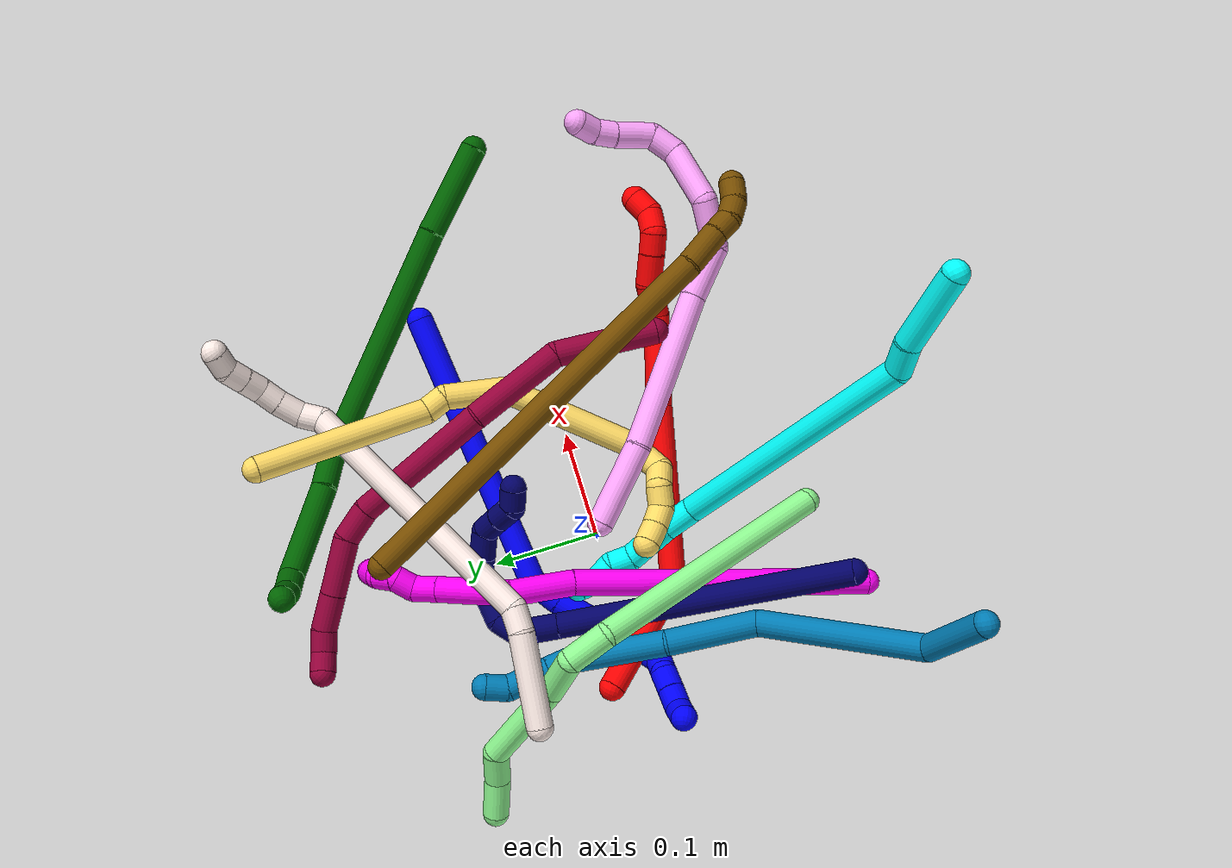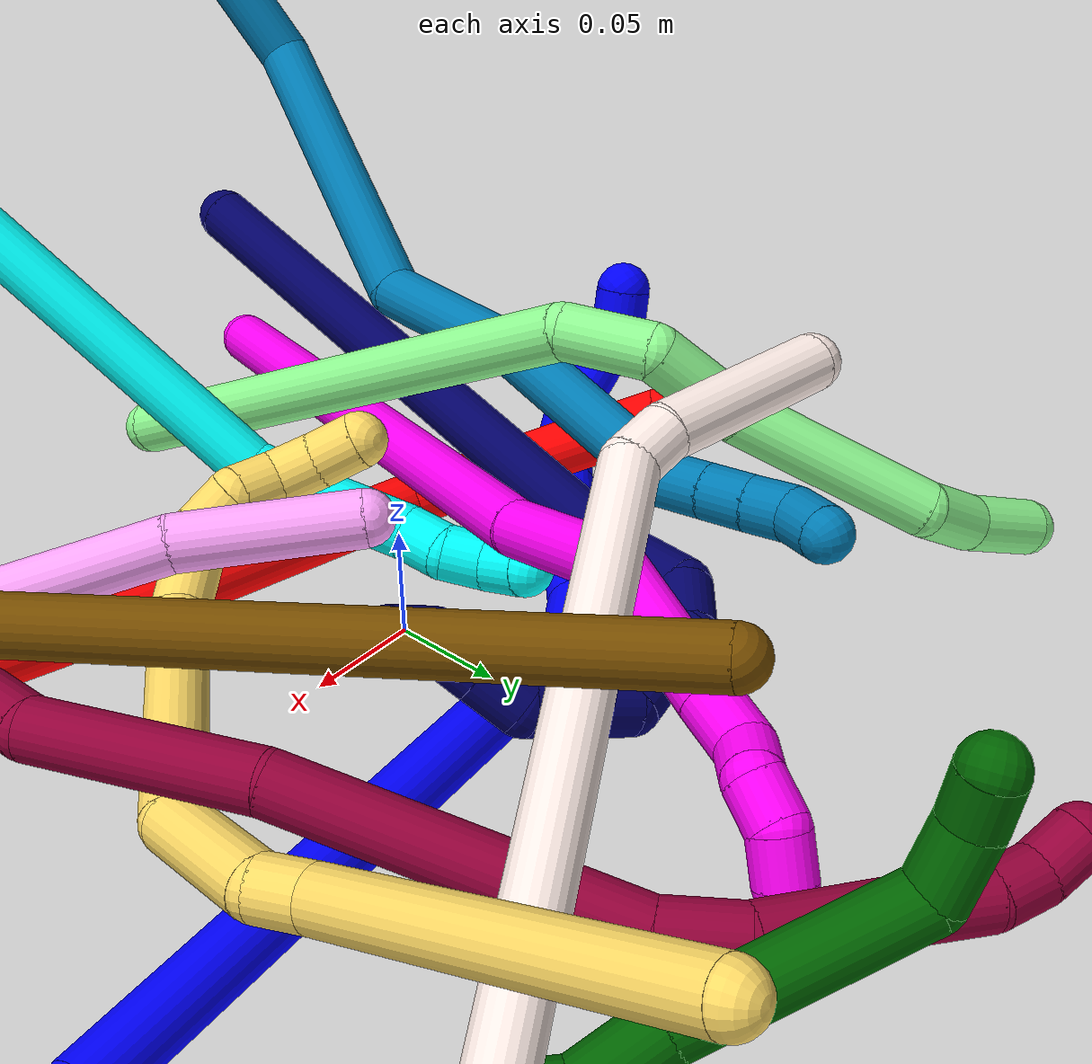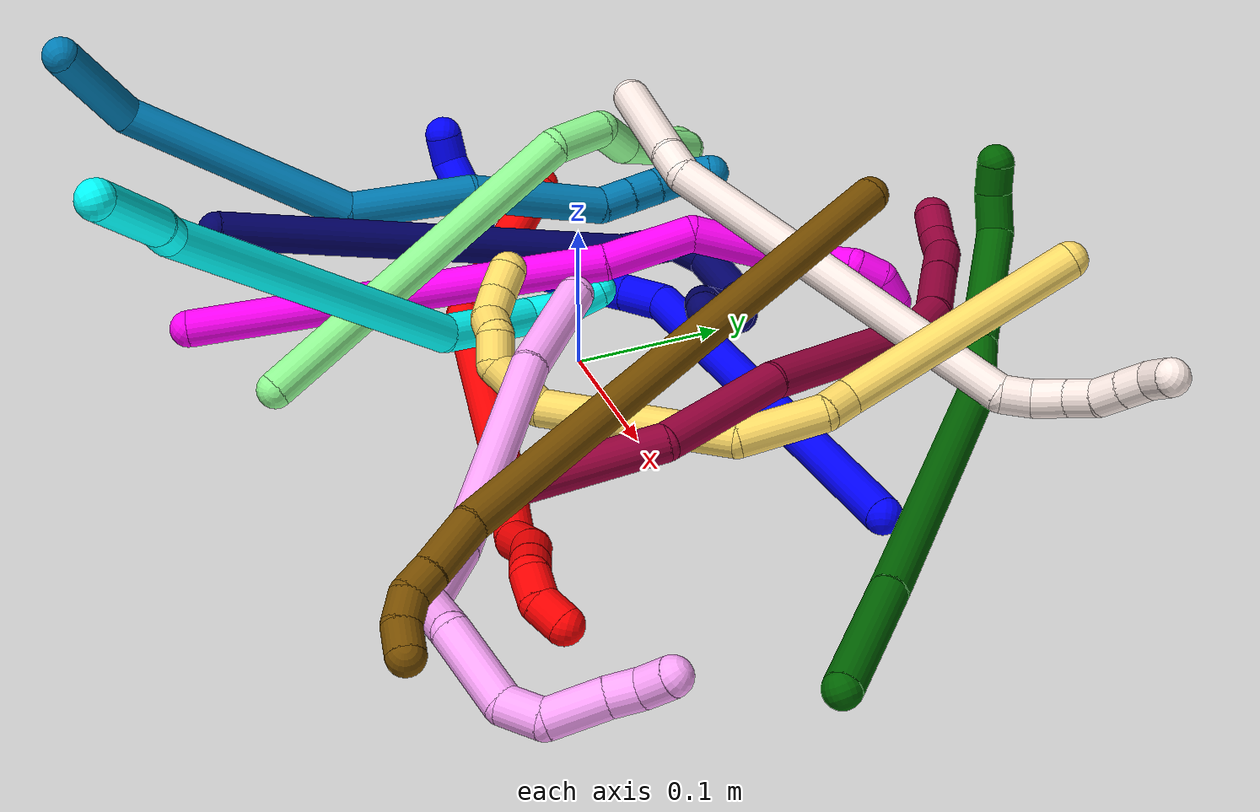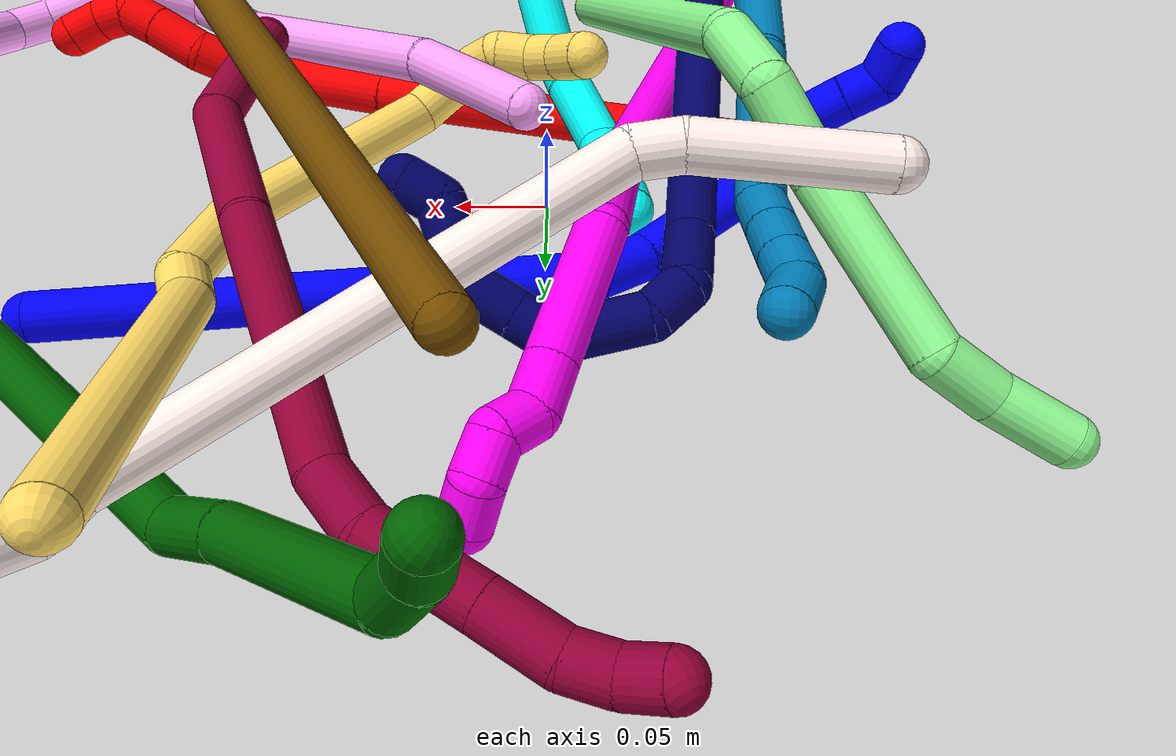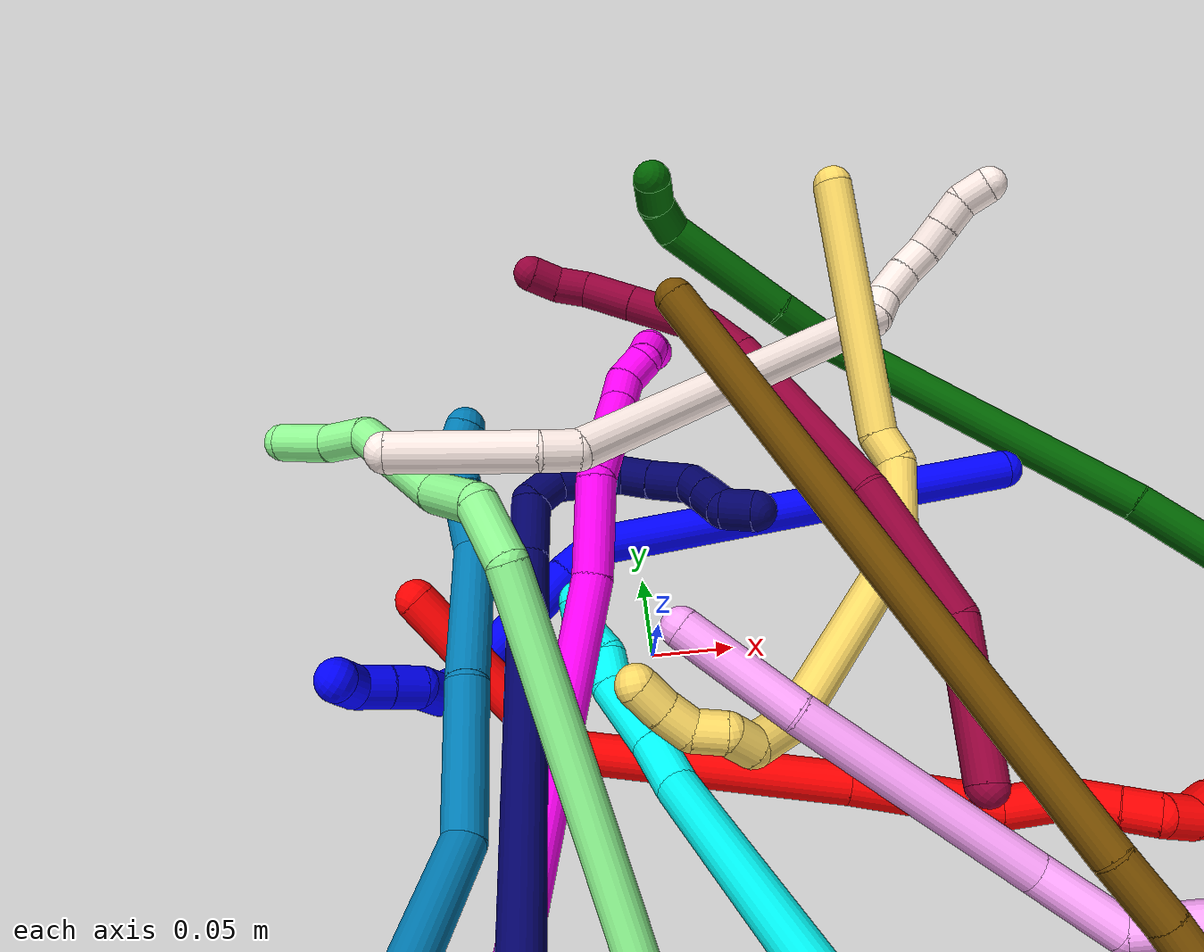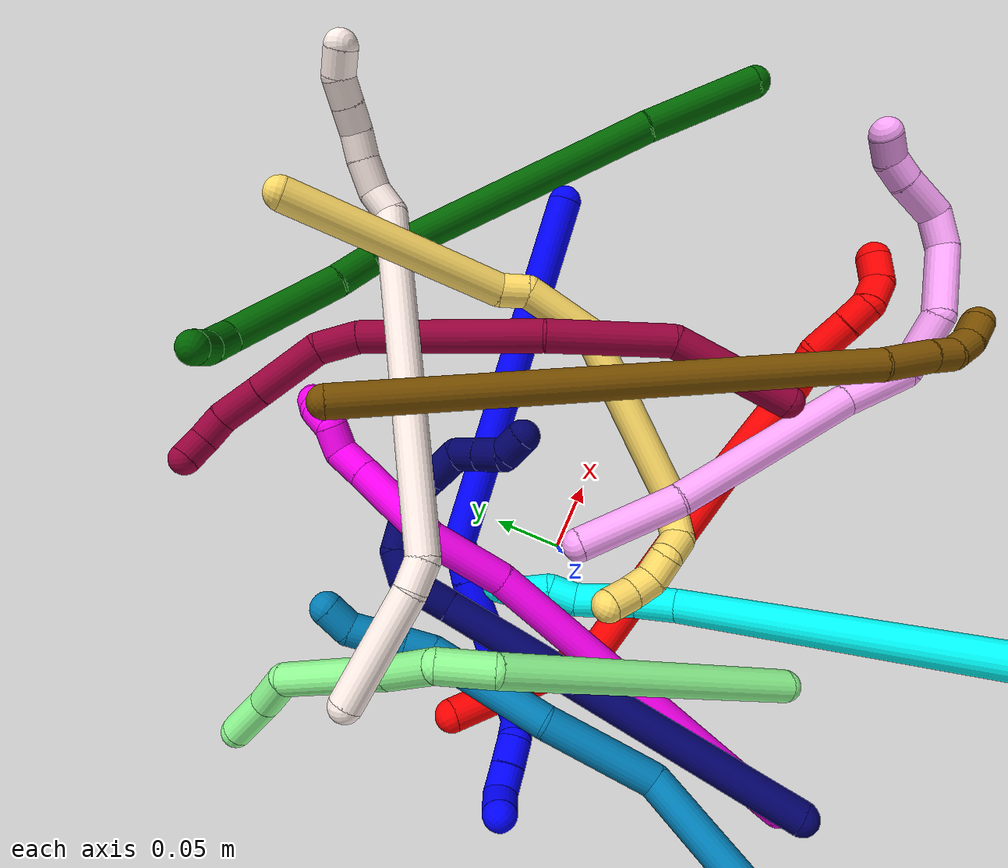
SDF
<sdf version="1.7">
 <world name="default">
  <plugin name="TubeGeneratorPlugin" filename="libtube_generator_plugin.so"/>
  <model name="photoneo_s_sensor">
   <static>1</static>
   <pose>0 0 2 1.57079 1.57079 3.14159</pose>
   <link name="link">
    <inertial><mass>0.1</mass></inertial>
    <sensor name="sensor" type="depth">
     <update_rate>30</update_rate>
     <camera>
      <horizontal_fov>1.22</horizontal_fov>
      <image><width>1920</width><height>1200</height><format>B8G8R8</format></image>
      <clip><near>0.1</near><far>4</far></clip>
      <depth_camera><output>points</output></depth_camera>
     </camera>
     <plugin name="camera_plugin" filename="libgazebo_ros_depth_camera.so">
      <baseline>0.2</baseline>
      <alwaysOn>1</alwaysOn>
      <updateRate>0.0</updateRate>
      <cameraName>camera_ir</cameraName>
      <imageTopicName>/camera/color/image_raw</imageTopicName>
      <cameraInfoTopicName>/camera/color/camera_info</cameraInfoTopicName>
      <depthImageTopicName>/camera/depth/image_raw</depthImageTopicName>
      <depthImageCameraInfoTopicName>/camera/depth/camera_info</depthImageCameraInfoTopicName>
      <pointCloudTopicName>/camera/depth/points</pointCloudTopicName>
      <frameName>fr_optical</frameName>
      <pointCloudCutoff>0.1</pointCloudCutoff>
      <pointCloudCutoffMax>2.0</pointCloudCutoffMax>
      <distortionK1>0</distortionK1>
      <distortionK2>0</distortionK2>
      <distortionK3>0</distortionK3>
      <distortionT1>0</distortionT1>
      <distortionT2>0</distortionT2>
      <CxPrime>0</CxPrime>
      <Cx>0</Cx>
      <Cy>0</Cy>
      <focalLength>0</focalLength>
      <hackBaseline>0</hackBaseline>
     </plugin>
    </sensor>
   </link>
  </model>
  <gravity>0 0 -9.8</gravity>
  <magnetic_field>6e-06 2.3e-05 -4.2e-05</magnetic_field>
  <atmosphere type="adiabatic"/>
  <physics name="default_physics" default="0" type="ode">
   <max_step_size>0.003</max_step_size>
   <real_time_factor>1</real_time_factor>
   <real_time_update_rate>1000</real_time_update_rate>
   <max_contacts>10000</max_contacts>
   <ode>
    <solver>
     <type>quick</type>
     <iters>100</iters>
     <sor>1.3</sor>
     <use_dynamic_moi_rescaling>0</use_dynamic_moi_rescaling>
    </solver>
    <constraints>
     <contact_max_correcting_vel>0</contact_max_correcting_vel>
     <contact_surface_layer>0.001</contact_surface_layer>
     <cfm>0</cfm>
     <erp>0.2</erp>
    </constraints>
   </ode>
  </physics>
  <scene><ambient>0.4 0.4 0.4 1</ambient><background>0.7 0.7 0.7 1</background><shadows>0</shadows></scene>
  <audio><device>default</device></audio>
  <spherical_coordinates>
   <surface_model>EARTH_WGS84</surface_model>
   <latitude_deg>0</latitude_deg>
   <longitude_deg>0</longitude_deg>
   <elevation>0</elevation>
   <heading_deg>0</heading_deg>
  </spherical_coordinates>
  <model name="bin">
   <static>1</static>
   <link name="bottom">
    <collision name="collision-bottom">
     <pose>0 0 -0.01 0 -0 0</pose>
     <geometry><box><size>0.8 0.6 0.02</size></box></geometry>
     <surface>
      <friction><ode><mu>100</mu><mu2>100</mu2></ode></friction>
      <contact><collide_bitmask>65535</collide_bitmask></contact>
     </surface>
    </collision>
   </link>
   <link name="west_wall">
    <collision name="collision-west_wall">
     <pose>-0.41 0 0.1 0 -0 0</pose>
     <geometry><box><size>0.02 0.6 0.2</size></box></geometry>
     <surface>
      <friction><ode><mu>100</mu><mu2>100</mu2></ode></friction>
      <contact><collide_bitmask>65535</collide_bitmask></contact>
     </surface>
    </collision>
   </link>
   <link name="east_wall">
    <collision name="collision-east_wall">
     <pose>0.41 0 0.1 0 -0 0</pose>
     <geometry><box><size>0.02 0.6 0.2</size></box></geometry>
     <surface>
      <friction><ode><mu>100</mu><mu2>100</mu2></ode></friction>
      <contact><collide_bitmask>65535</collide_bitmask></contact>
     </surface>
    </collision>
   </link>
   <link name="south_wall">
    <collision name="collision-south_wall">
     <pose>0 -0.31 0.1 0 -0 0</pose>
     <geometry><box><size>0.8 0.02 0.2</size></box></geometry>
     <surface>
      <friction><ode><mu>100</mu><mu2>100</mu2></ode></friction>
      <contact><collide_bitmask>65535</collide_bitmask></contact>
     </surface>
    </collision>
   </link>
   <link name="north_wall">
    <collision name="collision-north_wall">
     <pose>0 0.31 0.1 0 -0 0</pose>
     <geometry><box><size>0.8 0.02 0.2</size></box></geometry>
     <surface>
      <friction><ode><mu>100</mu><mu2>100</mu2></ode></friction>
      <contact><collide_bitmask>65535</collide_bitmask></contact>
     </surface>
    </collision>
   </link>
  </model>
  <model name="1">
   <static>0</static>
   <link name="1">
    <collision name="collision-cylinder-e_1_1_4">
     <pose>-0.015821 -0.090305 -0.100804 2.41108 -0.116371 -0.302324</pose>
     <geometry><cylinder><radius>0.0125</radius><length>0.27252</length></cylinder></geometry>
     <surface>
      <friction><ode><mu>1.16</mu><mu2>1.16</mu2><slip1>0</slip1><slip2>0</slip2></ode></friction>
      <contact><ode><kp>1e+06</kp><kd>1</kd><max_vel>0</max_vel><min_depth>0.001</min_depth></ode></contact>
     </surface>
    </collision>
    <visual name="visual-cylinder-e_1_1_4">
     <pose>-0.015821 -0.090305 -0.100804 2.41108 -0.116371 -0.302324</pose>
     <geometry><cylinder><radius>0.0125</radius><length>0.27252</length></cylinder></geometry>
     <material><ambient>0 0 1 1</ambient></material>
    </visual>
    <collision name="collision-cylinder-e_2_4_5">
     <pose>-0.03814 -0.193119 -0.207428 2.00622 -0.440153 -0.674749</pose>
     <geometry><cylinder><radius>0.0125</radius><length>0.030502</length></cylinder></geometry>
     <surface>
      <friction><ode><mu>1.16</mu><mu2>1.16</mu2><slip1>0</slip1><slip2>0</slip2></ode></friction>
      <contact><ode><kp>1e+06</kp><kd>1</kd><max_vel>0</max_vel><min_depth>0.001</min_depth></ode></contact>
     </surface>
    </collision>
    <visual name="visual-cylinder-e_2_4_5">
     <pose>-0.03814 -0.193119 -0.207428 2.00622 -0.440153 -0.674749</pose>
     <geometry><cylinder><radius>0.0125</radius><length>0.030502</length></cylinder></geometry>
     <material><ambient>0 0 1 1</ambient></material>
    </visual>
    <collision name="collision-cylinder-e_3_5_6">
     <pose>-0.055116 -0.219509 -0.218554 1.93597 -0.614188 -0.863529</pose>
     <geometry><cylinder><radius>0.0125</radius><length>0.036364</length></cylinder></geometry>
     <surface>
      <friction><ode><mu>1.16</mu><mu2>1.16</mu2><slip1>0</slip1><slip2>0</slip2></ode></friction>
      <contact><ode><kp>1e+06</kp><kd>1</kd><max_vel>0</max_vel><min_depth>0.001</min_depth></ode></contact>
     </surface>
    </collision>
    <visual name="visual-cylinder-e_3_5_6">
     <pose>-0.055116 -0.219509 -0.218554 1.93597 -0.614188 -0.863529</pose>
     <geometry><cylinder><radius>0.0125</radius><length>0.036364</length></cylinder></geometry>
     <material><ambient>0 0 1 1</ambient></material>
    </visual>
    <collision name="collision-cylinder-e_4_6_7">
     <pose>-0.082606 -0.255721 -0.233542 1.97986 -0.609972 -0.894381</pose>
     <geometry><cylinder><radius>0.0125</radius><length>0.059393</length></cylinder></geometry>
     <surface>
      <friction><ode><mu>1.16</mu><mu2>1.16</mu2><slip1>0</slip1><slip2>0</slip2></ode></friction>
      <contact><ode><kp>1e+06</kp><kd>1</kd><max_vel>0</max_vel><min_depth>0.001</min_depth></ode></contact>
     </surface>
    </collision>
    <visual name="visual-cylinder-e_4_6_7">
     <pose>-0.082606 -0.255721 -0.233542 1.97986 -0.609972 -0.894381</pose>
     <geometry><cylinder><radius>0.0125</radius><length>0.059393</length></cylinder></geometry>
     <material><ambient>0 0 1 1</ambient></material>
    </visual>
    <collision name="collision-cylinder-e_5_7_8">
     <pose>-0.108169 -0.279447 -0.248785 2.89607 -0.980271 -2.6871</pose>
     <geometry><cylinder><radius>0.0125</radius><length>0.020591</length></cylinder></geometry>
     <surface>
      <friction><ode><mu>1.16</mu><mu2>1.16</mu2><slip1>0</slip1><slip2>0</slip2></ode></friction>
      <contact><ode><kp>1e+06</kp><kd>1</kd><max_vel>0</max_vel><min_depth>0.001</min_depth></ode></contact>
     </surface>
    </collision>
    <visual name="visual-cylinder-e_5_7_8">
     <pose>-0.108169 -0.279447 -0.248785 2.89607 -0.980271 -2.6871</pose>
     <geometry><cylinder><radius>0.0125</radius><length>0.020591</length></cylinder></geometry>
     <material><ambient>0 0 1 1</ambient></material>
    </visual>
    <collision name="collision-cylinder-e_6_8_9">
     <pose>-0.1225 -0.278295 -0.262365 -2.83429 -0.601828 2.21584</pose>
     <geometry><cylinder><radius>0.0125</radius><length>0.020414</length></cylinder></geometry>
     <surface>
      <friction><ode><mu>1.16</mu><mu2>1.16</mu2><slip1>0</slip1><slip2>0</slip2></ode></friction>
      <contact><ode><kp>1e+06</kp><kd>1</kd><max_vel>0</max_vel><min_depth>0.001</min_depth></ode></contact>
     </surface>
    </collision>
    <visual name="visual-cylinder-e_6_8_9">
     <pose>-0.1225 -0.278295 -0.262365 -2.83429 -0.601828 2.21584</pose>
     <geometry><cylinder><radius>0.0125</radius><length>0.020414</length></cylinder></geometry>
     <material><ambient>0 0 1 1</ambient></material>
    </visual>
    <collision name="collision-cylinder-e_7_9_10">
     <pose>-0.132285 -0.278046 -0.279274 2.88887 -0.411444 -2.04789</pose>
     <geometry><cylinder><radius>0.0125</radius><length>0.020036</length></cylinder></geometry>
     <surface>
      <friction><ode><mu>1.16</mu><mu2>1.16</mu2><slip1>0</slip1><slip2>0</slip2></ode></friction>
      <contact><ode><kp>1e+06</kp><kd>1</kd><max_vel>0</max_vel><min_depth>0.001</min_depth></ode></contact>
     </surface>
    </collision>
    <visual name="visual-cylinder-e_7_9_10">
     <pose>-0.132285 -0.278046 -0.279274 2.88887 -0.411444 -2.04789</pose>
     <geometry><cylinder><radius>0.0125</radius><length>0.020036</length></cylinder></geometry>
     <material><ambient>0 0 1 1</ambient></material>
    </visual>
    <collision name="collision-cylinder-e_8_10_11">
     <pose>-0.139979 -0.28312 -0.297092 2.83995 -0.375674 -1.79266</pose>
     <geometry><cylinder><radius>0.0125</radius><length>0.020102</length></cylinder></geometry>
     <surface>
      <friction><ode><mu>1.16</mu><mu2>1.16</mu2><slip1>0</slip1><slip2>0</slip2></ode></friction>
      <contact><ode><kp>1e+06</kp><kd>1</kd><max_vel>0</max_vel><min_depth>0.001</min_depth></ode></contact>
     </surface>
    </collision>
    <visual name="visual-cylinder-e_8_10_11">
     <pose>-0.139979 -0.28312 -0.297092 2.83995 -0.375674 -1.79266</pose>
     <geometry><cylinder><radius>0.0125</radius><length>0.020102</length></cylinder></geometry>
     <material><ambient>0 0 1 1</ambient></material>
    </visual>
    <collision name="collision-cylinder-e_9_11_2">
     <pose>-0.15022 -0.282266 -0.312703 -2.64381 -0.71121 1.94131</pose>
     <geometry><cylinder><radius>0.0125</radius><length>0.020079</length></cylinder></geometry>
     <surface>
      <friction><ode><mu>1.16</mu><mu2>1.16</mu2><slip1>0</slip1><slip2>0</slip2></ode></friction>
      <contact><ode><kp>1e+06</kp><kd>1</kd><max_vel>0</max_vel><min_depth>0.001</min_depth></ode></contact>
     </surface>
    </collision>
    <visual name="visual-cylinder-e_9_11_2">
     <pose>-0.15022 -0.282266 -0.312703 -2.64381 -0.71121 1.94131</pose>
     <geometry><cylinder><radius>0.0125</radius><length>0.020079</length></cylinder></geometry>
     <material><ambient>0 0 1 1</ambient></material>
    </visual>
    <collision name="collision-sphere-2">
     <pose>-0.156773 -0.278635 -0.319385 0 -0 0</pose>
     <geometry><sphere><radius>0.0125</radius></sphere></geometry>
     <surface>
      <friction><ode><mu>1.16</mu><mu2>1.16</mu2><slip1>0</slip1><slip2>0</slip2></ode></friction>
      <contact><ode><kp>1e+06</kp><kd>1</kd><max_vel>0</max_vel><min_depth>0.001</min_depth></ode></contact>
     </surface>
    </collision>
    <visual name="visual-sphere-2">
     <pose>-0.156773 -0.278635 -0.319385 0 -0 0</pose>
     <geometry><sphere><radius>0.0125</radius></sphere></geometry>
     <material><ambient>0 0 1 1</ambient></material>
    </visual>
    <collision name="collision-sphere-11">
     <pose>-0.143667 -0.285898 -0.30602 0 -0 0</pose>
     <geometry><sphere><radius>0.0125</radius></sphere></geometry>
     <surface>
      <friction><ode><mu>1.16</mu><mu2>1.16</mu2><slip1>0</slip1><slip2>0</slip2></ode></friction>
      <contact><ode><kp>1e+06</kp><kd>1</kd><max_vel>0</max_vel><min_depth>0.001</min_depth></ode></contact>
     </surface>
    </collision>
    <visual name="visual-sphere-11">
     <pose>-0.143667 -0.285898 -0.30602 0 -0 0</pose>
     <geometry><sphere><radius>0.0125</radius></sphere></geometry>
     <material><ambient>0 0 1 1</ambient></material>
    </visual>
    <collision name="collision-sphere-10">
     <pose>-0.136292 -0.280342 -0.288164 0 -0 0</pose>
     <geometry><sphere><radius>0.0125</radius></sphere></geometry>
     <surface>
      <friction><ode><mu>1.16</mu><mu2>1.16</mu2><slip1>0</slip1><slip2>0</slip2></ode></friction>
      <contact><ode><kp>1e+06</kp><kd>1</kd><max_vel>0</max_vel><min_depth>0.001</min_depth></ode></contact>
     </surface>
    </collision>
    <visual name="visual-sphere-10">
     <pose>-0.136292 -0.280342 -0.288164 0 -0 0</pose>
     <geometry><sphere><radius>0.0125</radius></sphere></geometry>
     <material><ambient>0 0 1 1</ambient></material>
    </visual>
    <collision name="collision-sphere-9">
     <pose>-0.128279 -0.27575 -0.270384 0 -0 0</pose>
     <geometry><sphere><radius>0.0125</radius></sphere></geometry>
     <surface>
      <friction><ode><mu>1.16</mu><mu2>1.16</mu2><slip1>0</slip1><slip2>0</slip2></ode></friction>
      <contact><ode><kp>1e+06</kp><kd>1</kd><max_vel>0</max_vel><min_depth>0.001</min_depth></ode></contact>
     </surface>
    </collision>
    <visual name="visual-sphere-9">
     <pose>-0.128279 -0.27575 -0.270384 0 -0 0</pose>
     <geometry><sphere><radius>0.0125</radius></sphere></geometry>
     <material><ambient>0 0 1 1</ambient></material>
    </visual>
    <collision name="collision-sphere-4">
     <pose>-0.031642 -0.180609 -0.201608 0 -0 0</pose>
     <geometry><sphere><radius>0.0125</radius></sphere></geometry>
     <surface>
      <friction><ode><mu>1.16</mu><mu2>1.16</mu2><slip1>0</slip1><slip2>0</slip2></ode></friction>
      <contact><ode><kp>1e+06</kp><kd>1</kd><max_vel>0</max_vel><min_depth>0.001</min_depth></ode></contact>
     </surface>
    </collision>
    <visual name="visual-sphere-4">
     <pose>-0.031642 -0.180609 -0.201608 0 -0 0</pose>
     <geometry><sphere><radius>0.0125</radius></sphere></geometry>
     <material><ambient>0 0 1 1</ambient></material>
    </visual>
    <collision name="collision-sphere-1">
     <geometry><sphere><radius>0.0125</radius></sphere></geometry>
     <surface>
      <friction><ode><mu>1.16</mu><mu2>1.16</mu2><slip1>0</slip1><slip2>0</slip2></ode></friction>
      <contact><ode><kp>1e+06</kp><kd>1</kd><max_vel>0</max_vel><min_depth>0.001</min_depth></ode></contact>
     </surface>
    </collision>
    <visual name="visual-sphere-1">
     <geometry><sphere><radius>0.0125</radius></sphere></geometry>
     <material><ambient>0 0 1 1</ambient></material>
    </visual>
    <collision name="collision-sphere-8">
     <pose>-0.116722 -0.28084 -0.254345 0 -0 0</pose>
     <geometry><sphere><radius>0.0125</radius></sphere></geometry>
     <surface>
      <friction><ode><mu>1.16</mu><mu2>1.16</mu2><slip1>0</slip1><slip2>0</slip2></ode></friction>
      <contact><ode><kp>1e+06</kp><kd>1</kd><max_vel>0</max_vel><min_depth>0.001</min_depth></ode></contact>
     </surface>
    </collision>
    <visual name="visual-sphere-8">
     <pose>-0.116722 -0.28084 -0.254345 0 -0 0</pose>
     <geometry><sphere><radius>0.0125</radius></sphere></geometry>
     <material><ambient>0 0 1 1</ambient></material>
    </visual>
    <collision name="collision-sphere-5">
     <pose>-0.044638 -0.205629 -0.213248 0 -0 0</pose>
     <geometry><sphere><radius>0.0125</radius></sphere></geometry>
     <surface>
      <friction><ode><mu>1.16</mu><mu2>1.16</mu2><slip1>0</slip1><slip2>0</slip2></ode></friction>
      <contact><ode><kp>1e+06</kp><kd>1</kd><max_vel>0</max_vel><min_depth>0.001</min_depth></ode></contact>
     </surface>
    </collision>
    <visual name="visual-sphere-5">
     <pose>-0.044638 -0.205629 -0.213248 0 -0 0</pose>
     <geometry><sphere><radius>0.0125</radius></sphere></geometry>
     <material><ambient>0 0 1 1</ambient></material>
    </visual>
    <collision name="collision-sphere-6">
     <pose>-0.065594 -0.233388 -0.22386 0 -0 0</pose>
     <geometry><sphere><radius>0.0125</radius></sphere></geometry>
     <surface>
      <friction><ode><mu>1.16</mu><mu2>1.16</mu2><slip1>0</slip1><slip2>0</slip2></ode></friction>
      <contact><ode><kp>1e+06</kp><kd>1</kd><max_vel>0</max_vel><min_depth>0.001</min_depth></ode></contact>
     </surface>
    </collision>
    <visual name="visual-sphere-6">
     <pose>-0.065594 -0.233388 -0.22386 0 -0 0</pose>
     <geometry><sphere><radius>0.0125</radius></sphere></geometry>
     <material><ambient>0 0 1 1</ambient></material>
    </visual>
    <collision name="collision-sphere-7">
     <pose>-0.099617 -0.278054 -0.243224 0 -0 0</pose>
     <geometry><sphere><radius>0.0125</radius></sphere></geometry>
     <surface>
      <friction><ode><mu>1.16</mu><mu2>1.16</mu2><slip1>0</slip1><slip2>0</slip2></ode></friction>
      <contact><ode><kp>1e+06</kp><kd>1</kd><max_vel>0</max_vel><min_depth>0.001</min_depth></ode></contact>
     </surface>
    </collision>
    <visual name="visual-sphere-7">
     <pose>-0.099617 -0.278054 -0.243224 0 -0 0</pose>
     <geometry><sphere><radius>0.0125</radius></sphere></geometry>
     <material><ambient>0 0 1 1</ambient></material>
    </visual>
    <inertial>
     <pose>-0.051188 -0.164071 -0.167883 0 -0 0</pose>
     <mass>0.5</mass>
     <inertia>
      <ixx>0.001089</ixx>
      <ixy>0</ixy>
      <ixz>0</ixz>
      <iyy>-0.001702</iyy>
      <iyz>0</iyz>
      <izz>0.001339</izz>
     </inertia>
    </inertial>
   </link>
   <pose>0.246098 0.101689 0.011497 2.22803 0.640888 1.54403</pose>
  </model>
  <model name="2">
   <static>0</static>
   <link name="2">
    <collision name="collision-cylinder-e_1_1_4">
     <pose>0.050982 -0.031124 0.00722 1.34285 1.01097 0.828609</pose>
     <geometry><cylinder><radius>0.0125</radius><length>0.120334</length></cylinder></geometry>
     <surface>
      <friction><ode><mu>1.16</mu><mu2>1.16</mu2><slip1>0</slip1><slip2>0</slip2></ode></friction>
      <contact><ode><kp>1e+06</kp><kd>1</kd><max_vel>0</max_vel><min_depth>0.001</min_depth></ode></contact>
     </surface>
    </collision>
    <visual name="visual-cylinder-e_1_1_4">
     <pose>0.050982 -0.031124 0.00722 1.34285 1.01097 0.828609</pose>
     <geometry><cylinder><radius>0.0125</radius><length>0.120334</length></cylinder></geometry>
     <material><ambient>1 0 0 1</ambient></material>
    </visual>
    <collision name="collision-cylinder-e_2_4_5">
     <pose>0.177278 -0.070974 -0.022853 2.91176 1.10034 2.76957</pose>
     <geometry><cylinder><radius>0.0125</radius><length>0.168986</length></cylinder></geometry>
     <surface>
      <friction><ode><mu>1.16</mu><mu2>1.16</mu2><slip1>0</slip1><slip2>0</slip2></ode></friction>
      <contact><ode><kp>1e+06</kp><kd>1</kd><max_vel>0</max_vel><min_depth>0.001</min_depth></ode></contact>
     </surface>
    </collision>
    <visual name="visual-cylinder-e_2_4_5">
     <pose>0.177278 -0.070974 -0.022853 2.91176 1.10034 2.76957</pose>
     <geometry><cylinder><radius>0.0125</radius><length>0.168986</length></cylinder></geometry>
     <material><ambient>1 0 0 1</ambient></material>
    </visual>
    <collision name="collision-cylinder-e_3_5_6">
     <pose>0.292423 -0.084312 -0.077571 2.88277 1.14582 2.74345</pose>
     <geometry><cylinder><radius>0.0125</radius><length>0.087441</length></cylinder></geometry>
     <surface>
      <friction><ode><mu>1.16</mu><mu2>1.16</mu2><slip1>0</slip1><slip2>0</slip2></ode></friction>
      <contact><ode><kp>1e+06</kp><kd>1</kd><max_vel>0</max_vel><min_depth>0.001</min_depth></ode></contact>
     </surface>
    </collision>
    <visual name="visual-cylinder-e_3_5_6">
     <pose>0.292423 -0.084312 -0.077571 2.88277 1.14582 2.74345</pose>
     <geometry><cylinder><radius>0.0125</radius><length>0.087441</length></cylinder></geometry>
     <material><ambient>1 0 0 1</ambient></material>
    </visual>
    <collision name="collision-cylinder-e_4_6_7">
     <pose>0.345168 -0.082914 -0.103205 -2.50947 0.903467 -1.95547</pose>
     <geometry><cylinder><radius>0.0125</radius><length>0.03288</length></cylinder></geometry>
     <surface>
      <friction><ode><mu>1.16</mu><mu2>1.16</mu2><slip1>0</slip1><slip2>0</slip2></ode></friction>
      <contact><ode><kp>1e+06</kp><kd>1</kd><max_vel>0</max_vel><min_depth>0.001</min_depth></ode></contact>
     </surface>
    </collision>
    <visual name="visual-cylinder-e_4_6_7">
     <pose>0.345168 -0.082914 -0.103205 -2.50947 0.903467 -1.95547</pose>
     <geometry><cylinder><radius>0.0125</radius><length>0.03288</length></cylinder></geometry>
     <material><ambient>1 0 0 1</ambient></material>
    </visual>
    <collision name="collision-cylinder-e_5_7_8">
     <pose>0.372043 -0.073567 -0.114717 -2.3513 1.24643 -2.09002</pose>
     <geometry><cylinder><radius>0.0125</radius><length>0.029459</length></cylinder></geometry>
     <surface>
      <friction><ode><mu>1.16</mu><mu2>1.16</mu2><slip1>0</slip1><slip2>0</slip2></ode></friction>
      <contact><ode><kp>1e+06</kp><kd>1</kd><max_vel>0</max_vel><min_depth>0.001</min_depth></ode></contact>
     </surface>
    </collision>
    <visual name="visual-cylinder-e_5_7_8">
     <pose>0.372043 -0.073567 -0.114717 -2.3513 1.24643 -2.09002</pose>
     <geometry><cylinder><radius>0.0125</radius><length>0.029459</length></cylinder></geometry>
     <material><ambient>1 0 0 1</ambient></material>
    </visual>
    <collision name="collision-cylinder-e_6_8_9">
     <pose>0.395536 -0.06852 -0.120577 -2.55162 1.25857 -2.35082</pose>
     <geometry><cylinder><radius>0.0125</radius><length>0.020033</length></cylinder></geometry>
     <surface>
      <friction><ode><mu>1.16</mu><mu2>1.16</mu2><slip1>0</slip1><slip2>0</slip2></ode></friction>
      <contact><ode><kp>1e+06</kp><kd>1</kd><max_vel>0</max_vel><min_depth>0.001</min_depth></ode></contact>
     </surface>
    </collision>
    <visual name="visual-cylinder-e_6_8_9">
     <pose>0.395536 -0.06852 -0.120577 -2.55162 1.25857 -2.35082</pose>
     <geometry><cylinder><radius>0.0125</radius><length>0.020033</length></cylinder></geometry>
     <material><ambient>1 0 0 1</ambient></material>
    </visual>
    <collision name="collision-cylinder-e_7_9_10">
     <pose>0.412667 -0.070769 -0.128764 2.52846 0.83465 1.90152</pose>
     <geometry><cylinder><radius>0.0125</radius><length>0.020507</length></cylinder></geometry>
     <surface>
      <friction><ode><mu>1.16</mu><mu2>1.16</mu2><slip1>0</slip1><slip2>0</slip2></ode></friction>
      <contact><ode><kp>1e+06</kp><kd>1</kd><max_vel>0</max_vel><min_depth>0.001</min_depth></ode></contact>
     </surface>
    </collision>
    <visual name="visual-cylinder-e_7_9_10">
     <pose>0.412667 -0.070769 -0.128764 2.52846 0.83465 1.90152</pose>
     <geometry><cylinder><radius>0.0125</radius><length>0.020507</length></cylinder></geometry>
     <material><ambient>1 0 0 1</ambient></material>
    </visual>
    <collision name="collision-cylinder-e_8_10_2">
     <pose>0.424015 -0.077462 -0.143457 2.84892 0.377224 1.82655</pose>
     <geometry><cylinder><radius>0.0125</radius><length>0.020361</length></cylinder></geometry>
     <surface>
      <friction><ode><mu>1.16</mu><mu2>1.16</mu2><slip1>0</slip1><slip2>0</slip2></ode></friction>
      <contact><ode><kp>1e+06</kp><kd>1</kd><max_vel>0</max_vel><min_depth>0.001</min_depth></ode></contact>
     </surface>
    </collision>
    <visual name="visual-cylinder-e_8_10_2">
     <pose>0.424015 -0.077462 -0.143457 2.84892 0.377224 1.82655</pose>
     <geometry><cylinder><radius>0.0125</radius><length>0.020361</length></cylinder></geometry>
     <material><ambient>1 0 0 1</ambient></material>
    </visual>
    <collision name="collision-sphere-2">
     <pose>0.427765 -0.080192 -0.152519 0 -0 0</pose>
     <geometry><sphere><radius>0.0125</radius></sphere></geometry>
     <surface>
      <friction><ode><mu>1.16</mu><mu2>1.16</mu2><slip1>0</slip1><slip2>0</slip2></ode></friction>
      <contact><ode><kp>1e+06</kp><kd>1</kd><max_vel>0</max_vel><min_depth>0.001</min_depth></ode></contact>
     </surface>
    </collision>
    <visual name="visual-sphere-2">
     <pose>0.427765 -0.080192 -0.152519 0 -0 0</pose>
     <geometry><sphere><radius>0.0125</radius></sphere></geometry>
     <material><ambient>1 0 0 1</ambient></material>
    </visual>
    <collision name="collision-sphere-10">
     <pose>0.420265 -0.074731 -0.134395 0 -0 0</pose>
     <geometry><sphere><radius>0.0125</radius></sphere></geometry>
     <surface>
      <friction><ode><mu>1.16</mu><mu2>1.16</mu2><slip1>0</slip1><slip2>0</slip2></ode></friction>
      <contact><ode><kp>1e+06</kp><kd>1</kd><max_vel>0</max_vel><min_depth>0.001</min_depth></ode></contact>
     </surface>
    </collision>
    <visual name="visual-sphere-10">
     <pose>0.420265 -0.074731 -0.134395 0 -0 0</pose>
     <geometry><sphere><radius>0.0125</radius></sphere></geometry>
     <material><ambient>1 0 0 1</ambient></material>
    </visual>
    <collision name="collision-sphere-9">
     <pose>0.405069 -0.066808 -0.123134 0 -0 0</pose>
     <geometry><sphere><radius>0.0125</radius></sphere></geometry>
     <surface>
      <friction><ode><mu>1.16</mu><mu2>1.16</mu2><slip1>0</slip1><slip2>0</slip2></ode></friction>
      <contact><ode><kp>1e+06</kp><kd>1</kd><max_vel>0</max_vel><min_depth>0.001</min_depth></ode></contact>
     </surface>
    </collision>
    <visual name="visual-sphere-9">
     <pose>0.405069 -0.066808 -0.123134 0 -0 0</pose>
     <geometry><sphere><radius>0.0125</radius></sphere></geometry>
     <material><ambient>1 0 0 1</ambient></material>
    </visual>
    <collision name="collision-sphere-4">
     <pose>0.101965 -0.062249 0.01444 0 -0 0</pose>
     <geometry><sphere><radius>0.0125</radius></sphere></geometry>
     <surface>
      <friction><ode><mu>1.16</mu><mu2>1.16</mu2><slip1>0</slip1><slip2>0</slip2></ode></friction>
      <contact><ode><kp>1e+06</kp><kd>1</kd><max_vel>0</max_vel><min_depth>0.001</min_depth></ode></contact>
     </surface>
    </collision>
    <visual name="visual-sphere-4">
     <pose>0.101965 -0.062249 0.01444 0 -0 0</pose>
     <geometry><sphere><radius>0.0125</radius></sphere></geometry>
     <material><ambient>1 0 0 1</ambient></material>
    </visual>
    <collision name="collision-sphere-1">
     <geometry><sphere><radius>0.0125</radius></sphere></geometry>
     <surface>
      <friction><ode><mu>1.16</mu><mu2>1.16</mu2><slip1>0</slip1><slip2>0</slip2></ode></friction>
      <contact><ode><kp>1e+06</kp><kd>1</kd><max_vel>0</max_vel><min_depth>0.001</min_depth></ode></contact>
     </surface>
    </collision>
    <visual name="visual-sphere-1">
     <geometry><sphere><radius>0.0125</radius></sphere></geometry>
     <material><ambient>1 0 0 1</ambient></material>
    </visual>
    <collision name="collision-sphere-8">
     <pose>0.386004 -0.070231 -0.11802 0 -0 0</pose>
     <geometry><sphere><radius>0.0125</radius></sphere></geometry>
     <surface>
      <friction><ode><mu>1.16</mu><mu2>1.16</mu2><slip1>0</slip1><slip2>0</slip2></ode></friction>
      <contact><ode><kp>1e+06</kp><kd>1</kd><max_vel>0</max_vel><min_depth>0.001</min_depth></ode></contact>
     </surface>
    </collision>
    <visual name="visual-sphere-8">
     <pose>0.386004 -0.070231 -0.11802 0 -0 0</pose>
     <geometry><sphere><radius>0.0125</radius></sphere></geometry>
     <material><ambient>1 0 0 1</ambient></material>
    </visual>
    <collision name="collision-sphere-5">
     <pose>0.252592 -0.079699 -0.060145 0 -0 0</pose>
     <geometry><sphere><radius>0.0125</radius></sphere></geometry>
     <surface>
      <friction><ode><mu>1.16</mu><mu2>1.16</mu2><slip1>0</slip1><slip2>0</slip2></ode></friction>
      <contact><ode><kp>1e+06</kp><kd>1</kd><max_vel>0</max_vel><min_depth>0.001</min_depth></ode></contact>
     </surface>
    </collision>
    <visual name="visual-sphere-5">
     <pose>0.252592 -0.079699 -0.060145 0 -0 0</pose>
     <geometry><sphere><radius>0.0125</radius></sphere></geometry>
     <material><ambient>1 0 0 1</ambient></material>
    </visual>
    <collision name="collision-sphere-6">
     <pose>0.332255 -0.088926 -0.094997 0 -0 0</pose>
     <geometry><sphere><radius>0.0125</radius></sphere></geometry>
     <surface>
      <friction><ode><mu>1.16</mu><mu2>1.16</mu2><slip1>0</slip1><slip2>0</slip2></ode></friction>
      <contact><ode><kp>1e+06</kp><kd>1</kd><max_vel>0</max_vel><min_depth>0.001</min_depth></ode></contact>
     </surface>
    </collision>
    <visual name="visual-sphere-6">
     <pose>0.332255 -0.088926 -0.094997 0 -0 0</pose>
     <geometry><sphere><radius>0.0125</radius></sphere></geometry>
     <material><ambient>1 0 0 1</ambient></material>
    </visual>
    <collision name="collision-sphere-7">
     <pose>0.358081 -0.076903 -0.111414 0 -0 0</pose>
     <geometry><sphere><radius>0.0125</radius></sphere></geometry>
     <surface>
      <friction><ode><mu>1.16</mu><mu2>1.16</mu2><slip1>0</slip1><slip2>0</slip2></ode></friction>
      <contact><ode><kp>1e+06</kp><kd>1</kd><max_vel>0</max_vel><min_depth>0.001</min_depth></ode></contact>
     </surface>
    </collision>
    <visual name="visual-sphere-7">
     <pose>0.358081 -0.076903 -0.111414 0 -0 0</pose>
     <geometry><sphere><radius>0.0125</radius></sphere></geometry>
     <material><ambient>1 0 0 1</ambient></material>
    </visual>
    <inertial>
     <pose>0.217982 -0.064811 -0.049051 0 -0 0</pose>
     <mass>0.5</mass>
     <inertia>
      <ixx>2.4e-05</ixx>
      <ixy>0</ixy>
      <ixz>0</ixz>
      <iyy>0.00071</iyy>
      <iyz>0</iyz>
      <izz>-0.000442</izz>
     </inertia>
    </inertial>
   </link>
   <pose>-0.139023 0.02738 0.055103 1.46531 -0.162454 -0.660799</pose>
  </model>
  <model name="3">
   <static>0</static>
   <link name="3">
    <collision name="collision-cylinder-e_1_1_4">
     <pose>-0.009024 0.029977 -0.022541 -2.21555 -0.236115 0.466527</pose>
     <geometry><cylinder><radius>0.0125</radius><length>0.077154</length></cylinder></geometry>
     <surface>
      <friction><ode><mu>1.16</mu><mu2>1.16</mu2><slip1>0</slip1><slip2>0</slip2></ode></friction>
      <contact><ode><kp>1e+06</kp><kd>1</kd><max_vel>0</max_vel><min_depth>0.001</min_depth></ode></contact>
     </surface>
    </collision>
    <visual name="visual-cylinder-e_1_1_4">
     <pose>-0.009024 0.029977 -0.022541 -2.21555 -0.236115 0.466527</pose>
     <geometry><cylinder><radius>0.0125</radius><length>0.077154</length></cylinder></geometry>
     <material><ambient>0.003922 1 0.996078 1</ambient></material>
    </visual>
    <collision name="collision-cylinder-e_2_4_5">
     <pose>-0.020684 0.073328 -0.051257 -2.00331 -0.177026 0.275671</pose>
     <geometry><cylinder><radius>0.0125</radius><length>0.029928</length></cylinder></geometry>
     <surface>
      <friction><ode><mu>1.16</mu><mu2>1.16</mu2><slip1>0</slip1><slip2>0</slip2></ode></friction>
      <contact><ode><kp>1e+06</kp><kd>1</kd><max_vel>0</max_vel><min_depth>0.001</min_depth></ode></contact>
     </surface>
    </collision>
    <visual name="visual-cylinder-e_2_4_5">
     <pose>-0.020684 0.073328 -0.051257 -2.00331 -0.177026 0.275671</pose>
     <geometry><cylinder><radius>0.0125</radius><length>0.029928</length></cylinder></geometry>
     <material><ambient>0.003922 1 0.996078 1</ambient></material>
    </visual>
    <collision name="collision-cylinder-e_3_5_6">
     <pose>-0.074575 0.154501 -0.153509 -2.52707 -0.411057 1.16256</pose>
     <geometry><cylinder><radius>0.0125</radius><length>0.256552</length></cylinder></geometry>
     <surface>
      <friction><ode><mu>1.16</mu><mu2>1.16</mu2><slip1>0</slip1><slip2>0</slip2></ode></friction>
      <contact><ode><kp>1e+06</kp><kd>1</kd><max_vel>0</max_vel><min_depth>0.001</min_depth></ode></contact>
     </surface>
    </collision>
    <visual name="visual-cylinder-e_3_5_6">
     <pose>-0.074575 0.154501 -0.153509 -2.52707 -0.411057 1.16256</pose>
     <geometry><cylinder><radius>0.0125</radius><length>0.256552</length></cylinder></geometry>
     <material><ambient>0.003922 1 0.996078 1</ambient></material>
    </visual>
    <collision name="collision-cylinder-e_4_6_7">
     <pose>-0.127441 0.227473 -0.264058 -2.79826 -0.104329 0.585034</pose>
     <geometry><cylinder><radius>0.0125</radius><length>0.030905</length></cylinder></geometry>
     <surface>
      <friction><ode><mu>1.16</mu><mu2>1.16</mu2><slip1>0</slip1><slip2>0</slip2></ode></friction>
      <contact><ode><kp>1e+06</kp><kd>1</kd><max_vel>0</max_vel><min_depth>0.001</min_depth></ode></contact>
     </surface>
    </collision>
    <visual name="visual-cylinder-e_4_6_7">
     <pose>-0.127441 0.227473 -0.264058 -2.79826 -0.104329 0.585034</pose>
     <geometry><cylinder><radius>0.0125</radius><length>0.030905</length></cylinder></geometry>
     <material><ambient>0.003922 1 0.996078 1</ambient></material>
    </visual>
    <collision name="collision-cylinder-e_5_7_8">
     <pose>-0.130456 0.241775 -0.298811 -2.71868 -0.063111 0.292003</pose>
     <geometry><cylinder><radius>0.0125</radius><length>0.044572</length></cylinder></geometry>
     <surface>
      <friction><ode><mu>1.16</mu><mu2>1.16</mu2><slip1>0</slip1><slip2>0</slip2></ode></friction>
      <contact><ode><kp>1e+06</kp><kd>1</kd><max_vel>0</max_vel><min_depth>0.001</min_depth></ode></contact>
     </surface>
    </collision>
    <visual name="visual-cylinder-e_5_7_8">
     <pose>-0.130456 0.241775 -0.298811 -2.71868 -0.063111 0.292003</pose>
     <geometry><cylinder><radius>0.0125</radius><length>0.044572</length></cylinder></geometry>
     <material><ambient>0.003922 1 0.996078 1</ambient></material>
    </visual>
    <collision name="collision-cylinder-e_6_8_9">
     <pose>-0.133356 0.251266 -0.329406 -3.10642 -0.143837 2.66273</pose>
     <geometry><cylinder><radius>0.0125</radius><length>0.020854</length></cylinder></geometry>
     <surface>
      <friction><ode><mu>1.16</mu><mu2>1.16</mu2><slip1>0</slip1><slip2>0</slip2></ode></friction>
      <contact><ode><kp>1e+06</kp><kd>1</kd><max_vel>0</max_vel><min_depth>0.001</min_depth></ode></contact>
     </surface>
    </collision>
    <visual name="visual-cylinder-e_6_8_9">
     <pose>-0.133356 0.251266 -0.329406 -3.10642 -0.143837 2.66273</pose>
     <geometry><cylinder><radius>0.0125</radius><length>0.020854</length></cylinder></geometry>
     <material><ambient>0.003922 1 0.996078 1</ambient></material>
    </visual>
    <collision name="collision-cylinder-e_7_9_10">
     <pose>-0.13404 0.255918 -0.348727 -2.69724 0.08103 -0.355104</pose>
     <geometry><cylinder><radius>0.0125</radius><length>0.02002</length></cylinder></geometry>
     <surface>
      <friction><ode><mu>1.16</mu><mu2>1.16</mu2><slip1>0</slip1><slip2>0</slip2></ode></friction>
      <contact><ode><kp>1e+06</kp><kd>1</kd><max_vel>0</max_vel><min_depth>0.001</min_depth></ode></contact>
     </surface>
    </collision>
    <visual name="visual-cylinder-e_7_9_10">
     <pose>-0.13404 0.255918 -0.348727 -2.69724 0.08103 -0.355104</pose>
     <geometry><cylinder><radius>0.0125</radius><length>0.02002</length></cylinder></geometry>
     <material><ambient>0.003922 1 0.996078 1</ambient></material>
    </visual>
    <collision name="collision-cylinder-e_8_10_2">
     <pose>-0.131911 0.258833 -0.36756 3.00263 0.132206 1.52084</pose>
     <geometry><cylinder><radius>0.0125</radius><length>0.020015</length></cylinder></geometry>
     <surface>
      <friction><ode><mu>1.16</mu><mu2>1.16</mu2><slip1>0</slip1><slip2>0</slip2></ode></friction>
      <contact><ode><kp>1e+06</kp><kd>1</kd><max_vel>0</max_vel><min_depth>0.001</min_depth></ode></contact>
     </surface>
    </collision>
    <visual name="visual-cylinder-e_8_10_2">
     <pose>-0.131911 0.258833 -0.36756 3.00263 0.132206 1.52084</pose>
     <geometry><cylinder><radius>0.0125</radius><length>0.020015</length></cylinder></geometry>
     <material><ambient>0.003922 1 0.996078 1</ambient></material>
    </visual>
    <collision name="collision-sphere-2">
     <pose>-0.130592 0.257458 -0.377384 0 -0 0</pose>
     <geometry><sphere><radius>0.0125</radius></sphere></geometry>
     <surface>
      <friction><ode><mu>1.16</mu><mu2>1.16</mu2><slip1>0</slip1><slip2>0</slip2></ode></friction>
      <contact><ode><kp>1e+06</kp><kd>1</kd><max_vel>0</max_vel><min_depth>0.001</min_depth></ode></contact>
     </surface>
    </collision>
    <visual name="visual-sphere-2">
     <pose>-0.130592 0.257458 -0.377384 0 -0 0</pose>
     <geometry><sphere><radius>0.0125</radius></sphere></geometry>
     <material><ambient>0.003922 1 0.996078 1</ambient></material>
    </visual>
    <collision name="collision-sphere-10">
     <pose>-0.13323 0.260207 -0.357735 0 -0 0</pose>
     <geometry><sphere><radius>0.0125</radius></sphere></geometry>
     <surface>
      <friction><ode><mu>1.16</mu><mu2>1.16</mu2><slip1>0</slip1><slip2>0</slip2></ode></friction>
      <contact><ode><kp>1e+06</kp><kd>1</kd><max_vel>0</max_vel><min_depth>0.001</min_depth></ode></contact>
     </surface>
    </collision>
    <visual name="visual-sphere-10">
     <pose>-0.13323 0.260207 -0.357735 0 -0 0</pose>
     <geometry><sphere><radius>0.0125</radius></sphere></geometry>
     <material><ambient>0.003922 1 0.996078 1</ambient></material>
    </visual>
    <collision name="collision-sphere-9">
     <pose>-0.13485 0.251629 -0.339719 0 -0 0</pose>
     <geometry><sphere><radius>0.0125</radius></sphere></geometry>
     <surface>
      <friction><ode><mu>1.16</mu><mu2>1.16</mu2><slip1>0</slip1><slip2>0</slip2></ode></friction>
      <contact><ode><kp>1e+06</kp><kd>1</kd><max_vel>0</max_vel><min_depth>0.001</min_depth></ode></contact>
     </surface>
    </collision>
    <visual name="visual-sphere-9">
     <pose>-0.13485 0.251629 -0.339719 0 -0 0</pose>
     <geometry><sphere><radius>0.0125</radius></sphere></geometry>
     <material><ambient>0.003922 1 0.996078 1</ambient></material>
    </visual>
    <collision name="collision-sphere-4">
     <pose>-0.018048 0.059954 -0.045083 0 -0 0</pose>
     <geometry><sphere><radius>0.0125</radius></sphere></geometry>
     <surface>
      <friction><ode><mu>1.16</mu><mu2>1.16</mu2><slip1>0</slip1><slip2>0</slip2></ode></friction>
      <contact><ode><kp>1e+06</kp><kd>1</kd><max_vel>0</max_vel><min_depth>0.001</min_depth></ode></contact>
     </surface>
    </collision>
    <visual name="visual-sphere-4">
     <pose>-0.018048 0.059954 -0.045083 0 -0 0</pose>
     <geometry><sphere><radius>0.0125</radius></sphere></geometry>
     <material><ambient>0.003922 1 0.996078 1</ambient></material>
    </visual>
    <collision name="collision-sphere-1">
     <geometry><sphere><radius>0.0125</radius></sphere></geometry>
     <surface>
      <friction><ode><mu>1.16</mu><mu2>1.16</mu2><slip1>0</slip1><slip2>0</slip2></ode></friction>
      <contact><ode><kp>1e+06</kp><kd>1</kd><max_vel>0</max_vel><min_depth>0.001</min_depth></ode></contact>
     </surface>
    </collision>
    <visual name="visual-sphere-1">
     <geometry><sphere><radius>0.0125</radius></sphere></geometry>
     <material><ambient>0.003922 1 0.996078 1</ambient></material>
    </visual>
    <collision name="collision-sphere-8">
     <pose>-0.131861 0.250903 -0.319093 0 -0 0</pose>
     <geometry><sphere><radius>0.0125</radius></sphere></geometry>
     <surface>
      <friction><ode><mu>1.16</mu><mu2>1.16</mu2><slip1>0</slip1><slip2>0</slip2></ode></friction>
      <contact><ode><kp>1e+06</kp><kd>1</kd><max_vel>0</max_vel><min_depth>0.001</min_depth></ode></contact>
     </surface>
    </collision>
    <visual name="visual-sphere-8">
     <pose>-0.131861 0.250903 -0.319093 0 -0 0</pose>
     <geometry><sphere><radius>0.0125</radius></sphere></geometry>
     <material><ambient>0.003922 1 0.996078 1</ambient></material>
    </visual>
    <collision name="collision-sphere-5">
     <pose>-0.023319 0.086702 -0.057431 0 -0 0</pose>
     <geometry><sphere><radius>0.0125</radius></sphere></geometry>
     <surface>
      <friction><ode><mu>1.16</mu><mu2>1.16</mu2><slip1>0</slip1><slip2>0</slip2></ode></friction>
      <contact><ode><kp>1e+06</kp><kd>1</kd><max_vel>0</max_vel><min_depth>0.001</min_depth></ode></contact>
     </surface>
    </collision>
    <visual name="visual-sphere-5">
     <pose>-0.023319 0.086702 -0.057431 0 -0 0</pose>
     <geometry><sphere><radius>0.0125</radius></sphere></geometry>
     <material><ambient>0.003922 1 0.996078 1</ambient></material>
    </visual>
    <collision name="collision-sphere-6">
     <pose>-0.125832 0.2223 -0.249586 0 -0 0</pose>
     <geometry><sphere><radius>0.0125</radius></sphere></geometry>
     <surface>
      <friction><ode><mu>1.16</mu><mu2>1.16</mu2><slip1>0</slip1><slip2>0</slip2></ode></friction>
      <contact><ode><kp>1e+06</kp><kd>1</kd><max_vel>0</max_vel><min_depth>0.001</min_depth></ode></contact>
     </surface>
    </collision>
    <visual name="visual-sphere-6">
     <pose>-0.125832 0.2223 -0.249586 0 -0 0</pose>
     <geometry><sphere><radius>0.0125</radius></sphere></geometry>
     <material><ambient>0.003922 1 0.996078 1</ambient></material>
    </visual>
    <collision name="collision-sphere-7">
     <pose>-0.12905 0.232647 -0.278529 0 -0 0</pose>
     <geometry><sphere><radius>0.0125</radius></sphere></geometry>
     <surface>
      <friction><ode><mu>1.16</mu><mu2>1.16</mu2><slip1>0</slip1><slip2>0</slip2></ode></friction>
      <contact><ode><kp>1e+06</kp><kd>1</kd><max_vel>0</max_vel><min_depth>0.001</min_depth></ode></contact>
     </surface>
    </collision>
    <visual name="visual-sphere-7">
     <pose>-0.12905 0.232647 -0.278529 0 -0 0</pose>
     <geometry><sphere><radius>0.0125</radius></sphere></geometry>
     <material><ambient>0.003922 1 0.996078 1</ambient></material>
    </visual>
    <inertial>
     <pose>-0.076611 0.15499 -0.170686 0 -0 0</pose>
     <mass>0.5</mass>
     <inertia>
      <ixx>0.001774</ixx>
      <ixy>0</ixy>
      <ixz>0</ixz>
      <iyy>0.001047</iyy>
      <iyz>0</iyz>
      <izz>-0.000242</izz>
     </inertia>
    </inertial>
   </link>
   <pose>0.12632 -0.338661 0.269359 -1.64197 -0.896697 -2.95557</pose>
  </model>
  <model name="4">
   <static>0</static>
   <link name="4">
    <collision name="collision-cylinder-e_1_1_4">
     <pose>0.038137 0.007143 -0.00952 -2.49791 1.2683 -2.29032</pose>
     <geometry><cylinder><radius>0.0125</radius><length>0.079902</length></cylinder></geometry>
     <surface>
      <friction><ode><mu>1.16</mu><mu2>1.16</mu2><slip1>0</slip1><slip2>0</slip2></ode></friction>
      <contact><ode><kp>1e+06</kp><kd>1</kd><max_vel>0</max_vel><min_depth>0.001</min_depth></ode></contact>
     </surface>
    </collision>
    <visual name="visual-cylinder-e_1_1_4">
     <pose>0.038137 0.007143 -0.00952 -2.49791 1.2683 -2.29032</pose>
     <geometry><cylinder><radius>0.0125</radius><length>0.079902</length></cylinder></geometry>
     <material><ambient>1 0.65098 0.996078 1</ambient></material>
    </visual>
    <collision name="collision-cylinder-e_2_4_5">
     <pose>0.146563 0.041239 -0.040144 -2.23507 1.11758 -1.81798</pose>
     <geometry><cylinder><radius>0.0125</radius><length>0.156362</length></cylinder></geometry>
     <surface>
      <friction><ode><mu>1.16</mu><mu2>1.16</mu2><slip1>0</slip1><slip2>0</slip2></ode></friction>
      <contact><ode><kp>1e+06</kp><kd>1</kd><max_vel>0</max_vel><min_depth>0.001</min_depth></ode></contact>
     </surface>
    </collision>
    <visual name="visual-cylinder-e_2_4_5">
     <pose>0.146563 0.041239 -0.040144 -2.23507 1.11758 -1.81798</pose>
     <geometry><cylinder><radius>0.0125</radius><length>0.156362</length></cylinder></geometry>
     <material><ambient>1 0.65098 0.996078 1</ambient></material>
    </visual>
    <collision name="collision-cylinder-e_3_5_6">
     <pose>0.242234 0.072575 -0.066099 -2.40685 1.31872 -2.21987</pose>
     <geometry><cylinder><radius>0.0125</radius><length>0.052423</length></cylinder></geometry>
     <surface>
      <friction><ode><mu>1.16</mu><mu2>1.16</mu2><slip1>0</slip1><slip2>0</slip2></ode></friction>
      <contact><ode><kp>1e+06</kp><kd>1</kd><max_vel>0</max_vel><min_depth>0.001</min_depth></ode></contact>
     </surface>
    </collision>
    <visual name="visual-cylinder-e_3_5_6">
     <pose>0.242234 0.072575 -0.066099 -2.40685 1.31872 -2.21987</pose>
     <geometry><cylinder><radius>0.0125</radius><length>0.052423</length></cylinder></geometry>
     <material><ambient>1 0.65098 0.996078 1</ambient></material>
    </visual>
    <collision name="collision-cylinder-e_4_6_7">
     <pose>0.286195 0.085624 -0.059447 -0.645735 0.91134 -0.325036</pose>
     <geometry><cylinder><radius>0.0125</radius><length>0.047012</length></cylinder></geometry>
     <surface>
      <friction><ode><mu>1.16</mu><mu2>1.16</mu2><slip1>0</slip1><slip2>0</slip2></ode></friction>
      <contact><ode><kp>1e+06</kp><kd>1</kd><max_vel>0</max_vel><min_depth>0.001</min_depth></ode></contact>
     </surface>
    </collision>
    <visual name="visual-cylinder-e_4_6_7">
     <pose>0.286195 0.085624 -0.059447 -0.645735 0.91134 -0.325036</pose>
     <geometry><cylinder><radius>0.0125</radius><length>0.047012</length></cylinder></geometry>
     <material><ambient>1 0.65098 0.996078 1</ambient></material>
    </visual>
    <collision name="collision-cylinder-e_5_7_8">
     <pose>0.319242 0.118416 -0.041038 -1.29195 0.523058 -0.398216</pose>
     <geometry><cylinder><radius>0.0125</radius><length>0.057933</length></cylinder></geometry>
     <surface>
      <friction><ode><mu>1.16</mu><mu2>1.16</mu2><slip1>0</slip1><slip2>0</slip2></ode></friction>
      <contact><ode><kp>1e+06</kp><kd>1</kd><max_vel>0</max_vel><min_depth>0.001</min_depth></ode></contact>
     </surface>
    </collision>
    <visual name="visual-cylinder-e_5_7_8">
     <pose>0.319242 0.118416 -0.041038 -1.29195 0.523058 -0.398216</pose>
     <geometry><cylinder><radius>0.0125</radius><length>0.057933</length></cylinder></geometry>
     <material><ambient>1 0.65098 0.996078 1</ambient></material>
    </visual>
    <collision name="collision-cylinder-e_6_8_9">
     <pose>0.336315 0.152505 -0.02524 -0.842295 0.19256 -0.086471</pose>
     <geometry><cylinder><radius>0.0125</radius><length>0.027213</length></cylinder></geometry>
     <surface>
      <friction><ode><mu>1.16</mu><mu2>1.16</mu2><slip1>0</slip1><slip2>0</slip2></ode></friction>
      <contact><ode><kp>1e+06</kp><kd>1</kd><max_vel>0</max_vel><min_depth>0.001</min_depth></ode></contact>
     </surface>
    </collision>
    <visual name="visual-cylinder-e_6_8_9">
     <pose>0.336315 0.152505 -0.02524 -0.842295 0.19256 -0.086471</pose>
     <geometry><cylinder><radius>0.0125</radius><length>0.027213</length></cylinder></geometry>
     <material><ambient>1 0.65098 0.996078 1</ambient></material>
    </visual>
    <collision name="collision-cylinder-e_7_9_10">
     <pose>0.332457 0.168655 0.000301 -0.355662 -0.348918 0.063334</pose>
     <geometry><cylinder><radius>0.0125</radius><length>0.037802</length></cylinder></geometry>
     <surface>
      <friction><ode><mu>1.16</mu><mu2>1.16</mu2><slip1>0</slip1><slip2>0</slip2></ode></friction>
      <contact><ode><kp>1e+06</kp><kd>1</kd><max_vel>0</max_vel><min_depth>0.001</min_depth></ode></contact>
     </surface>
    </collision>
    <visual name="visual-cylinder-e_7_9_10">
     <pose>0.332457 0.168655 0.000301 -0.355662 -0.348918 0.063334</pose>
     <geometry><cylinder><radius>0.0125</radius><length>0.037802</length></cylinder></geometry>
     <material><ambient>1 0.65098 0.996078 1</ambient></material>
    </visual>
    <collision name="collision-cylinder-e_8_10_11">
     <pose>0.323548 0.178844 0.02612 -0.411743 -0.239887 0.050327</pose>
     <geometry><cylinder><radius>0.0125</radius><length>0.020599</length></cylinder></geometry>
     <surface>
      <friction><ode><mu>1.16</mu><mu2>1.16</mu2><slip1>0</slip1><slip2>0</slip2></ode></friction>
      <contact><ode><kp>1e+06</kp><kd>1</kd><max_vel>0</max_vel><min_depth>0.001</min_depth></ode></contact>
     </surface>
    </collision>
    <visual name="visual-cylinder-e_8_10_11">
     <pose>0.323548 0.178844 0.02612 -0.411743 -0.239887 0.050327</pose>
     <geometry><cylinder><radius>0.0125</radius><length>0.020599</length></cylinder></geometry>
     <material><ambient>1 0.65098 0.996078 1</ambient></material>
    </visual>
    <collision name="collision-cylinder-e_9_11_2">
     <pose>0.321958 0.184833 0.045437 -0.193234 0.08268 -0.008018</pose>
     <geometry><cylinder><radius>0.0125</radius><length>0.020754</length></cylinder></geometry>
     <surface>
      <friction><ode><mu>1.16</mu><mu2>1.16</mu2><slip1>0</slip1><slip2>0</slip2></ode></friction>
      <contact><ode><kp>1e+06</kp><kd>1</kd><max_vel>0</max_vel><min_depth>0.001</min_depth></ode></contact>
     </surface>
    </collision>
    <visual name="visual-cylinder-e_9_11_2">
     <pose>0.321958 0.184833 0.045437 -0.193234 0.08268 -0.008018</pose>
     <geometry><cylinder><radius>0.0125</radius><length>0.020754</length></cylinder></geometry>
     <material><ambient>1 0.65098 0.996078 1</ambient></material>
    </visual>
    <collision name="collision-sphere-2">
     <pose>0.322815 0.186819 0.055586 0 -0 0</pose>
     <geometry><sphere><radius>0.0125</radius></sphere></geometry>
     <surface>
      <friction><ode><mu>1.16</mu><mu2>1.16</mu2><slip1>0</slip1><slip2>0</slip2></ode></friction>
      <contact><ode><kp>1e+06</kp><kd>1</kd><max_vel>0</max_vel><min_depth>0.001</min_depth></ode></contact>
     </surface>
    </collision>
    <visual name="visual-sphere-2">
     <pose>0.322815 0.186819 0.055586 0 -0 0</pose>
     <geometry><sphere><radius>0.0125</radius></sphere></geometry>
     <material><ambient>1 0.65098 0.996078 1</ambient></material>
    </visual>
    <collision name="collision-sphere-11">
     <pose>0.321101 0.182848 0.035288 0 -0 0</pose>
     <geometry><sphere><radius>0.0125</radius></sphere></geometry>
     <surface>
      <friction><ode><mu>1.16</mu><mu2>1.16</mu2><slip1>0</slip1><slip2>0</slip2></ode></friction>
      <contact><ode><kp>1e+06</kp><kd>1</kd><max_vel>0</max_vel><min_depth>0.001</min_depth></ode></contact>
     </surface>
    </collision>
    <visual name="visual-sphere-11">
     <pose>0.321101 0.182848 0.035288 0 -0 0</pose>
     <geometry><sphere><radius>0.0125</radius></sphere></geometry>
     <material><ambient>1 0.65098 0.996078 1</ambient></material>
    </visual>
    <collision name="collision-sphere-10">
     <pose>0.325995 0.17484 0.016951 0 -0 0</pose>
     <geometry><sphere><radius>0.0125</radius></sphere></geometry>
     <surface>
      <friction><ode><mu>1.16</mu><mu2>1.16</mu2><slip1>0</slip1><slip2>0</slip2></ode></friction>
      <contact><ode><kp>1e+06</kp><kd>1</kd><max_vel>0</max_vel><min_depth>0.001</min_depth></ode></contact>
     </surface>
    </collision>
    <visual name="visual-sphere-10">
     <pose>0.325995 0.17484 0.016951 0 -0 0</pose>
     <geometry><sphere><radius>0.0125</radius></sphere></geometry>
     <material><ambient>1 0.65098 0.996078 1</ambient></material>
    </visual>
    <collision name="collision-sphere-9">
     <pose>0.338919 0.16247 -0.016349 0 -0 0</pose>
     <geometry><sphere><radius>0.0125</radius></sphere></geometry>
     <surface>
      <friction><ode><mu>1.16</mu><mu2>1.16</mu2><slip1>0</slip1><slip2>0</slip2></ode></friction>
      <contact><ode><kp>1e+06</kp><kd>1</kd><max_vel>0</max_vel><min_depth>0.001</min_depth></ode></contact>
     </surface>
    </collision>
    <visual name="visual-sphere-9">
     <pose>0.338919 0.16247 -0.016349 0 -0 0</pose>
     <geometry><sphere><radius>0.0125</radius></sphere></geometry>
     <material><ambient>1 0.65098 0.996078 1</ambient></material>
    </visual>
    <collision name="collision-sphere-4">
     <pose>0.076274 0.014285 -0.01904 0 -0 0</pose>
     <geometry><sphere><radius>0.0125</radius></sphere></geometry>
     <surface>
      <friction><ode><mu>1.16</mu><mu2>1.16</mu2><slip1>0</slip1><slip2>0</slip2></ode></friction>
      <contact><ode><kp>1e+06</kp><kd>1</kd><max_vel>0</max_vel><min_depth>0.001</min_depth></ode></contact>
     </surface>
    </collision>
    <visual name="visual-sphere-4">
     <pose>0.076274 0.014285 -0.01904 0 -0 0</pose>
     <geometry><sphere><radius>0.0125</radius></sphere></geometry>
     <material><ambient>1 0.65098 0.996078 1</ambient></material>
    </visual>
    <collision name="collision-sphere-1">
     <geometry><sphere><radius>0.0125</radius></sphere></geometry>
     <surface>
      <friction><ode><mu>1.16</mu><mu2>1.16</mu2><slip1>0</slip1><slip2>0</slip2></ode></friction>
      <contact><ode><kp>1e+06</kp><kd>1</kd><max_vel>0</max_vel><min_depth>0.001</min_depth></ode></contact>
     </surface>
    </collision>
    <visual name="visual-sphere-1">
     <geometry><sphere><radius>0.0125</radius></sphere></geometry>
     <material><ambient>1 0.65098 0.996078 1</ambient></material>
    </visual>
    <collision name="collision-sphere-8">
     <pose>0.333712 0.14254 -0.034131 0 -0 0</pose>
     <geometry><sphere><radius>0.0125</radius></sphere></geometry>
     <surface>
      <friction><ode><mu>1.16</mu><mu2>1.16</mu2><slip1>0</slip1><slip2>0</slip2></ode></friction>
      <contact><ode><kp>1e+06</kp><kd>1</kd><max_vel>0</max_vel><min_depth>0.001</min_depth></ode></contact>
     </surface>
    </collision>
    <visual name="visual-sphere-8">
     <pose>0.333712 0.14254 -0.034131 0 -0 0</pose>
     <geometry><sphere><radius>0.0125</radius></sphere></geometry>
     <material><ambient>1 0.65098 0.996078 1</ambient></material>
    </visual>
    <collision name="collision-sphere-5">
     <pose>0.216851 0.068192 -0.061248 0 -0 0</pose>
     <geometry><sphere><radius>0.0125</radius></sphere></geometry>
     <surface>
      <friction><ode><mu>1.16</mu><mu2>1.16</mu2><slip1>0</slip1><slip2>0</slip2></ode></friction>
      <contact><ode><kp>1e+06</kp><kd>1</kd><max_vel>0</max_vel><min_depth>0.001</min_depth></ode></contact>
     </surface>
    </collision>
    <visual name="visual-sphere-5">
     <pose>0.216851 0.068192 -0.061248 0 -0 0</pose>
     <geometry><sphere><radius>0.0125</radius></sphere></geometry>
     <material><ambient>1 0.65098 0.996078 1</ambient></material>
    </visual>
    <collision name="collision-sphere-6">
     <pose>0.267617 0.076957 -0.07095 0 -0 0</pose>
     <geometry><sphere><radius>0.0125</radius></sphere></geometry>
     <surface>
      <friction><ode><mu>1.16</mu><mu2>1.16</mu2><slip1>0</slip1><slip2>0</slip2></ode></friction>
      <contact><ode><kp>1e+06</kp><kd>1</kd><max_vel>0</max_vel><min_depth>0.001</min_depth></ode></contact>
     </surface>
    </collision>
    <visual name="visual-sphere-6">
     <pose>0.267617 0.076957 -0.07095 0 -0 0</pose>
     <geometry><sphere><radius>0.0125</radius></sphere></geometry>
     <material><ambient>1 0.65098 0.996078 1</ambient></material>
    </visual>
    <collision name="collision-sphere-7">
     <pose>0.304772 0.094291 -0.047945 0 -0 0</pose>
     <geometry><sphere><radius>0.0125</radius></sphere></geometry>
     <surface>
      <friction><ode><mu>1.16</mu><mu2>1.16</mu2><slip1>0</slip1><slip2>0</slip2></ode></friction>
      <contact><ode><kp>1e+06</kp><kd>1</kd><max_vel>0</max_vel><min_depth>0.001</min_depth></ode></contact>
     </surface>
    </collision>
    <visual name="visual-sphere-7">
     <pose>0.304772 0.094291 -0.047945 0 -0 0</pose>
     <geometry><sphere><radius>0.0125</radius></sphere></geometry>
     <material><ambient>1 0.65098 0.996078 1</ambient></material>
    </visual>
    <inertial>
     <pose>0.211356 0.079509 -0.029739 0 -0 0</pose>
     <mass>0.5</mass>
     <inertia>
      <ixx>-0.000147</ixx>
      <ixy>0</ixy>
      <ixz>0</ixz>
      <iyy>0.000213</iyy>
      <iyz>0</iyz>
      <izz>-0.000507</izz>
     </inertia>
    </inertial>
   </link>
   <pose>0.011163 -0.007051 0.060672 -0.764372 -0.219179 -0.717006</pose>
  </model>
  <model name="5">
   <static>0</static>
   <link name="5">
    <collision name="collision-cylinder-e_1_1_4">
     <pose>-0.009446 0.003002 -0.08424 -3.10597 -0.111598 2.5242</pose>
     <geometry><cylinder><radius>0.0125</radius><length>0.169642</length></cylinder></geometry>
     <surface>
      <friction><ode><mu>1.16</mu><mu2>1.16</mu2><slip1>0</slip1><slip2>0</slip2></ode></friction>
      <contact><ode><kp>1e+06</kp><kd>1</kd><max_vel>0</max_vel><min_depth>0.001</min_depth></ode></contact>
     </surface>
    </collision>
    <visual name="visual-cylinder-e_1_1_4">
     <pose>-0.009446 0.003002 -0.08424 -3.10597 -0.111598 2.5242</pose>
     <geometry><cylinder><radius>0.0125</radius><length>0.169642</length></cylinder></geometry>
     <material><ambient>1 0.858824 0.4 1</ambient></material>
    </visual>
    <collision name="collision-cylinder-e_2_4_5">
     <pose>-0.015841 0.007069 -0.178664 -3.03743 0.289632 -2.45504</pose>
     <geometry><cylinder><radius>0.0125</radius><length>0.021369</length></cylinder></geometry>
     <surface>
      <friction><ode><mu>1.16</mu><mu2>1.16</mu2><slip1>0</slip1><slip2>0</slip2></ode></friction>
      <contact><ode><kp>1e+06</kp><kd>1</kd><max_vel>0</max_vel><min_depth>0.001</min_depth></ode></contact>
     </surface>
    </collision>
    <visual name="visual-cylinder-e_2_4_5">
     <pose>-0.015841 0.007069 -0.178664 -3.03743 0.289632 -2.45504</pose>
     <geometry><cylinder><radius>0.0125</radius><length>0.021369</length></cylinder></geometry>
     <material><ambient>1 0.858824 0.4 1</ambient></material>
    </visual>
    <collision name="collision-cylinder-e_3_5_6">
     <pose>-0.016336 0.001469 -0.216841 2.90788 -0.122643 -0.963802</pose>
     <geometry><cylinder><radius>0.0125</radius><length>0.057987</length></cylinder></geometry>
     <surface>
      <friction><ode><mu>1.16</mu><mu2>1.16</mu2><slip1>0</slip1><slip2>0</slip2></ode></friction>
      <contact><ode><kp>1e+06</kp><kd>1</kd><max_vel>0</max_vel><min_depth>0.001</min_depth></ode></contact>
     </surface>
    </collision>
    <visual name="visual-cylinder-e_3_5_6">
     <pose>-0.016336 0.001469 -0.216841 2.90788 -0.122643 -0.963802</pose>
     <geometry><cylinder><radius>0.0125</radius><length>0.057987</length></cylinder></geometry>
     <material><ambient>1 0.858824 0.4 1</ambient></material>
    </visual>
    <collision name="collision-cylinder-e_4_6_7">
     <pose>-0.042804 -0.047638 -0.289107 2.37729 -0.357654 -0.845292</pose>
     <geometry><cylinder><radius>0.0125</radius><length>0.130948</length></cylinder></geometry>
     <surface>
      <friction><ode><mu>1.16</mu><mu2>1.16</mu2><slip1>0</slip1><slip2>0</slip2></ode></friction>
      <contact><ode><kp>1e+06</kp><kd>1</kd><max_vel>0</max_vel><min_depth>0.001</min_depth></ode></contact>
     </surface>
    </collision>
    <visual name="visual-cylinder-e_4_6_7">
     <pose>-0.042804 -0.047638 -0.289107 2.37729 -0.357654 -0.845292</pose>
     <geometry><cylinder><radius>0.0125</radius><length>0.130948</length></cylinder></geometry>
     <material><ambient>1 0.858824 0.4 1</ambient></material>
    </visual>
    <collision name="collision-cylinder-e_5_7_8">
     <pose>-0.067493 -0.109269 -0.338409 1.82718 -0.088899 -0.115156</pose>
     <geometry><cylinder><radius>0.0125</radius><length>0.03983</length></cylinder></geometry>
     <surface>
      <friction><ode><mu>1.16</mu><mu2>1.16</mu2><slip1>0</slip1><slip2>0</slip2></ode></friction>
      <contact><ode><kp>1e+06</kp><kd>1</kd><max_vel>0</max_vel><min_depth>0.001</min_depth></ode></contact>
     </surface>
    </collision>
    <visual name="visual-cylinder-e_5_7_8">
     <pose>-0.067493 -0.109269 -0.338409 1.82718 -0.088899 -0.115156</pose>
     <geometry><cylinder><radius>0.0125</radius><length>0.03983</length></cylinder></geometry>
     <material><ambient>1 0.858824 0.4 1</ambient></material>
    </visual>
    <collision name="collision-cylinder-e_6_8_9">
     <pose>-0.069836 -0.137177 -0.338411 1.0477 -0.057025 -0.032948</pose>
     <geometry><cylinder><radius>0.0125</radius><length>0.020165</length></cylinder></geometry>
     <surface>
      <friction><ode><mu>1.16</mu><mu2>1.16</mu2><slip1>0</slip1><slip2>0</slip2></ode></friction>
      <contact><ode><kp>1e+06</kp><kd>1</kd><max_vel>0</max_vel><min_depth>0.001</min_depth></ode></contact>
     </surface>
    </collision>
    <visual name="visual-cylinder-e_6_8_9">
     <pose>-0.069836 -0.137177 -0.338411 1.0477 -0.057025 -0.032948</pose>
     <geometry><cylinder><radius>0.0125</radius><length>0.020165</length></cylinder></geometry>
     <material><ambient>1 0.858824 0.4 1</ambient></material>
    </visual>
    <collision name="collision-cylinder-e_7_9_10">
     <pose>-0.077132 -0.152815 -0.330715 1.2029 -0.736419 -0.517655</pose>
     <geometry><cylinder><radius>0.0125</radius><length>0.020014</length></cylinder></geometry>
     <surface>
      <friction><ode><mu>1.16</mu><mu2>1.16</mu2><slip1>0</slip1><slip2>0</slip2></ode></friction>
      <contact><ode><kp>1e+06</kp><kd>1</kd><max_vel>0</max_vel><min_depth>0.001</min_depth></ode></contact>
     </surface>
    </collision>
    <visual name="visual-cylinder-e_7_9_10">
     <pose>-0.077132 -0.152815 -0.330715 1.2029 -0.736419 -0.517655</pose>
     <geometry><cylinder><radius>0.0125</radius><length>0.020014</length></cylinder></geometry>
     <material><ambient>1 0.858824 0.4 1</ambient></material>
    </visual>
    <collision name="collision-cylinder-e_8_10_11">
     <pose>-0.086829 -0.16621 -0.321032 0.745399 -0.302142 -0.118896</pose>
     <geometry><cylinder><radius>0.0125</radius><length>0.020005</length></cylinder></geometry>
     <surface>
      <friction><ode><mu>1.16</mu><mu2>1.16</mu2><slip1>0</slip1><slip2>0</slip2></ode></friction>
      <contact><ode><kp>1e+06</kp><kd>1</kd><max_vel>0</max_vel><min_depth>0.001</min_depth></ode></contact>
     </surface>
    </collision>
    <visual name="visual-cylinder-e_8_10_11">
     <pose>-0.086829 -0.16621 -0.321032 0.745399 -0.302142 -0.118896</pose>
     <geometry><cylinder><radius>0.0125</radius><length>0.020005</length></cylinder></geometry>
     <material><ambient>1 0.858824 0.4 1</ambient></material>
    </visual>
    <collision name="collision-cylinder-e_9_11_2">
     <pose>-0.091546 -0.178852 -0.30631 0.674858 -0.174578 -0.061387</pose>
     <geometry><cylinder><radius>0.0125</radius><length>0.020041</length></cylinder></geometry>
     <surface>
      <friction><ode><mu>1.16</mu><mu2>1.16</mu2><slip1>0</slip1><slip2>0</slip2></ode></friction>
      <contact><ode><kp>1e+06</kp><kd>1</kd><max_vel>0</max_vel><min_depth>0.001</min_depth></ode></contact>
     </surface>
    </collision>
    <visual name="visual-cylinder-e_9_11_2">
     <pose>-0.091546 -0.178852 -0.30631 0.674858 -0.174578 -0.061387</pose>
     <geometry><cylinder><radius>0.0125</radius><length>0.020041</length></cylinder></geometry>
     <material><ambient>1 0.858824 0.4 1</ambient></material>
    </visual>
    <collision name="collision-sphere-2">
     <pose>-0.093287 -0.185018 -0.298605 0 -0 0</pose>
     <geometry><sphere><radius>0.0125</radius></sphere></geometry>
     <surface>
      <friction><ode><mu>1.16</mu><mu2>1.16</mu2><slip1>0</slip1><slip2>0</slip2></ode></friction>
      <contact><ode><kp>1e+06</kp><kd>1</kd><max_vel>0</max_vel><min_depth>0.001</min_depth></ode></contact>
     </surface>
    </collision>
    <visual name="visual-sphere-2">
     <pose>-0.093287 -0.185018 -0.298605 0 -0 0</pose>
     <geometry><sphere><radius>0.0125</radius></sphere></geometry>
     <material><ambient>1 0.858824 0.4 1</ambient></material>
    </visual>
    <collision name="collision-sphere-11">
     <pose>-0.089806 -0.172687 -0.314015 0 -0 0</pose>
     <geometry><sphere><radius>0.0125</radius></sphere></geometry>
     <surface>
      <friction><ode><mu>1.16</mu><mu2>1.16</mu2><slip1>0</slip1><slip2>0</slip2></ode></friction>
      <contact><ode><kp>1e+06</kp><kd>1</kd><max_vel>0</max_vel><min_depth>0.001</min_depth></ode></contact>
     </surface>
    </collision>
    <visual name="visual-sphere-11">
     <pose>-0.089806 -0.172687 -0.314015 0 -0 0</pose>
     <geometry><sphere><radius>0.0125</radius></sphere></geometry>
     <material><ambient>1 0.858824 0.4 1</ambient></material>
    </visual>
    <collision name="collision-sphere-10">
     <pose>-0.083853 -0.159733 -0.328049 0 -0 0</pose>
     <geometry><sphere><radius>0.0125</radius></sphere></geometry>
     <surface>
      <friction><ode><mu>1.16</mu><mu2>1.16</mu2><slip1>0</slip1><slip2>0</slip2></ode></friction>
      <contact><ode><kp>1e+06</kp><kd>1</kd><max_vel>0</max_vel><min_depth>0.001</min_depth></ode></contact>
     </surface>
    </collision>
    <visual name="visual-sphere-10">
     <pose>-0.083853 -0.159733 -0.328049 0 -0 0</pose>
     <geometry><sphere><radius>0.0125</radius></sphere></geometry>
     <material><ambient>1 0.858824 0.4 1</ambient></material>
    </visual>
    <collision name="collision-sphere-9">
     <pose>-0.070411 -0.145897 -0.333382 0 -0 0</pose>
     <geometry><sphere><radius>0.0125</radius></sphere></geometry>
     <surface>
      <friction><ode><mu>1.16</mu><mu2>1.16</mu2><slip1>0</slip1><slip2>0</slip2></ode></friction>
      <contact><ode><kp>1e+06</kp><kd>1</kd><max_vel>0</max_vel><min_depth>0.001</min_depth></ode></contact>
     </surface>
    </collision>
    <visual name="visual-sphere-9">
     <pose>-0.070411 -0.145897 -0.333382 0 -0 0</pose>
     <geometry><sphere><radius>0.0125</radius></sphere></geometry>
     <material><ambient>1 0.858824 0.4 1</ambient></material>
    </visual>
    <collision name="collision-sphere-4">
     <pose>-0.018892 0.006004 -0.16848 0 -0 0</pose>
     <geometry><sphere><radius>0.0125</radius></sphere></geometry>
     <surface>
      <friction><ode><mu>1.16</mu><mu2>1.16</mu2><slip1>0</slip1><slip2>0</slip2></ode></friction>
      <contact><ode><kp>1e+06</kp><kd>1</kd><max_vel>0</max_vel><min_depth>0.001</min_depth></ode></contact>
     </surface>
    </collision>
    <visual name="visual-sphere-4">
     <pose>-0.018892 0.006004 -0.16848 0 -0 0</pose>
     <geometry><sphere><radius>0.0125</radius></sphere></geometry>
     <material><ambient>1 0.858824 0.4 1</ambient></material>
    </visual>
    <collision name="collision-sphere-1">
     <geometry><sphere><radius>0.0125</radius></sphere></geometry>
     <surface>
      <friction><ode><mu>1.16</mu><mu2>1.16</mu2><slip1>0</slip1><slip2>0</slip2></ode></friction>
      <contact><ode><kp>1e+06</kp><kd>1</kd><max_vel>0</max_vel><min_depth>0.001</min_depth></ode></contact>
     </surface>
    </collision>
    <visual name="visual-sphere-1">
     <geometry><sphere><radius>0.0125</radius></sphere></geometry>
     <material><ambient>1 0.858824 0.4 1</ambient></material>
    </visual>
    <collision name="collision-sphere-8">
     <pose>-0.069261 -0.128457 -0.34344 0 -0 0</pose>
     <geometry><sphere><radius>0.0125</radius></sphere></geometry>
     <surface>
      <friction><ode><mu>1.16</mu><mu2>1.16</mu2><slip1>0</slip1><slip2>0</slip2></ode></friction>
      <contact><ode><kp>1e+06</kp><kd>1</kd><max_vel>0</max_vel><min_depth>0.001</min_depth></ode></contact>
     </surface>
    </collision>
    <visual name="visual-sphere-8">
     <pose>-0.069261 -0.128457 -0.34344 0 -0 0</pose>
     <geometry><sphere><radius>0.0125</radius></sphere></geometry>
     <material><ambient>1 0.858824 0.4 1</ambient></material>
    </visual>
    <collision name="collision-sphere-5">
     <pose>-0.01279 0.008133 -0.188847 0 -0 0</pose>
     <geometry><sphere><radius>0.0125</radius></sphere></geometry>
     <surface>
      <friction><ode><mu>1.16</mu><mu2>1.16</mu2><slip1>0</slip1><slip2>0</slip2></ode></friction>
      <contact><ode><kp>1e+06</kp><kd>1</kd><max_vel>0</max_vel><min_depth>0.001</min_depth></ode></contact>
     </surface>
    </collision>
    <visual name="visual-sphere-5">
     <pose>-0.01279 0.008133 -0.188847 0 -0 0</pose>
     <geometry><sphere><radius>0.0125</radius></sphere></geometry>
     <material><ambient>1 0.858824 0.4 1</ambient></material>
    </visual>
    <collision name="collision-sphere-6">
     <pose>-0.019883 -0.005195 -0.244834 0 -0 0</pose>
     <geometry><sphere><radius>0.0125</radius></sphere></geometry>
     <surface>
      <friction><ode><mu>1.16</mu><mu2>1.16</mu2><slip1>0</slip1><slip2>0</slip2></ode></friction>
      <contact><ode><kp>1e+06</kp><kd>1</kd><max_vel>0</max_vel><min_depth>0.001</min_depth></ode></contact>
     </surface>
    </collision>
    <visual name="visual-sphere-6">
     <pose>-0.019883 -0.005195 -0.244834 0 -0 0</pose>
     <geometry><sphere><radius>0.0125</radius></sphere></geometry>
     <material><ambient>1 0.858824 0.4 1</ambient></material>
    </visual>
    <collision name="collision-sphere-7">
     <pose>-0.065725 -0.090081 -0.333379 0 -0 0</pose>
     <geometry><sphere><radius>0.0125</radius></sphere></geometry>
     <surface>
      <friction><ode><mu>1.16</mu><mu2>1.16</mu2><slip1>0</slip1><slip2>0</slip2></ode></friction>
      <contact><ode><kp>1e+06</kp><kd>1</kd><max_vel>0</max_vel><min_depth>0.001</min_depth></ode></contact>
     </surface>
    </collision>
    <visual name="visual-sphere-7">
     <pose>-0.065725 -0.090081 -0.333379 0 -0 0</pose>
     <geometry><sphere><radius>0.0125</radius></sphere></geometry>
     <material><ambient>1 0.858824 0.4 1</ambient></material>
    </visual>
    <inertial>
     <pose>-0.035411 -0.045158 -0.216046 0 -0 0</pose>
     <mass>0.5</mass>
     <inertia>
      <ixx>-0.000116</ixx>
      <ixy>0</ixy>
      <ixz>0</ixz>
      <iyy>0.000345</iyy>
      <iyz>0</iyz>
      <izz>0.000219</izz>
     </inertia>
    </inertial>
   </link>
   <pose>0.150394 0.277849 0.099372 -1.18991 -0.843417 -0.187416</pose>
  </model>
  <model name="6">
   <static>0</static>
   <link name="6">
    <collision name="collision-cylinder-e_1_1_4">
     <pose>-0.023597 0.034837 -0.016678 -2.01731 -0.548439 0.83998</pose>
     <geometry><cylinder><radius>0.0125</radius><length>0.090523</length></cylinder></geometry>
     <surface>
      <friction><ode><mu>1.16</mu><mu2>1.16</mu2><slip1>0</slip1><slip2>0</slip2></ode></friction>
      <contact><ode><kp>1e+06</kp><kd>1</kd><max_vel>0</max_vel><min_depth>0.001</min_depth></ode></contact>
     </surface>
    </collision>
    <visual name="visual-cylinder-e_1_1_4">
     <pose>-0.023597 0.034837 -0.016678 -2.01731 -0.548439 0.83998</pose>
     <geometry><cylinder><radius>0.0125</radius><length>0.090523</length></cylinder></geometry>
     <material><ambient>0 0.392157 0.003922 1</ambient></material>
    </visual>
    <collision name="collision-cylinder-e_2_4_5">
     <pose>-0.102008 0.16528 -0.072131 -1.95609 -0.488365 0.708605</pose>
     <geometry><cylinder><radius>0.0125</radius><length>0.233654</length></cylinder></geometry>
     <surface>
      <friction><ode><mu>1.16</mu><mu2>1.16</mu2><slip1>0</slip1><slip2>0</slip2></ode></friction>
      <contact><ode><kp>1e+06</kp><kd>1</kd><max_vel>0</max_vel><min_depth>0.001</min_depth></ode></contact>
     </surface>
    </collision>
    <visual name="visual-cylinder-e_2_4_5">
     <pose>-0.102008 0.16528 -0.072131 -1.95609 -0.488365 0.708605</pose>
     <geometry><cylinder><radius>0.0125</radius><length>0.233654</length></cylinder></geometry>
     <material><ambient>0 0.392157 0.003922 1</ambient></material>
    </visual>
    <collision name="collision-cylinder-e_3_5_6">
     <pose>-0.163603 0.26986 -0.124592 -2.56127 -0.39282 1.17561</pose>
     <geometry><cylinder><radius>0.0125</radius><length>0.035431</length></cylinder></geometry>
     <surface>
      <friction><ode><mu>1.16</mu><mu2>1.16</mu2><slip1>0</slip1><slip2>0</slip2></ode></friction>
      <contact><ode><kp>1e+06</kp><kd>1</kd><max_vel>0</max_vel><min_depth>0.001</min_depth></ode></contact>
     </surface>
    </collision>
    <visual name="visual-cylinder-e_3_5_6">
     <pose>-0.163603 0.26986 -0.124592 -2.56127 -0.39282 1.17561</pose>
     <geometry><cylinder><radius>0.0125</radius><length>0.035431</length></cylinder></geometry>
     <material><ambient>0 0.392157 0.003922 1</ambient></material>
    </visual>
    <collision name="collision-cylinder-e_4_6_7">
     <pose>-0.191633 0.305704 -0.168814 -2.41995 -0.481429 1.1535</pose>
     <geometry><cylinder><radius>0.0125</radius><length>0.091781</length></cylinder></geometry>
     <surface>
      <friction><ode><mu>1.16</mu><mu2>1.16</mu2><slip1>0</slip1><slip2>0</slip2></ode></friction>
      <contact><ode><kp>1e+06</kp><kd>1</kd><max_vel>0</max_vel><min_depth>0.001</min_depth></ode></contact>
     </surface>
    </collision>
    <visual name="visual-cylinder-e_4_6_7">
     <pose>-0.191633 0.305704 -0.168814 -2.41995 -0.481429 1.1535</pose>
     <geometry><cylinder><radius>0.0125</radius><length>0.091781</length></cylinder></geometry>
     <material><ambient>0 0.392157 0.003922 1</ambient></material>
    </visual>
    <collision name="collision-cylinder-e_5_7_8">
     <pose>-0.217203 0.331765 -0.212452 3.07993 -0.317925 -2.76146</pose>
     <geometry><cylinder><radius>0.0125</radius><length>0.027642</length></cylinder></geometry>
     <surface>
      <friction><ode><mu>1.16</mu><mu2>1.16</mu2><slip1>0</slip1><slip2>0</slip2></ode></friction>
      <contact><ode><kp>1e+06</kp><kd>1</kd><max_vel>0</max_vel><min_depth>0.001</min_depth></ode></contact>
     </surface>
    </collision>
    <visual name="visual-cylinder-e_5_7_8">
     <pose>-0.217203 0.331765 -0.212452 3.07993 -0.317925 -2.76146</pose>
     <geometry><cylinder><radius>0.0125</radius><length>0.027642</length></cylinder></geometry>
     <material><ambient>0 0.392157 0.003922 1</ambient></material>
    </visual>
    <collision name="collision-cylinder-e_6_8_2">
     <pose>-0.225641 0.327307 -0.23448 2.75351 -0.4036 -1.61103</pose>
     <geometry><cylinder><radius>0.0125</radius><length>0.02097</length></cylinder></geometry>
     <surface>
      <friction><ode><mu>1.16</mu><mu2>1.16</mu2><slip1>0</slip1><slip2>0</slip2></ode></friction>
      <contact><ode><kp>1e+06</kp><kd>1</kd><max_vel>0</max_vel><min_depth>0.001</min_depth></ode></contact>
     </surface>
    </collision>
    <visual name="visual-cylinder-e_6_8_2">
     <pose>-0.225641 0.327307 -0.23448 2.75351 -0.4036 -1.61103</pose>
     <geometry><cylinder><radius>0.0125</radius><length>0.02097</length></cylinder></geometry>
     <material><ambient>0 0.392157 0.003922 1</ambient></material>
    </visual>
    <collision name="collision-sphere-2">
     <pose>-0.229759 0.323658 -0.243406 0 -0 0</pose>
     <geometry><sphere><radius>0.0125</radius></sphere></geometry>
     <surface>
      <friction><ode><mu>1.16</mu><mu2>1.16</mu2><slip1>0</slip1><slip2>0</slip2></ode></friction>
      <contact><ode><kp>1e+06</kp><kd>1</kd><max_vel>0</max_vel><min_depth>0.001</min_depth></ode></contact>
     </surface>
    </collision>
    <visual name="visual-sphere-2">
     <pose>-0.229759 0.323658 -0.243406 0 -0 0</pose>
     <geometry><sphere><radius>0.0125</radius></sphere></geometry>
     <material><ambient>0 0.392157 0.003922 1</ambient></material>
    </visual>
    <collision name="collision-sphere-4">
     <pose>-0.047195 0.069674 -0.033357 0 -0 0</pose>
     <geometry><sphere><radius>0.0125</radius></sphere></geometry>
     <surface>
      <friction><ode><mu>1.16</mu><mu2>1.16</mu2><slip1>0</slip1><slip2>0</slip2></ode></friction>
      <contact><ode><kp>1e+06</kp><kd>1</kd><max_vel>0</max_vel><min_depth>0.001</min_depth></ode></contact>
     </surface>
    </collision>
    <visual name="visual-sphere-4">
     <pose>-0.047195 0.069674 -0.033357 0 -0 0</pose>
     <geometry><sphere><radius>0.0125</radius></sphere></geometry>
     <material><ambient>0 0.392157 0.003922 1</ambient></material>
    </visual>
    <collision name="collision-sphere-1">
     <geometry><sphere><radius>0.0125</radius></sphere></geometry>
     <surface>
      <friction><ode><mu>1.16</mu><mu2>1.16</mu2><slip1>0</slip1><slip2>0</slip2></ode></friction>
      <contact><ode><kp>1e+06</kp><kd>1</kd><max_vel>0</max_vel><min_depth>0.001</min_depth></ode></contact>
     </surface>
    </collision>
    <visual name="visual-sphere-1">
     <geometry><sphere><radius>0.0125</radius></sphere></geometry>
     <material><ambient>0 0.392157 0.003922 1</ambient></material>
    </visual>
    <collision name="collision-sphere-8">
     <pose>-0.221523 0.330956 -0.225555 0 -0 0</pose>
     <geometry><sphere><radius>0.0125</radius></sphere></geometry>
     <surface>
      <friction><ode><mu>1.16</mu><mu2>1.16</mu2><slip1>0</slip1><slip2>0</slip2></ode></friction>
      <contact><ode><kp>1e+06</kp><kd>1</kd><max_vel>0</max_vel><min_depth>0.001</min_depth></ode></contact>
     </surface>
    </collision>
    <visual name="visual-sphere-8">
     <pose>-0.221523 0.330956 -0.225555 0 -0 0</pose>
     <geometry><sphere><radius>0.0125</radius></sphere></geometry>
     <material><ambient>0 0.392157 0.003922 1</ambient></material>
    </visual>
    <collision name="collision-sphere-5">
     <pose>-0.156821 0.260887 -0.110905 0 -0 0</pose>
     <geometry><sphere><radius>0.0125</radius></sphere></geometry>
     <surface>
      <friction><ode><mu>1.16</mu><mu2>1.16</mu2><slip1>0</slip1><slip2>0</slip2></ode></friction>
      <contact><ode><kp>1e+06</kp><kd>1</kd><max_vel>0</max_vel><min_depth>0.001</min_depth></ode></contact>
     </surface>
    </collision>
    <visual name="visual-sphere-5">
     <pose>-0.156821 0.260887 -0.110905 0 -0 0</pose>
     <geometry><sphere><radius>0.0125</radius></sphere></geometry>
     <material><ambient>0 0.392157 0.003922 1</ambient></material>
    </visual>
    <collision name="collision-sphere-6">
     <pose>-0.170384 0.278834 -0.138279 0 -0 0</pose>
     <geometry><sphere><radius>0.0125</radius></sphere></geometry>
     <surface>
      <friction><ode><mu>1.16</mu><mu2>1.16</mu2><slip1>0</slip1><slip2>0</slip2></ode></friction>
      <contact><ode><kp>1e+06</kp><kd>1</kd><max_vel>0</max_vel><min_depth>0.001</min_depth></ode></contact>
     </surface>
    </collision>
    <visual name="visual-sphere-6">
     <pose>-0.170384 0.278834 -0.138279 0 -0 0</pose>
     <geometry><sphere><radius>0.0125</radius></sphere></geometry>
     <material><ambient>0 0.392157 0.003922 1</ambient></material>
    </visual>
    <collision name="collision-sphere-7">
     <pose>-0.212883 0.332574 -0.199349 0 -0 0</pose>
     <geometry><sphere><radius>0.0125</radius></sphere></geometry>
     <surface>
      <friction><ode><mu>1.16</mu><mu2>1.16</mu2><slip1>0</slip1><slip2>0</slip2></ode></friction>
      <contact><ode><kp>1e+06</kp><kd>1</kd><max_vel>0</max_vel><min_depth>0.001</min_depth></ode></contact>
     </surface>
    </collision>
    <visual name="visual-sphere-7">
     <pose>-0.212883 0.332574 -0.199349 0 -0 0</pose>
     <geometry><sphere><radius>0.0125</radius></sphere></geometry>
     <material><ambient>0 0.392157 0.003922 1</ambient></material>
    </visual>
    <inertial>
     <pose>-0.120182 0.19085 -0.098122 0 -0 0</pose>
     <mass>0.5</mass>
     <inertia>
      <ixx>0.001477</ixx>
      <ixy>0</ixy>
      <ixz>0</ixz>
      <iyy>0.000742</iyy>
      <iyz>0</iyz>
      <izz>-0.000416</izz>
     </inertia>
    </inertial>
   </link>
   <pose>0.388501 0.004814 0.011961 -2.54986 0.325813 -1.76161</pose>
  </model>
  <model name="7">
   <static>0</static>
   <link name="7">
    <collision name="collision-cylinder-e_1_1_4">
     <pose>0.059594 0.075872 -0.103611 -2.50953 0.434481 -1.18752</pose>
     <geometry><cylinder><radius>0.0125</radius><length>0.283148</length></cylinder></geometry>
     <surface>
      <friction><ode><mu>1.16</mu><mu2>1.16</mu2><slip1>0</slip1><slip2>0</slip2></ode></friction>
      <contact><ode><kp>1e+06</kp><kd>1</kd><max_vel>0</max_vel><min_depth>0.001</min_depth></ode></contact>
     </surface>
    </collision>
    <visual name="visual-cylinder-e_1_1_4">
     <pose>0.059594 0.075872 -0.103611 -2.50953 0.434481 -1.18752</pose>
     <geometry><cylinder><radius>0.0125</radius><length>0.283148</length></cylinder></geometry>
     <material><ambient>0.003922 0 0.403922 1</ambient></material>
    </visual>
    <collision name="collision-cylinder-e_2_4_5">
     <pose>0.125773 0.166264 -0.218181 -2.21736 0.347314 -0.677255</pose>
     <geometry><cylinder><radius>0.0125</radius><length>0.038694</length></cylinder></geometry>
     <surface>
      <friction><ode><mu>1.16</mu><mu2>1.16</mu2><slip1>0</slip1><slip2>0</slip2></ode></friction>
      <contact><ode><kp>1e+06</kp><kd>1</kd><max_vel>0</max_vel><min_depth>0.001</min_depth></ode></contact>
     </surface>
    </collision>
    <visual name="visual-cylinder-e_2_4_5">
     <pose>0.125773 0.166264 -0.218181 -2.21736 0.347314 -0.677255</pose>
     <geometry><cylinder><radius>0.0125</radius><length>0.038694</length></cylinder></geometry>
     <material><ambient>0.003922 0 0.403922 1</ambient></material>
    </visual>
    <collision name="collision-cylinder-e_3_5_6">
     <pose>0.142628 0.184984 -0.231877 -2.14836 1.11673 -1.71244</pose>
     <geometry><cylinder><radius>0.0125</radius><length>0.022855</length></cylinder></geometry>
     <surface>
      <friction><ode><mu>1.16</mu><mu2>1.16</mu2><slip1>0</slip1><slip2>0</slip2></ode></friction>
      <contact><ode><kp>1e+06</kp><kd>1</kd><max_vel>0</max_vel><min_depth>0.001</min_depth></ode></contact>
     </surface>
    </collision>
    <visual name="visual-cylinder-e_3_5_6">
     <pose>0.142628 0.184984 -0.231877 -2.14836 1.11673 -1.71244</pose>
     <geometry><cylinder><radius>0.0125</radius><length>0.022855</length></cylinder></geometry>
     <material><ambient>0.003922 0 0.403922 1</ambient></material>
    </visual>
    <collision name="collision-cylinder-e_4_6_7">
     <pose>0.174789 0.19097 -0.229047 -0.310661 1.3098 -0.239364</pose>
     <geometry><cylinder><radius>0.0125</radius><length>0.045316</length></cylinder></geometry>
     <surface>
      <friction><ode><mu>1.16</mu><mu2>1.16</mu2><slip1>0</slip1><slip2>0</slip2></ode></friction>
      <contact><ode><kp>1e+06</kp><kd>1</kd><max_vel>0</max_vel><min_depth>0.001</min_depth></ode></contact>
     </surface>
    </collision>
    <visual name="visual-cylinder-e_4_6_7">
     <pose>0.174789 0.19097 -0.229047 -0.310661 1.3098 -0.239364</pose>
     <geometry><cylinder><radius>0.0125</radius><length>0.045316</length></cylinder></geometry>
     <material><ambient>0.003922 0 0.403922 1</ambient></material>
    </visual>
    <collision name="collision-cylinder-e_5_7_8">
     <pose>0.202248 0.192857 -0.214316 -0.010879 0.546022 -0.003046</pose>
     <geometry><cylinder><radius>0.0125</radius><length>0.021447</length></cylinder></geometry>
     <surface>
      <friction><ode><mu>1.16</mu><mu2>1.16</mu2><slip1>0</slip1><slip2>0</slip2></ode></friction>
      <contact><ode><kp>1e+06</kp><kd>1</kd><max_vel>0</max_vel><min_depth>0.001</min_depth></ode></contact>
     </surface>
    </collision>
    <visual name="visual-cylinder-e_5_7_8">
     <pose>0.202248 0.192857 -0.214316 -0.010879 0.546022 -0.003046</pose>
     <geometry><cylinder><radius>0.0125</radius><length>0.021447</length></cylinder></geometry>
     <material><ambient>0.003922 0 0.403922 1</ambient></material>
    </visual>
    <collision name="collision-cylinder-e_6_8_9">
     <pose>0.214851 0.193824 -0.193864 -0.076654 0.555953 -0.021884</pose>
     <geometry><cylinder><radius>0.0125</radius><length>0.026657</length></cylinder></geometry>
     <surface>
      <friction><ode><mu>1.16</mu><mu2>1.16</mu2><slip1>0</slip1><slip2>0</slip2></ode></friction>
      <contact><ode><kp>1e+06</kp><kd>1</kd><max_vel>0</max_vel><min_depth>0.001</min_depth></ode></contact>
     </surface>
    </collision>
    <visual name="visual-cylinder-e_6_8_9">
     <pose>0.214851 0.193824 -0.193864 -0.076654 0.555953 -0.021884</pose>
     <geometry><cylinder><radius>0.0125</radius><length>0.026657</length></cylinder></geometry>
     <material><ambient>0.003922 0 0.403922 1</ambient></material>
    </visual>
    <collision name="collision-cylinder-e_7_9_10">
     <pose>0.220474 0.193655 -0.172241 0.099901 -0.134983 -0.006758</pose>
     <geometry><cylinder><radius>0.0125</radius><length>0.020965</length></cylinder></geometry>
     <surface>
      <friction><ode><mu>1.16</mu><mu2>1.16</mu2><slip1>0</slip1><slip2>0</slip2></ode></friction>
      <contact><ode><kp>1e+06</kp><kd>1</kd><max_vel>0</max_vel><min_depth>0.001</min_depth></ode></contact>
     </surface>
    </collision>
    <visual name="visual-cylinder-e_7_9_10">
     <pose>0.220474 0.193655 -0.172241 0.099901 -0.134983 -0.006758</pose>
     <geometry><cylinder><radius>0.0125</radius><length>0.020965</length></cylinder></geometry>
     <material><ambient>0.003922 0 0.403922 1</ambient></material>
    </visual>
    <collision name="collision-cylinder-e_8_10_11">
     <pose>0.217504 0.191292 -0.151651 0.128676 -0.149675 -0.009661</pose>
     <geometry><cylinder><radius>0.0125</radius><length>0.020915</length></cylinder></geometry>
     <surface>
      <friction><ode><mu>1.16</mu><mu2>1.16</mu2><slip1>0</slip1><slip2>0</slip2></ode></friction>
      <contact><ode><kp>1e+06</kp><kd>1</kd><max_vel>0</max_vel><min_depth>0.001</min_depth></ode></contact>
     </surface>
    </collision>
    <visual name="visual-cylinder-e_8_10_11">
     <pose>0.217504 0.191292 -0.151651 0.128676 -0.149675 -0.009661</pose>
     <geometry><cylinder><radius>0.0125</radius><length>0.020915</length></cylinder></geometry>
     <material><ambient>0.003922 0 0.403922 1</ambient></material>
    </visual>
    <collision name="collision-cylinder-e_9_11_2">
     <pose>0.221252 0.191031 -0.132986 -0.126106 0.559364 -0.036263</pose>
     <geometry><cylinder><radius>0.0125</radius><length>0.020003</length></cylinder></geometry>
     <surface>
      <friction><ode><mu>1.16</mu><mu2>1.16</mu2><slip1>0</slip1><slip2>0</slip2></ode></friction>
      <contact><ode><kp>1e+06</kp><kd>1</kd><max_vel>0</max_vel><min_depth>0.001</min_depth></ode></contact>
     </surface>
    </collision>
    <visual name="visual-cylinder-e_9_11_2">
     <pose>0.221252 0.191031 -0.132986 -0.126106 0.559364 -0.036263</pose>
     <geometry><cylinder><radius>0.0125</radius><length>0.020003</length></cylinder></geometry>
     <material><ambient>0.003922 0 0.403922 1</ambient></material>
    </visual>
    <collision name="collision-sphere-2">
     <pose>0.226559 0.192097 -0.124576 0 -0 0</pose>
     <geometry><sphere><radius>0.0125</radius></sphere></geometry>
     <surface>
      <friction><ode><mu>1.16</mu><mu2>1.16</mu2><slip1>0</slip1><slip2>0</slip2></ode></friction>
      <contact><ode><kp>1e+06</kp><kd>1</kd><max_vel>0</max_vel><min_depth>0.001</min_depth></ode></contact>
     </surface>
    </collision>
    <visual name="visual-sphere-2">
     <pose>0.226559 0.192097 -0.124576 0 -0 0</pose>
     <geometry><sphere><radius>0.0125</radius></sphere></geometry>
     <material><ambient>0.003922 0 0.403922 1</ambient></material>
    </visual>
    <collision name="collision-sphere-11">
     <pose>0.215945 0.189965 -0.141396 0 -0 0</pose>
     <geometry><sphere><radius>0.0125</radius></sphere></geometry>
     <surface>
      <friction><ode><mu>1.16</mu><mu2>1.16</mu2><slip1>0</slip1><slip2>0</slip2></ode></friction>
      <contact><ode><kp>1e+06</kp><kd>1</kd><max_vel>0</max_vel><min_depth>0.001</min_depth></ode></contact>
     </surface>
    </collision>
    <visual name="visual-sphere-11">
     <pose>0.215945 0.189965 -0.141396 0 -0 0</pose>
     <geometry><sphere><radius>0.0125</radius></sphere></geometry>
     <material><ambient>0.003922 0 0.403922 1</ambient></material>
    </visual>
    <collision name="collision-sphere-10">
     <pose>0.219063 0.192619 -0.161906 0 -0 0</pose>
     <geometry><sphere><radius>0.0125</radius></sphere></geometry>
     <surface>
      <friction><ode><mu>1.16</mu><mu2>1.16</mu2><slip1>0</slip1><slip2>0</slip2></ode></friction>
      <contact><ode><kp>1e+06</kp><kd>1</kd><max_vel>0</max_vel><min_depth>0.001</min_depth></ode></contact>
     </surface>
    </collision>
    <visual name="visual-sphere-10">
     <pose>0.219063 0.192619 -0.161906 0 -0 0</pose>
     <geometry><sphere><radius>0.0125</radius></sphere></geometry>
     <material><ambient>0.003922 0 0.403922 1</ambient></material>
    </visual>
    <collision name="collision-sphere-9">
     <pose>0.221885 0.194691 -0.182576 0 -0 0</pose>
     <geometry><sphere><radius>0.0125</radius></sphere></geometry>
     <surface>
      <friction><ode><mu>1.16</mu><mu2>1.16</mu2><slip1>0</slip1><slip2>0</slip2></ode></friction>
      <contact><ode><kp>1e+06</kp><kd>1</kd><max_vel>0</max_vel><min_depth>0.001</min_depth></ode></contact>
     </surface>
    </collision>
    <visual name="visual-sphere-9">
     <pose>0.221885 0.194691 -0.182576 0 -0 0</pose>
     <geometry><sphere><radius>0.0125</radius></sphere></geometry>
     <material><ambient>0.003922 0 0.403922 1</ambient></material>
    </visual>
    <collision name="collision-sphere-4">
     <pose>0.119188 0.151744 -0.207221 0 -0 0</pose>
     <geometry><sphere><radius>0.0125</radius></sphere></geometry>
     <surface>
      <friction><ode><mu>1.16</mu><mu2>1.16</mu2><slip1>0</slip1><slip2>0</slip2></ode></friction>
      <contact><ode><kp>1e+06</kp><kd>1</kd><max_vel>0</max_vel><min_depth>0.001</min_depth></ode></contact>
     </surface>
    </collision>
    <visual name="visual-sphere-4">
     <pose>0.119188 0.151744 -0.207221 0 -0 0</pose>
     <geometry><sphere><radius>0.0125</radius></sphere></geometry>
     <material><ambient>0.003922 0 0.403922 1</ambient></material>
    </visual>
    <collision name="collision-sphere-1">
     <geometry><sphere><radius>0.0125</radius></sphere></geometry>
     <surface>
      <friction><ode><mu>1.16</mu><mu2>1.16</mu2><slip1>0</slip1><slip2>0</slip2></ode></friction>
      <contact><ode><kp>1e+06</kp><kd>1</kd><max_vel>0</max_vel><min_depth>0.001</min_depth></ode></contact>
     </surface>
    </collision>
    <visual name="visual-sphere-1">
     <geometry><sphere><radius>0.0125</radius></sphere></geometry>
     <material><ambient>0.003922 0 0.403922 1</ambient></material>
    </visual>
    <collision name="collision-sphere-8">
     <pose>0.207816 0.192957 -0.205152 0 -0 0</pose>
     <geometry><sphere><radius>0.0125</radius></sphere></geometry>
     <surface>
      <friction><ode><mu>1.16</mu><mu2>1.16</mu2><slip1>0</slip1><slip2>0</slip2></ode></friction>
      <contact><ode><kp>1e+06</kp><kd>1</kd><max_vel>0</max_vel><min_depth>0.001</min_depth></ode></contact>
     </surface>
    </collision>
    <visual name="visual-sphere-8">
     <pose>0.207816 0.192957 -0.205152 0 -0 0</pose>
     <geometry><sphere><radius>0.0125</radius></sphere></geometry>
     <material><ambient>0.003922 0 0.403922 1</ambient></material>
    </visual>
    <collision name="collision-sphere-5">
     <pose>0.132359 0.180784 -0.22914 0 -0 0</pose>
     <geometry><sphere><radius>0.0125</radius></sphere></geometry>
     <surface>
      <friction><ode><mu>1.16</mu><mu2>1.16</mu2><slip1>0</slip1><slip2>0</slip2></ode></friction>
      <contact><ode><kp>1e+06</kp><kd>1</kd><max_vel>0</max_vel><min_depth>0.001</min_depth></ode></contact>
     </surface>
    </collision>
    <visual name="visual-sphere-5">
     <pose>0.132359 0.180784 -0.22914 0 -0 0</pose>
     <geometry><sphere><radius>0.0125</radius></sphere></geometry>
     <material><ambient>0.003922 0 0.403922 1</ambient></material>
    </visual>
    <collision name="collision-sphere-6">
     <pose>0.152898 0.189183 -0.234614 0 -0 0</pose>
     <geometry><sphere><radius>0.0125</radius></sphere></geometry>
     <surface>
      <friction><ode><mu>1.16</mu><mu2>1.16</mu2><slip1>0</slip1><slip2>0</slip2></ode></friction>
      <contact><ode><kp>1e+06</kp><kd>1</kd><max_vel>0</max_vel><min_depth>0.001</min_depth></ode></contact>
     </surface>
    </collision>
    <visual name="visual-sphere-6">
     <pose>0.152898 0.189183 -0.234614 0 -0 0</pose>
     <geometry><sphere><radius>0.0125</radius></sphere></geometry>
     <material><ambient>0.003922 0 0.403922 1</ambient></material>
    </visual>
    <collision name="collision-sphere-7">
     <pose>0.196679 0.192758 -0.22348 0 -0 0</pose>
     <geometry><sphere><radius>0.0125</radius></sphere></geometry>
     <surface>
      <friction><ode><mu>1.16</mu><mu2>1.16</mu2><slip1>0</slip1><slip2>0</slip2></ode></friction>
      <contact><ode><kp>1e+06</kp><kd>1</kd><max_vel>0</max_vel><min_depth>0.001</min_depth></ode></contact>
     </surface>
    </collision>
    <visual name="visual-sphere-7">
     <pose>0.196679 0.192758 -0.22348 0 -0 0</pose>
     <geometry><sphere><radius>0.0125</radius></sphere></geometry>
     <material><ambient>0.003922 0 0.403922 1</ambient></material>
    </visual>
    <inertial>
     <pose>0.113166 0.123967 -0.145331 0 -0 0</pose>
     <mass>0.5</mass>
     <inertia>
      <ixx>-0.000928</ixx>
      <ixy>0</ixy>
      <ixz>0</ixz>
      <iyy>-0.001708</iyy>
      <iyz>0</iyz>
      <izz>-0.001852</izz>
     </inertia>
    </inertial>
   </link>
   <pose>-0.097538 -0.214564 0.09674 0.863655 0.41702 0.280514</pose>
  </model>
  <model name="8">
   <static>0</static>
   <link name="8">
    <collision name="collision-cylinder-e_1_1_4">
     <pose>-0.024141 -0.013406 0.039824 0.324718 -0.521462 -0.08735</pose>
     <geometry><cylinder><radius>0.0125</radius><length>0.096922</length></cylinder></geometry>
     <surface>
      <friction><ode><mu>1.16</mu><mu2>1.16</mu2><slip1>0</slip1><slip2>0</slip2></ode></friction>
      <contact><ode><kp>1e+06</kp><kd>1</kd><max_vel>0</max_vel><min_depth>0.001</min_depth></ode></contact>
     </surface>
    </collision>
    <visual name="visual-cylinder-e_1_1_4">
     <pose>-0.024141 -0.013406 0.039824 0.324718 -0.521462 -0.08735</pose>
     <geometry><cylinder><radius>0.0125</radius><length>0.096922</length></cylinder></geometry>
     <material><ambient>0.584314 0 0.227451 1</ambient></material>
    </visual>
    <collision name="collision-cylinder-e_2_4_5">
     <pose>-0.058174 -0.026483 0.125874 -0.007113 -0.210821 0.000753</pose>
     <geometry><cylinder><radius>0.0125</radius><length>0.094547</length></cylinder></geometry>
     <surface>
      <friction><ode><mu>1.16</mu><mu2>1.16</mu2><slip1>0</slip1><slip2>0</slip2></ode></friction>
      <contact><ode><kp>1e+06</kp><kd>1</kd><max_vel>0</max_vel><min_depth>0.001</min_depth></ode></contact>
     </surface>
    </collision>
    <visual name="visual-cylinder-e_2_4_5">
     <pose>-0.058174 -0.026483 0.125874 -0.007113 -0.210821 0.000753</pose>
     <geometry><cylinder><radius>0.0125</radius><length>0.094547</length></cylinder></geometry>
     <material><ambient>0.584314 0 0.227451 1</ambient></material>
    </visual>
    <collision name="collision-cylinder-e_3_5_6">
     <pose>-0.069665 -0.033556 0.242236 0.105145 -0.022666 -0.001193</pose>
     <geometry><cylinder><radius>0.0125</radius><length>0.141089</length></cylinder></geometry>
     <surface>
      <friction><ode><mu>1.16</mu><mu2>1.16</mu2><slip1>0</slip1><slip2>0</slip2></ode></friction>
      <contact><ode><kp>1e+06</kp><kd>1</kd><max_vel>0</max_vel><min_depth>0.001</min_depth></ode></contact>
     </surface>
    </collision>
    <visual name="visual-cylinder-e_3_5_6">
     <pose>-0.069665 -0.033556 0.242236 0.105145 -0.022666 -0.001193</pose>
     <geometry><cylinder><radius>0.0125</radius><length>0.141089</length></cylinder></geometry>
     <material><ambient>0.584314 0 0.227451 1</ambient></material>
    </visual>
    <collision name="collision-cylinder-e_4_6_7">
     <pose>-0.070677 -0.037677 0.32851 -0.200627 0.035626 -0.003586</pose>
     <geometry><cylinder><radius>0.0125</radius><length>0.032955</length></cylinder></geometry>
     <surface>
      <friction><ode><mu>1.16</mu><mu2>1.16</mu2><slip1>0</slip1><slip2>0</slip2></ode></friction>
      <contact><ode><kp>1e+06</kp><kd>1</kd><max_vel>0</max_vel><min_depth>0.001</min_depth></ode></contact>
     </surface>
    </collision>
    <visual name="visual-cylinder-e_4_6_7">
     <pose>-0.070677 -0.037677 0.32851 -0.200627 0.035626 -0.003586</pose>
     <geometry><cylinder><radius>0.0125</radius><length>0.032955</length></cylinder></geometry>
     <material><ambient>0.584314 0 0.227451 1</ambient></material>
    </visual>
    <collision name="collision-cylinder-e_5_7_8">
     <pose>-0.062455 -0.022599 0.368568 -0.458108 0.278824 -0.065408</pose>
     <geometry><cylinder><radius>0.0125</radius><length>0.055487</length></cylinder></geometry>
     <surface>
      <friction><ode><mu>1.16</mu><mu2>1.16</mu2><slip1>0</slip1><slip2>0</slip2></ode></friction>
      <contact><ode><kp>1e+06</kp><kd>1</kd><max_vel>0</max_vel><min_depth>0.001</min_depth></ode></contact>
     </surface>
    </collision>
    <visual name="visual-cylinder-e_5_7_8">
     <pose>-0.062455 -0.022599 0.368568 -0.458108 0.278824 -0.065408</pose>
     <geometry><cylinder><radius>0.0125</radius><length>0.055487</length></cylinder></geometry>
     <material><ambient>0.584314 0 0.227451 1</ambient></material>
    </visual>
    <collision name="collision-cylinder-e_6_8_9">
     <pose>-0.049753 -0.003493 0.408154 -0.436647 0.285064 -0.063655</pose>
     <geometry><cylinder><radius>0.0125</radius><length>0.036025</length></cylinder></geometry>
     <surface>
      <friction><ode><mu>1.16</mu><mu2>1.16</mu2><slip1>0</slip1><slip2>0</slip2></ode></friction>
      <contact><ode><kp>1e+06</kp><kd>1</kd><max_vel>0</max_vel><min_depth>0.001</min_depth></ode></contact>
     </surface>
    </collision>
    <visual name="visual-cylinder-e_6_8_9">
     <pose>-0.049753 -0.003493 0.408154 -0.436647 0.285064 -0.063655</pose>
     <geometry><cylinder><radius>0.0125</radius><length>0.036025</length></cylinder></geometry>
     <material><ambient>0.584314 0 0.227451 1</ambient></material>
    </visual>
    <collision name="collision-cylinder-e_7_9_10">
     <pose>-0.041079 0.010747 0.431637 -0.725218 0.332538 -0.127163</pose>
     <geometry><cylinder><radius>0.0125</radius><length>0.022107</length></cylinder></geometry>
     <surface>
      <friction><ode><mu>1.16</mu><mu2>1.16</mu2><slip1>0</slip1><slip2>0</slip2></ode></friction>
      <contact><ode><kp>1e+06</kp><kd>1</kd><max_vel>0</max_vel><min_depth>0.001</min_depth></ode></contact>
     </surface>
    </collision>
    <visual name="visual-cylinder-e_7_9_10">
     <pose>-0.041079 0.010747 0.431637 -0.725218 0.332538 -0.127163</pose>
     <geometry><cylinder><radius>0.0125</radius><length>0.022107</length></cylinder></geometry>
     <material><ambient>0.584314 0 0.227451 1</ambient></material>
    </visual>
    <collision name="collision-cylinder-e_8_10_2">
     <pose>-0.03742 0.026228 0.445435 -0.96059 0.0049 -0.002553</pose>
     <geometry><cylinder><radius>0.0125</radius><length>0.020868</length></cylinder></geometry>
     <surface>
      <friction><ode><mu>1.16</mu><mu2>1.16</mu2><slip1>0</slip1><slip2>0</slip2></ode></friction>
      <contact><ode><kp>1e+06</kp><kd>1</kd><max_vel>0</max_vel><min_depth>0.001</min_depth></ode></contact>
     </surface>
    </collision>
    <visual name="visual-cylinder-e_8_10_2">
     <pose>-0.03742 0.026228 0.445435 -0.96059 0.0049 -0.002553</pose>
     <geometry><cylinder><radius>0.0125</radius><length>0.020868</length></cylinder></geometry>
     <material><ambient>0.584314 0 0.227451 1</ambient></material>
    </visual>
    <collision name="collision-sphere-2">
     <pose>-0.037369 0.034779 0.451414 0 -0 0</pose>
     <geometry><sphere><radius>0.0125</radius></sphere></geometry>
     <surface>
      <friction><ode><mu>1.16</mu><mu2>1.16</mu2><slip1>0</slip1><slip2>0</slip2></ode></friction>
      <contact><ode><kp>1e+06</kp><kd>1</kd><max_vel>0</max_vel><min_depth>0.001</min_depth></ode></contact>
     </surface>
    </collision>
    <visual name="visual-sphere-2">
     <pose>-0.037369 0.034779 0.451414 0 -0 0</pose>
     <geometry><sphere><radius>0.0125</radius></sphere></geometry>
     <material><ambient>0.584314 0 0.227451 1</ambient></material>
    </visual>
    <collision name="collision-sphere-10">
     <pose>-0.037471 0.017677 0.439456 0 -0 0</pose>
     <geometry><sphere><radius>0.0125</radius></sphere></geometry>
     <surface>
      <friction><ode><mu>1.16</mu><mu2>1.16</mu2><slip1>0</slip1><slip2>0</slip2></ode></friction>
      <contact><ode><kp>1e+06</kp><kd>1</kd><max_vel>0</max_vel><min_depth>0.001</min_depth></ode></contact>
     </surface>
    </collision>
    <visual name="visual-sphere-10">
     <pose>-0.037471 0.017677 0.439456 0 -0 0</pose>
     <geometry><sphere><radius>0.0125</radius></sphere></geometry>
     <material><ambient>0.584314 0 0.227451 1</ambient></material>
    </visual>
    <collision name="collision-sphere-9">
     <pose>-0.044688 0.003817 0.423818 0 -0 0</pose>
     <geometry><sphere><radius>0.0125</radius></sphere></geometry>
     <surface>
      <friction><ode><mu>1.16</mu><mu2>1.16</mu2><slip1>0</slip1><slip2>0</slip2></ode></friction>
      <contact><ode><kp>1e+06</kp><kd>1</kd><max_vel>0</max_vel><min_depth>0.001</min_depth></ode></contact>
     </surface>
    </collision>
    <visual name="visual-sphere-9">
     <pose>-0.044688 0.003817 0.423818 0 -0 0</pose>
     <geometry><sphere><radius>0.0125</radius></sphere></geometry>
     <material><ambient>0.584314 0 0.227451 1</ambient></material>
    </visual>
    <collision name="collision-sphere-4">
     <pose>-0.048281 -0.026812 0.079648 0 -0 0</pose>
     <geometry><sphere><radius>0.0125</radius></sphere></geometry>
     <surface>
      <friction><ode><mu>1.16</mu><mu2>1.16</mu2><slip1>0</slip1><slip2>0</slip2></ode></friction>
      <contact><ode><kp>1e+06</kp><kd>1</kd><max_vel>0</max_vel><min_depth>0.001</min_depth></ode></contact>
     </surface>
    </collision>
    <visual name="visual-sphere-4">
     <pose>-0.048281 -0.026812 0.079648 0 -0 0</pose>
     <geometry><sphere><radius>0.0125</radius></sphere></geometry>
     <material><ambient>0.584314 0 0.227451 1</ambient></material>
    </visual>
    <collision name="collision-sphere-1">
     <geometry><sphere><radius>0.0125</radius></sphere></geometry>
     <surface>
      <friction><ode><mu>1.16</mu><mu2>1.16</mu2><slip1>0</slip1><slip2>0</slip2></ode></friction>
      <contact><ode><kp>1e+06</kp><kd>1</kd><max_vel>0</max_vel><min_depth>0.001</min_depth></ode></contact>
     </surface>
    </collision>
    <visual name="visual-sphere-1">
     <geometry><sphere><radius>0.0125</radius></sphere></geometry>
     <material><ambient>0.584314 0 0.227451 1</ambient></material>
    </visual>
    <collision name="collision-sphere-8">
     <pose>-0.054819 -0.010804 0.39249 0 -0 0</pose>
     <geometry><sphere><radius>0.0125</radius></sphere></geometry>
     <surface>
      <friction><ode><mu>1.16</mu><mu2>1.16</mu2><slip1>0</slip1><slip2>0</slip2></ode></friction>
      <contact><ode><kp>1e+06</kp><kd>1</kd><max_vel>0</max_vel><min_depth>0.001</min_depth></ode></contact>
     </surface>
    </collision>
    <visual name="visual-sphere-8">
     <pose>-0.054819 -0.010804 0.39249 0 -0 0</pose>
     <geometry><sphere><radius>0.0125</radius></sphere></geometry>
     <material><ambient>0.584314 0 0.227451 1</ambient></material>
    </visual>
    <collision name="collision-sphere-5">
     <pose>-0.068066 -0.026155 0.172099 0 -0 0</pose>
     <geometry><sphere><radius>0.0125</radius></sphere></geometry>
     <surface>
      <friction><ode><mu>1.16</mu><mu2>1.16</mu2><slip1>0</slip1><slip2>0</slip2></ode></friction>
      <contact><ode><kp>1e+06</kp><kd>1</kd><max_vel>0</max_vel><min_depth>0.001</min_depth></ode></contact>
     </surface>
    </collision>
    <visual name="visual-sphere-5">
     <pose>-0.068066 -0.026155 0.172099 0 -0 0</pose>
     <geometry><sphere><radius>0.0125</radius></sphere></geometry>
     <material><ambient>0.584314 0 0.227451 1</ambient></material>
    </visual>
    <collision name="collision-sphere-6">
     <pose>-0.071264 -0.040958 0.312373 0 -0 0</pose>
     <geometry><sphere><radius>0.0125</radius></sphere></geometry>
     <surface>
      <friction><ode><mu>1.16</mu><mu2>1.16</mu2><slip1>0</slip1><slip2>0</slip2></ode></friction>
      <contact><ode><kp>1e+06</kp><kd>1</kd><max_vel>0</max_vel><min_depth>0.001</min_depth></ode></contact>
     </surface>
    </collision>
    <visual name="visual-sphere-6">
     <pose>-0.071264 -0.040958 0.312373 0 -0 0</pose>
     <geometry><sphere><radius>0.0125</radius></sphere></geometry>
     <material><ambient>0.584314 0 0.227451 1</ambient></material>
    </visual>
    <collision name="collision-sphere-7">
     <pose>-0.07009 -0.034395 0.344646 0 -0 0</pose>
     <geometry><sphere><radius>0.0125</radius></sphere></geometry>
     <surface>
      <friction><ode><mu>1.16</mu><mu2>1.16</mu2><slip1>0</slip1><slip2>0</slip2></ode></friction>
      <contact><ode><kp>1e+06</kp><kd>1</kd><max_vel>0</max_vel><min_depth>0.001</min_depth></ode></contact>
     </surface>
    </collision>
    <visual name="visual-sphere-7">
     <pose>-0.07009 -0.034395 0.344646 0 -0 0</pose>
     <geometry><sphere><radius>0.0125</radius></sphere></geometry>
     <material><ambient>0.584314 0 0.227451 1</ambient></material>
    </visual>
    <inertial>
     <pose>-0.05389 -0.020748 0.229512 0 -0 0</pose>
     <mass>0.5</mass>
     <inertia>
      <ixx>0.000398</ixx>
      <ixy>0</ixy>
      <ixz>0</ixz>
      <iyy>0.00041</iyy>
      <iyz>0</iyz>
      <izz>0.000123</izz>
     </inertia>
    </inertial>
   </link>
   <pose>0.168757 -0.109106 0.03985 1.82583 0.916241 -2.44664</pose>
  </model>
  <model name="9">
   <static>0</static>
   <link name="9">
    <collision name="collision-cylinder-e_1_1_4">
     <pose>-0.008251 0.034835 0.00984 -1.2955 -0.224125 0.169889</pose>
     <geometry><cylinder><radius>0.0125</radius><length>0.074252</length></cylinder></geometry>
     <surface>
      <friction><ode><mu>1.16</mu><mu2>1.16</mu2><slip1>0</slip1><slip2>0</slip2></ode></friction>
      <contact><ode><kp>1e+06</kp><kd>1</kd><max_vel>0</max_vel><min_depth>0.001</min_depth></ode></contact>
     </surface>
    </collision>
    <visual name="visual-cylinder-e_1_1_4">
     <pose>-0.008251 0.034835 0.00984 -1.2955 -0.224125 0.169889</pose>
     <geometry><cylinder><radius>0.0125</radius><length>0.074252</length></cylinder></geometry>
     <material><ambient>0 0.490196 0.709804 1</ambient></material>
    </visual>
    <collision name="collision-cylinder-e_2_4_5">
     <pose>0.003209 0.144409 -0.000865 -1.83905 0.249027 -0.32551</pose>
     <geometry><cylinder><radius>0.0125</radius><length>0.159959</length></cylinder></geometry>
     <surface>
      <friction><ode><mu>1.16</mu><mu2>1.16</mu2><slip1>0</slip1><slip2>0</slip2></ode></friction>
      <contact><ode><kp>1e+06</kp><kd>1</kd><max_vel>0</max_vel><min_depth>0.001</min_depth></ode></contact>
     </surface>
    </collision>
    <visual name="visual-cylinder-e_2_4_5">
     <pose>0.003209 0.144409 -0.000865 -1.83905 0.249027 -0.32551</pose>
     <geometry><cylinder><radius>0.0125</radius><length>0.159959</length></cylinder></geometry>
     <material><ambient>0 0.490196 0.709804 1</ambient></material>
    </visual>
    <collision name="collision-cylinder-e_3_5_6">
     <pose>0.051442 0.251059 -0.019942 -1.52487 0.728853 -0.698775</pose>
     <geometry><cylinder><radius>0.0125</radius><length>0.085646</length></cylinder></geometry>
     <surface>
      <friction><ode><mu>1.16</mu><mu2>1.16</mu2><slip1>0</slip1><slip2>0</slip2></ode></friction>
      <contact><ode><kp>1e+06</kp><kd>1</kd><max_vel>0</max_vel><min_depth>0.001</min_depth></ode></contact>
     </surface>
    </collision>
    <visual name="visual-cylinder-e_3_5_6">
     <pose>0.051442 0.251059 -0.019942 -1.52487 0.728853 -0.698775</pose>
     <geometry><cylinder><radius>0.0125</radius><length>0.085646</length></cylinder></geometry>
     <material><ambient>0 0.490196 0.709804 1</ambient></material>
    </visual>
    <collision name="collision-cylinder-e_4_6_7">
     <pose>0.101386 0.325354 -0.017345 -1.54413 0.467864 -0.45598</pose>
     <geometry><cylinder><radius>0.0125</radius><length>0.095009</length></cylinder></geometry>
     <surface>
      <friction><ode><mu>1.16</mu><mu2>1.16</mu2><slip1>0</slip1><slip2>0</slip2></ode></friction>
      <contact><ode><kp>1e+06</kp><kd>1</kd><max_vel>0</max_vel><min_depth>0.001</min_depth></ode></contact>
     </surface>
    </collision>
    <visual name="visual-cylinder-e_4_6_7">
     <pose>0.101386 0.325354 -0.017345 -1.54413 0.467864 -0.45598</pose>
     <geometry><cylinder><radius>0.0125</radius><length>0.095009</length></cylinder></geometry>
     <material><ambient>0 0.490196 0.709804 1</ambient></material>
    </visual>
    <collision name="collision-cylinder-e_5_7_8">
     <pose>0.13055 0.375034 -0.013752 -1.24525 0.787971 -0.580047</pose>
     <geometry><cylinder><radius>0.0125</radius><length>0.021837</length></cylinder></geometry>
     <surface>
      <friction><ode><mu>1.16</mu><mu2>1.16</mu2><slip1>0</slip1><slip2>0</slip2></ode></friction>
      <contact><ode><kp>1e+06</kp><kd>1</kd><max_vel>0</max_vel><min_depth>0.001</min_depth></ode></contact>
     </surface>
    </collision>
    <visual name="visual-cylinder-e_5_7_8">
     <pose>0.13055 0.375034 -0.013752 -1.24525 0.787971 -0.580047</pose>
     <geometry><cylinder><radius>0.0125</radius><length>0.021837</length></cylinder></geometry>
     <material><ambient>0 0.490196 0.709804 1</ambient></material>
    </visual>
    <collision name="collision-cylinder-e_6_8_9">
     <pose>0.145688 0.38942 -0.008831 -1.23698 0.778312 -0.567865</pose>
     <geometry><cylinder><radius>0.0125</radius><length>0.021073</length></cylinder></geometry>
     <surface>
      <friction><ode><mu>1.16</mu><mu2>1.16</mu2><slip1>0</slip1><slip2>0</slip2></ode></friction>
      <contact><ode><kp>1e+06</kp><kd>1</kd><max_vel>0</max_vel><min_depth>0.001</min_depth></ode></contact>
     </surface>
    </collision>
    <visual name="visual-cylinder-e_6_8_9">
     <pose>0.145688 0.38942 -0.008831 -1.23698 0.778312 -0.567865</pose>
     <geometry><cylinder><radius>0.0125</radius><length>0.021073</length></cylinder></geometry>
     <material><ambient>0 0.490196 0.709804 1</ambient></material>
    </visual>
    <collision name="collision-cylinder-e_7_9_10">
     <pose>0.16028 0.403141 -0.00391 -1.2153 0.793719 -0.567188</pose>
     <geometry><cylinder><radius>0.0125</radius><length>0.020179</length></cylinder></geometry>
     <surface>
      <friction><ode><mu>1.16</mu><mu2>1.16</mu2><slip1>0</slip1><slip2>0</slip2></ode></friction>
      <contact><ode><kp>1e+06</kp><kd>1</kd><max_vel>0</max_vel><min_depth>0.001</min_depth></ode></contact>
     </surface>
    </collision>
    <visual name="visual-cylinder-e_7_9_10">
     <pose>0.16028 0.403141 -0.00391 -1.2153 0.793719 -0.567188</pose>
     <geometry><cylinder><radius>0.0125</radius><length>0.020179</length></cylinder></geometry>
     <material><ambient>0 0.490196 0.709804 1</ambient></material>
    </visual>
    <collision name="collision-cylinder-e_8_10_2">
     <pose>0.175813 0.416436 -0.00419 -1.96121 0.858273 -1.19862</pose>
     <geometry><cylinder><radius>0.0125</radius><length>0.022043</length></cylinder></geometry>
     <surface>
      <friction><ode><mu>1.16</mu><mu2>1.16</mu2><slip1>0</slip1><slip2>0</slip2></ode></friction>
      <contact><ode><kp>1e+06</kp><kd>1</kd><max_vel>0</max_vel><min_depth>0.001</min_depth></ode></contact>
     </surface>
    </collision>
    <visual name="visual-cylinder-e_8_10_2">
     <pose>0.175813 0.416436 -0.00419 -1.96121 0.858273 -1.19862</pose>
     <geometry><cylinder><radius>0.0125</radius><length>0.022043</length></cylinder></geometry>
     <material><ambient>0 0.490196 0.709804 1</ambient></material>
    </visual>
    <collision name="collision-sphere-2">
     <pose>0.184153 0.4231 -0.006932 0 -0 0</pose>
     <geometry><sphere><radius>0.0125</radius></sphere></geometry>
     <surface>
      <friction><ode><mu>1.16</mu><mu2>1.16</mu2><slip1>0</slip1><slip2>0</slip2></ode></friction>
      <contact><ode><kp>1e+06</kp><kd>1</kd><max_vel>0</max_vel><min_depth>0.001</min_depth></ode></contact>
     </surface>
    </collision>
    <visual name="visual-sphere-2">
     <pose>0.184153 0.4231 -0.006932 0 -0 0</pose>
     <geometry><sphere><radius>0.0125</radius></sphere></geometry>
     <material><ambient>0 0.490196 0.709804 1</ambient></material>
    </visual>
    <collision name="collision-sphere-10">
     <pose>0.167473 0.409773 -0.001447 0 -0 0</pose>
     <geometry><sphere><radius>0.0125</radius></sphere></geometry>
     <surface>
      <friction><ode><mu>1.16</mu><mu2>1.16</mu2><slip1>0</slip1><slip2>0</slip2></ode></friction>
      <contact><ode><kp>1e+06</kp><kd>1</kd><max_vel>0</max_vel><min_depth>0.001</min_depth></ode></contact>
     </surface>
    </collision>
    <visual name="visual-sphere-10">
     <pose>0.167473 0.409773 -0.001447 0 -0 0</pose>
     <geometry><sphere><radius>0.0125</radius></sphere></geometry>
     <material><ambient>0 0.490196 0.709804 1</ambient></material>
    </visual>
    <collision name="collision-sphere-9">
     <pose>0.153086 0.396509 -0.006372 0 -0 0</pose>
     <geometry><sphere><radius>0.0125</radius></sphere></geometry>
     <surface>
      <friction><ode><mu>1.16</mu><mu2>1.16</mu2><slip1>0</slip1><slip2>0</slip2></ode></friction>
      <contact><ode><kp>1e+06</kp><kd>1</kd><max_vel>0</max_vel><min_depth>0.001</min_depth></ode></contact>
     </surface>
    </collision>
    <visual name="visual-sphere-9">
     <pose>0.153086 0.396509 -0.006372 0 -0 0</pose>
     <geometry><sphere><radius>0.0125</radius></sphere></geometry>
     <material><ambient>0 0.490196 0.709804 1</ambient></material>
    </visual>
    <collision name="collision-sphere-4">
     <pose>-0.016503 0.069669 0.01968 0 -0 0</pose>
     <geometry><sphere><radius>0.0125</radius></sphere></geometry>
     <surface>
      <friction><ode><mu>1.16</mu><mu2>1.16</mu2><slip1>0</slip1><slip2>0</slip2></ode></friction>
      <contact><ode><kp>1e+06</kp><kd>1</kd><max_vel>0</max_vel><min_depth>0.001</min_depth></ode></contact>
     </surface>
    </collision>
    <visual name="visual-sphere-4">
     <pose>-0.016503 0.069669 0.01968 0 -0 0</pose>
     <geometry><sphere><radius>0.0125</radius></sphere></geometry>
     <material><ambient>0 0.490196 0.709804 1</ambient></material>
    </visual>
    <collision name="collision-sphere-1">
     <geometry><sphere><radius>0.0125</radius></sphere></geometry>
     <surface>
      <friction><ode><mu>1.16</mu><mu2>1.16</mu2><slip1>0</slip1><slip2>0</slip2></ode></friction>
      <contact><ode><kp>1e+06</kp><kd>1</kd><max_vel>0</max_vel><min_depth>0.001</min_depth></ode></contact>
     </surface>
    </collision>
    <visual name="visual-sphere-1">
     <geometry><sphere><radius>0.0125</radius></sphere></geometry>
     <material><ambient>0 0.490196 0.709804 1</ambient></material>
    </visual>
    <collision name="collision-sphere-8">
     <pose>0.138291 0.382331 -0.011289 0 -0 0</pose>
     <geometry><sphere><radius>0.0125</radius></sphere></geometry>
     <surface>
      <friction><ode><mu>1.16</mu><mu2>1.16</mu2><slip1>0</slip1><slip2>0</slip2></ode></friction>
      <contact><ode><kp>1e+06</kp><kd>1</kd><max_vel>0</max_vel><min_depth>0.001</min_depth></ode></contact>
     </surface>
    </collision>
    <visual name="visual-sphere-8">
     <pose>0.138291 0.382331 -0.011289 0 -0 0</pose>
     <geometry><sphere><radius>0.0125</radius></sphere></geometry>
     <material><ambient>0 0.490196 0.709804 1</ambient></material>
    </visual>
    <collision name="collision-sphere-5">
     <pose>0.022921 0.21915 -0.021409 0 -0 0</pose>
     <geometry><sphere><radius>0.0125</radius></sphere></geometry>
     <surface>
      <friction><ode><mu>1.16</mu><mu2>1.16</mu2><slip1>0</slip1><slip2>0</slip2></ode></friction>
      <contact><ode><kp>1e+06</kp><kd>1</kd><max_vel>0</max_vel><min_depth>0.001</min_depth></ode></contact>
     </surface>
    </collision>
    <visual name="visual-sphere-5">
     <pose>0.022921 0.21915 -0.021409 0 -0 0</pose>
     <geometry><sphere><radius>0.0125</radius></sphere></geometry>
     <material><ambient>0 0.490196 0.709804 1</ambient></material>
    </visual>
    <collision name="collision-sphere-6">
     <pose>0.079962 0.282969 -0.018476 0 -0 0</pose>
     <geometry><sphere><radius>0.0125</radius></sphere></geometry>
     <surface>
      <friction><ode><mu>1.16</mu><mu2>1.16</mu2><slip1>0</slip1><slip2>0</slip2></ode></friction>
      <contact><ode><kp>1e+06</kp><kd>1</kd><max_vel>0</max_vel><min_depth>0.001</min_depth></ode></contact>
     </surface>
    </collision>
    <visual name="visual-sphere-6">
     <pose>0.079962 0.282969 -0.018476 0 -0 0</pose>
     <geometry><sphere><radius>0.0125</radius></sphere></geometry>
     <material><ambient>0 0.490196 0.709804 1</ambient></material>
    </visual>
    <collision name="collision-sphere-7">
     <pose>0.12281 0.367738 -0.016215 0 -0 0</pose>
     <geometry><sphere><radius>0.0125</radius></sphere></geometry>
     <surface>
      <friction><ode><mu>1.16</mu><mu2>1.16</mu2><slip1>0</slip1><slip2>0</slip2></ode></friction>
      <contact><ode><kp>1e+06</kp><kd>1</kd><max_vel>0</max_vel><min_depth>0.001</min_depth></ode></contact>
     </surface>
    </collision>
    <visual name="visual-sphere-7">
     <pose>0.12281 0.367738 -0.016215 0 -0 0</pose>
     <geometry><sphere><radius>0.0125</radius></sphere></geometry>
     <material><ambient>0 0.490196 0.709804 1</ambient></material>
    </visual>
    <inertial>
     <pose>0.05394 0.223622 -0.006843 0 -0 0</pose>
     <mass>0.5</mass>
     <inertia>
      <ixx>0.000303</ixx>
      <ixy>0</ixy>
      <ixz>0</ixz>
      <iyy>-0.000131</iyy>
      <iyz>0</iyz>
      <izz>-0.000626</izz>
     </inertia>
    </inertial>
   </link>
   <pose>-0.16004 -0.291427 0.20952 -1.57797 -0.826671 1.46354</pose>
  </model>
  <model name="10">
   <static>0</static>
   <link name="10">
    <collision name="collision-cylinder-e_1_1_4">
     <pose>0.049918 0.085823 -0.100673 -2.43565 0.360818 -0.919431</pose>
     <geometry><cylinder><radius>0.0125</radius><length>0.28279</length></cylinder></geometry>
     <surface>
      <friction><ode><mu>1.16</mu><mu2>1.16</mu2><slip1>0</slip1><slip2>0</slip2></ode></friction>
      <contact><ode><kp>1e+06</kp><kd>1</kd><max_vel>0</max_vel><min_depth>0.001</min_depth></ode></contact>
     </surface>
    </collision>
    <visual name="visual-cylinder-e_1_1_4">
     <pose>0.049918 0.085823 -0.100673 -2.43565 0.360818 -0.919431</pose>
     <geometry><cylinder><radius>0.0125</radius><length>0.28279</length></cylinder></geometry>
     <material><ambient>1 0 0.964706 1</ambient></material>
    </visual>
    <collision name="collision-cylinder-e_2_4_5">
     <pose>0.109999 0.194151 -0.219338 -2.24523 0.339113 -0.684135</pose>
     <geometry><cylinder><radius>0.0125</radius><length>0.061104</length></cylinder></geometry>
     <surface>
      <friction><ode><mu>1.16</mu><mu2>1.16</mu2><slip1>0</slip1><slip2>0</slip2></ode></friction>
      <contact><ode><kp>1e+06</kp><kd>1</kd><max_vel>0</max_vel><min_depth>0.001</min_depth></ode></contact>
     </surface>
    </collision>
    <visual name="visual-cylinder-e_2_4_5">
     <pose>0.109999 0.194151 -0.219338 -2.24523 0.339113 -0.684135</pose>
     <geometry><cylinder><radius>0.0125</radius><length>0.061104</length></cylinder></geometry>
     <material><ambient>1 0 0.964706 1</ambient></material>
    </visual>
    <collision name="collision-cylinder-e_3_5_6">
     <pose>0.121022 0.231459 -0.269539 -2.71075 0.024253 -0.110731</pose>
     <geometry><cylinder><radius>0.0125</radius><length>0.070918</length></cylinder></geometry>
     <surface>
      <friction><ode><mu>1.16</mu><mu2>1.16</mu2><slip1>0</slip1><slip2>0</slip2></ode></friction>
      <contact><ode><kp>1e+06</kp><kd>1</kd><max_vel>0</max_vel><min_depth>0.001</min_depth></ode></contact>
     </surface>
    </collision>
    <visual name="visual-cylinder-e_3_5_6">
     <pose>0.121022 0.231459 -0.269539 -2.71075 0.024253 -0.110731</pose>
     <geometry><cylinder><radius>0.0125</radius><length>0.070918</length></cylinder></geometry>
     <material><ambient>1 0 0.964706 1</ambient></material>
    </visual>
    <collision name="collision-cylinder-e_4_6_7">
     <pose>0.122325 0.251859 -0.312884 -2.67596 0.035525 -0.149557</pose>
     <geometry><cylinder><radius>0.0125</radius><length>0.02494</length></cylinder></geometry>
     <surface>
      <friction><ode><mu>1.16</mu><mu2>1.16</mu2><slip1>0</slip1><slip2>0</slip2></ode></friction>
      <contact><ode><kp>1e+06</kp><kd>1</kd><max_vel>0</max_vel><min_depth>0.001</min_depth></ode></contact>
     </surface>
    </collision>
    <visual name="visual-cylinder-e_4_6_7">
     <pose>0.122325 0.251859 -0.312884 -2.67596 0.035525 -0.149557</pose>
     <geometry><cylinder><radius>0.0125</radius><length>0.02494</length></cylinder></geometry>
     <material><ambient>1 0 0.964706 1</ambient></material>
    </visual>
    <collision name="collision-cylinder-e_5_7_8">
     <pose>0.128809 0.259242 -0.331908 -2.91874 0.641482 -2.49185</pose>
     <geometry><cylinder><radius>0.0125</radius><length>0.020191</length></cylinder></geometry>
     <surface>
      <friction><ode><mu>1.16</mu><mu2>1.16</mu2><slip1>0</slip1><slip2>0</slip2></ode></friction>
      <contact><ode><kp>1e+06</kp><kd>1</kd><max_vel>0</max_vel><min_depth>0.001</min_depth></ode></contact>
     </surface>
    </collision>
    <visual name="visual-cylinder-e_5_7_8">
     <pose>0.128809 0.259242 -0.331908 -2.91874 0.641482 -2.49185</pose>
     <geometry><cylinder><radius>0.0125</radius><length>0.020191</length></cylinder></geometry>
     <material><ambient>1 0 0.964706 1</ambient></material>
    </visual>
    <collision name="collision-cylinder-e_6_8_9">
     <pose>0.133823 0.263743 -0.349386 -2.86587 -0.102592 0.708852</pose>
     <geometry><cylinder><radius>0.0125</radius><length>0.020038</length></cylinder></geometry>
     <surface>
      <friction><ode><mu>1.16</mu><mu2>1.16</mu2><slip1>0</slip1><slip2>0</slip2></ode></friction>
      <contact><ode><kp>1e+06</kp><kd>1</kd><max_vel>0</max_vel><min_depth>0.001</min_depth></ode></contact>
     </surface>
    </collision>
    <visual name="visual-cylinder-e_6_8_9">
     <pose>0.133823 0.263743 -0.349386 -2.86587 -0.102592 0.708852</pose>
     <geometry><cylinder><radius>0.0125</radius><length>0.020038</length></cylinder></geometry>
     <material><ambient>1 0 0.964706 1</ambient></material>
    </visual>
    <collision name="collision-cylinder-e_7_9_2">
     <pose>0.127799 0.264978 -0.367521 2.97038 -0.522888 -2.52087</pose>
     <geometry><cylinder><radius>0.0125</radius><length>0.020019</length></cylinder></geometry>
     <surface>
      <friction><ode><mu>1.16</mu><mu2>1.16</mu2><slip1>0</slip1><slip2>0</slip2></ode></friction>
      <contact><ode><kp>1e+06</kp><kd>1</kd><max_vel>0</max_vel><min_depth>0.001</min_depth></ode></contact>
     </surface>
    </collision>
    <visual name="visual-cylinder-e_7_9_2">
     <pose>0.127799 0.264978 -0.367521 2.97038 -0.522888 -2.52087</pose>
     <geometry><cylinder><radius>0.0125</radius><length>0.020019</length></cylinder></geometry>
     <material><ambient>1 0 0.964706 1</ambient></material>
    </visual>
    <collision name="collision-sphere-2">
     <pose>0.1228 0.263501 -0.376067 0 -0 0</pose>
     <geometry><sphere><radius>0.0125</radius></sphere></geometry>
     <surface>
      <friction><ode><mu>1.16</mu><mu2>1.16</mu2><slip1>0</slip1><slip2>0</slip2></ode></friction>
      <contact><ode><kp>1e+06</kp><kd>1</kd><max_vel>0</max_vel><min_depth>0.001</min_depth></ode></contact>
     </surface>
    </collision>
    <visual name="visual-sphere-2">
     <pose>0.1228 0.263501 -0.376067 0 -0 0</pose>
     <geometry><sphere><radius>0.0125</radius></sphere></geometry>
     <material><ambient>1 0 0.964706 1</ambient></material>
    </visual>
    <collision name="collision-sphere-9">
     <pose>0.132797 0.266456 -0.358976 0 -0 0</pose>
     <geometry><sphere><radius>0.0125</radius></sphere></geometry>
     <surface>
      <friction><ode><mu>1.16</mu><mu2>1.16</mu2><slip1>0</slip1><slip2>0</slip2></ode></friction>
      <contact><ode><kp>1e+06</kp><kd>1</kd><max_vel>0</max_vel><min_depth>0.001</min_depth></ode></contact>
     </surface>
    </collision>
    <visual name="visual-sphere-9">
     <pose>0.132797 0.266456 -0.358976 0 -0 0</pose>
     <geometry><sphere><radius>0.0125</radius></sphere></geometry>
     <material><ambient>1 0 0.964706 1</ambient></material>
    </visual>
    <collision name="collision-sphere-4">
     <pose>0.099836 0.171647 -0.201346 0 -0 0</pose>
     <geometry><sphere><radius>0.0125</radius></sphere></geometry>
     <surface>
      <friction><ode><mu>1.16</mu><mu2>1.16</mu2><slip1>0</slip1><slip2>0</slip2></ode></friction>
      <contact><ode><kp>1e+06</kp><kd>1</kd><max_vel>0</max_vel><min_depth>0.001</min_depth></ode></contact>
     </surface>
    </collision>
    <visual name="visual-sphere-4">
     <pose>0.099836 0.171647 -0.201346 0 -0 0</pose>
     <geometry><sphere><radius>0.0125</radius></sphere></geometry>
     <material><ambient>1 0 0.964706 1</ambient></material>
    </visual>
    <collision name="collision-sphere-1">
     <geometry><sphere><radius>0.0125</radius></sphere></geometry>
     <surface>
      <friction><ode><mu>1.16</mu><mu2>1.16</mu2><slip1>0</slip1><slip2>0</slip2></ode></friction>
      <contact><ode><kp>1e+06</kp><kd>1</kd><max_vel>0</max_vel><min_depth>0.001</min_depth></ode></contact>
     </surface>
    </collision>
    <visual name="visual-sphere-1">
     <geometry><sphere><radius>0.0125</radius></sphere></geometry>
     <material><ambient>1 0 0.964706 1</ambient></material>
    </visual>
    <collision name="collision-sphere-8">
     <pose>0.134849 0.26103 -0.339796 0 -0 0</pose>
     <geometry><sphere><radius>0.0125</radius></sphere></geometry>
     <surface>
      <friction><ode><mu>1.16</mu><mu2>1.16</mu2><slip1>0</slip1><slip2>0</slip2></ode></friction>
      <contact><ode><kp>1e+06</kp><kd>1</kd><max_vel>0</max_vel><min_depth>0.001</min_depth></ode></contact>
     </surface>
    </collision>
    <visual name="visual-sphere-8">
     <pose>0.134849 0.26103 -0.339796 0 -0 0</pose>
     <geometry><sphere><radius>0.0125</radius></sphere></geometry>
     <material><ambient>1 0 0.964706 1</ambient></material>
    </visual>
    <collision name="collision-sphere-5">
     <pose>0.120162 0.216654 -0.23733 0 -0 0</pose>
     <geometry><sphere><radius>0.0125</radius></sphere></geometry>
     <surface>
      <friction><ode><mu>1.16</mu><mu2>1.16</mu2><slip1>0</slip1><slip2>0</slip2></ode></friction>
      <contact><ode><kp>1e+06</kp><kd>1</kd><max_vel>0</max_vel><min_depth>0.001</min_depth></ode></contact>
     </surface>
    </collision>
    <visual name="visual-sphere-5">
     <pose>0.120162 0.216654 -0.23733 0 -0 0</pose>
     <geometry><sphere><radius>0.0125</radius></sphere></geometry>
     <material><ambient>1 0 0.964706 1</ambient></material>
    </visual>
    <collision name="collision-sphere-6">
     <pose>0.121882 0.246263 -0.301748 0 -0 0</pose>
     <geometry><sphere><radius>0.0125</radius></sphere></geometry>
     <surface>
      <friction><ode><mu>1.16</mu><mu2>1.16</mu2><slip1>0</slip1><slip2>0</slip2></ode></friction>
      <contact><ode><kp>1e+06</kp><kd>1</kd><max_vel>0</max_vel><min_depth>0.001</min_depth></ode></contact>
     </surface>
    </collision>
    <visual name="visual-sphere-6">
     <pose>0.121882 0.246263 -0.301748 0 -0 0</pose>
     <geometry><sphere><radius>0.0125</radius></sphere></geometry>
     <material><ambient>1 0 0.964706 1</ambient></material>
    </visual>
    <collision name="collision-sphere-7">
     <pose>0.122768 0.257454 -0.324019 0 -0 0</pose>
     <geometry><sphere><radius>0.0125</radius></sphere></geometry>
     <surface>
      <friction><ode><mu>1.16</mu><mu2>1.16</mu2><slip1>0</slip1><slip2>0</slip2></ode></friction>
      <contact><ode><kp>1e+06</kp><kd>1</kd><max_vel>0</max_vel><min_depth>0.001</min_depth></ode></contact>
     </surface>
    </collision>
    <visual name="visual-sphere-7">
     <pose>0.122768 0.257454 -0.324019 0 -0 0</pose>
     <geometry><sphere><radius>0.0125</radius></sphere></geometry>
     <material><ambient>1 0 0.964706 1</ambient></material>
    </visual>
    <inertial>
     <pose>0.080624 0.149306 -0.179701 0 -0 0</pose>
     <mass>0.5</mass>
     <inertia>
      <ixx>-0.000293</ixx>
      <ixy>0</ixy>
      <ixz>0</ixz>
      <iyy>-0.001973</iyy>
      <iyz>0</iyz>
      <izz>-0.001888</izz>
     </inertia>
    </inertial>
   </link>
   <pose>-0.11821 -0.234023 0.01289 0.604382 -0.909025 0.121844</pose>
  </model>
  <model name="11">
   <static>0</static>
   <link name="11">
    <collision name="collision-cylinder-e_1_1_4">
     <pose>0.01142 0.041667 -0.009585 -1.79691 0.260998 -0.326792</pose>
     <geometry><cylinder><radius>0.0125</radius><length>0.088509</length></cylinder></geometry>
     <surface>
      <friction><ode><mu>1.16</mu><mu2>1.16</mu2><slip1>0</slip1><slip2>0</slip2></ode></friction>
      <contact><ode><kp>1e+06</kp><kd>1</kd><max_vel>0</max_vel><min_depth>0.001</min_depth></ode></contact>
     </surface>
    </collision>
    <visual name="visual-cylinder-e_1_1_4">
     <pose>0.01142 0.041667 -0.009585 -1.79691 0.260998 -0.326792</pose>
     <geometry><cylinder><radius>0.0125</radius><length>0.088509</length></cylinder></geometry>
     <material><ambient>1 0.933333 0.909804 1</ambient></material>
    </visual>
    <collision name="collision-cylinder-e_2_4_5">
     <pose>0.025239 0.09458 -0.019105 -1.56492 0.210213 -0.208989</pose>
     <geometry><cylinder><radius>0.0125</radius><length>0.022998</length></cylinder></geometry>
     <surface>
      <friction><ode><mu>1.16</mu><mu2>1.16</mu2><slip1>0</slip1><slip2>0</slip2></ode></friction>
      <contact><ode><kp>1e+06</kp><kd>1</kd><max_vel>0</max_vel><min_depth>0.001</min_depth></ode></contact>
     </surface>
    </collision>
    <visual name="visual-cylinder-e_2_4_5">
     <pose>0.025239 0.09458 -0.019105 -1.56492 0.210213 -0.208989</pose>
     <geometry><cylinder><radius>0.0125</radius><length>0.022998</length></cylinder></geometry>
     <material><ambient>1 0.933333 0.909804 1</ambient></material>
    </visual>
    <collision name="collision-cylinder-e_3_5_6">
     <pose>0.076686 0.213076 0.038529 -1.07818 0.38304 -0.230942</pose>
     <geometry><cylinder><radius>0.0125</radius><length>0.262468</length></cylinder></geometry>
     <surface>
      <friction><ode><mu>1.16</mu><mu2>1.16</mu2><slip1>0</slip1><slip2>0</slip2></ode></friction>
      <contact><ode><kp>1e+06</kp><kd>1</kd><max_vel>0</max_vel><min_depth>0.001</min_depth></ode></contact>
     </surface>
    </collision>
    <visual name="visual-cylinder-e_3_5_6">
     <pose>0.076686 0.213076 0.038529 -1.07818 0.38304 -0.230942</pose>
     <geometry><cylinder><radius>0.0125</radius><length>0.262468</length></cylinder></geometry>
     <material><ambient>1 0.933333 0.909804 1</ambient></material>
    </visual>
    <collision name="collision-cylinder-e_4_6_7">
     <pose>0.13258 0.324519 0.102958 -0.548511 0.70533 -0.206363</pose>
     <geometry><cylinder><radius>0.0125</radius><length>0.021121</length></cylinder></geometry>
     <surface>
      <friction><ode><mu>1.16</mu><mu2>1.16</mu2><slip1>0</slip1><slip2>0</slip2></ode></friction>
      <contact><ode><kp>1e+06</kp><kd>1</kd><max_vel>0</max_vel><min_depth>0.001</min_depth></ode></contact>
     </surface>
    </collision>
    <visual name="visual-cylinder-e_4_6_7">
     <pose>0.13258 0.324519 0.102958 -0.548511 0.70533 -0.206363</pose>
     <geometry><cylinder><radius>0.0125</radius><length>0.021121</length></cylinder></geometry>
     <material><ambient>1 0.933333 0.909804 1</ambient></material>
    </visual>
    <collision name="collision-cylinder-e_5_7_8">
     <pose>0.149706 0.334776 0.112724 -1.12409 0.991554 -0.656585</pose>
     <geometry><cylinder><radius>0.0125</radius><length>0.024569</length></cylinder></geometry>
     <surface>
      <friction><ode><mu>1.16</mu><mu2>1.16</mu2><slip1>0</slip1><slip2>0</slip2></ode></friction>
      <contact><ode><kp>1e+06</kp><kd>1</kd><max_vel>0</max_vel><min_depth>0.001</min_depth></ode></contact>
     </surface>
    </collision>
    <visual name="visual-cylinder-e_5_7_8">
     <pose>0.149706 0.334776 0.112724 -1.12409 0.991554 -0.656585</pose>
     <geometry><cylinder><radius>0.0125</radius><length>0.024569</length></cylinder></geometry>
     <material><ambient>1 0.933333 0.909804 1</ambient></material>
    </visual>
    <collision name="collision-cylinder-e_6_8_9">
     <pose>0.168336 0.346392 0.116735 -1.37405 0.97503 -0.820532</pose>
     <geometry><cylinder><radius>0.0125</radius><length>0.020174</length></cylinder></geometry>
     <surface>
      <friction><ode><mu>1.16</mu><mu2>1.16</mu2><slip1>0</slip1><slip2>0</slip2></ode></friction>
      <contact><ode><kp>1e+06</kp><kd>1</kd><max_vel>0</max_vel><min_depth>0.001</min_depth></ode></contact>
     </surface>
    </collision>
    <visual name="visual-cylinder-e_6_8_9">
     <pose>0.168336 0.346392 0.116735 -1.37405 0.97503 -0.820532</pose>
     <geometry><cylinder><radius>0.0125</radius><length>0.020174</length></cylinder></geometry>
     <material><ambient>1 0.933333 0.909804 1</ambient></material>
    </visual>
    <collision name="collision-cylinder-e_7_9_10">
     <pose>0.186154 0.355346 0.117403 -1.6991 1.22314 -1.34647</pose>
     <geometry><cylinder><radius>0.0125</radius><length>0.020142</length></cylinder></geometry>
     <surface>
      <friction><ode><mu>1.16</mu><mu2>1.16</mu2><slip1>0</slip1><slip2>0</slip2></ode></friction>
      <contact><ode><kp>1e+06</kp><kd>1</kd><max_vel>0</max_vel><min_depth>0.001</min_depth></ode></contact>
     </surface>
    </collision>
    <visual name="visual-cylinder-e_7_9_10">
     <pose>0.186154 0.355346 0.117403 -1.6991 1.22314 -1.34647</pose>
     <geometry><cylinder><radius>0.0125</radius><length>0.020142</length></cylinder></geometry>
     <material><ambient>1 0.933333 0.909804 1</ambient></material>
    </visual>
    <collision name="collision-cylinder-e_8_10_11">
     <pose>0.205015 0.362143 0.11645 -1.72092 1.22036 -1.36511</pose>
     <geometry><cylinder><radius>0.0125</radius><length>0.02</length></cylinder></geometry>
     <surface>
      <friction><ode><mu>1.16</mu><mu2>1.16</mu2><slip1>0</slip1><slip2>0</slip2></ode></friction>
      <contact><ode><kp>1e+06</kp><kd>1</kd><max_vel>0</max_vel><min_depth>0.001</min_depth></ode></contact>
     </surface>
    </collision>
    <visual name="visual-cylinder-e_8_10_11">
     <pose>0.205015 0.362143 0.11645 -1.72092 1.22036 -1.36511</pose>
     <geometry><cylinder><radius>0.0125</radius><length>0.02</length></cylinder></geometry>
     <material><ambient>1 0.933333 0.909804 1</ambient></material>
    </visual>
    <collision name="collision-cylinder-e_9_11_2">
     <pose>0.221932 0.371293 0.112705 -2.08253 0.850797 -1.31747</pose>
     <geometry><cylinder><radius>0.0125</radius><length>0.020019</length></cylinder></geometry>
     <surface>
      <friction><ode><mu>1.16</mu><mu2>1.16</mu2><slip1>0</slip1><slip2>0</slip2></ode></friction>
      <contact><ode><kp>1e+06</kp><kd>1</kd><max_vel>0</max_vel><min_depth>0.001</min_depth></ode></contact>
     </surface>
    </collision>
    <visual name="visual-cylinder-e_9_11_2">
     <pose>0.221932 0.371293 0.112705 -2.08253 0.850797 -1.31747</pose>
     <geometry><cylinder><radius>0.0125</radius><length>0.020019</length></cylinder></geometry>
     <material><ambient>1 0.933333 0.909804 1</ambient></material>
    </visual>
    <collision name="collision-sphere-2">
     <pose>0.229458 0.377047 0.109473 0 -0 0</pose>
     <geometry><sphere><radius>0.0125</radius></sphere></geometry>
     <surface>
      <friction><ode><mu>1.16</mu><mu2>1.16</mu2><slip1>0</slip1><slip2>0</slip2></ode></friction>
      <contact><ode><kp>1e+06</kp><kd>1</kd><max_vel>0</max_vel><min_depth>0.001</min_depth></ode></contact>
     </surface>
    </collision>
    <visual name="visual-sphere-2">
     <pose>0.229458 0.377047 0.109473 0 -0 0</pose>
     <geometry><sphere><radius>0.0125</radius></sphere></geometry>
     <material><ambient>1 0.933333 0.909804 1</ambient></material>
    </visual>
    <collision name="collision-sphere-11">
     <pose>0.214407 0.365538 0.115937 0 -0 0</pose>
     <geometry><sphere><radius>0.0125</radius></sphere></geometry>
     <surface>
      <friction><ode><mu>1.16</mu><mu2>1.16</mu2><slip1>0</slip1><slip2>0</slip2></ode></friction>
      <contact><ode><kp>1e+06</kp><kd>1</kd><max_vel>0</max_vel><min_depth>0.001</min_depth></ode></contact>
     </surface>
    </collision>
    <visual name="visual-sphere-11">
     <pose>0.214407 0.365538 0.115937 0 -0 0</pose>
     <geometry><sphere><radius>0.0125</radius></sphere></geometry>
     <material><ambient>1 0.933333 0.909804 1</ambient></material>
    </visual>
    <collision name="collision-sphere-10">
     <pose>0.195622 0.358749 0.116964 0 -0 0</pose>
     <geometry><sphere><radius>0.0125</radius></sphere></geometry>
     <surface>
      <friction><ode><mu>1.16</mu><mu2>1.16</mu2><slip1>0</slip1><slip2>0</slip2></ode></friction>
      <contact><ode><kp>1e+06</kp><kd>1</kd><max_vel>0</max_vel><min_depth>0.001</min_depth></ode></contact>
     </surface>
    </collision>
    <visual name="visual-sphere-10">
     <pose>0.195622 0.358749 0.116964 0 -0 0</pose>
     <geometry><sphere><radius>0.0125</radius></sphere></geometry>
     <material><ambient>1 0.933333 0.909804 1</ambient></material>
    </visual>
    <collision name="collision-sphere-9">
     <pose>0.176685 0.351943 0.117842 0 -0 0</pose>
     <geometry><sphere><radius>0.0125</radius></sphere></geometry>
     <surface>
      <friction><ode><mu>1.16</mu><mu2>1.16</mu2><slip1>0</slip1><slip2>0</slip2></ode></friction>
      <contact><ode><kp>1e+06</kp><kd>1</kd><max_vel>0</max_vel><min_depth>0.001</min_depth></ode></contact>
     </surface>
    </collision>
    <visual name="visual-sphere-9">
     <pose>0.176685 0.351943 0.117842 0 -0 0</pose>
     <geometry><sphere><radius>0.0125</radius></sphere></geometry>
     <material><ambient>1 0.933333 0.909804 1</ambient></material>
    </visual>
    <collision name="collision-sphere-4">
     <pose>0.022839 0.083334 -0.019171 0 -0 0</pose>
     <geometry><sphere><radius>0.0125</radius></sphere></geometry>
     <surface>
      <friction><ode><mu>1.16</mu><mu2>1.16</mu2><slip1>0</slip1><slip2>0</slip2></ode></friction>
      <contact><ode><kp>1e+06</kp><kd>1</kd><max_vel>0</max_vel><min_depth>0.001</min_depth></ode></contact>
     </surface>
    </collision>
    <visual name="visual-sphere-4">
     <pose>0.022839 0.083334 -0.019171 0 -0 0</pose>
     <geometry><sphere><radius>0.0125</radius></sphere></geometry>
     <material><ambient>1 0.933333 0.909804 1</ambient></material>
    </visual>
    <collision name="collision-sphere-1">
     <geometry><sphere><radius>0.0125</radius></sphere></geometry>
     <surface>
      <friction><ode><mu>1.16</mu><mu2>1.16</mu2><slip1>0</slip1><slip2>0</slip2></ode></friction>
      <contact><ode><kp>1e+06</kp><kd>1</kd><max_vel>0</max_vel><min_depth>0.001</min_depth></ode></contact>
     </surface>
    </collision>
    <visual name="visual-sphere-1">
     <geometry><sphere><radius>0.0125</radius></sphere></geometry>
     <material><ambient>1 0.933333 0.909804 1</ambient></material>
    </visual>
    <collision name="collision-sphere-8">
     <pose>0.159987 0.340841 0.115629 0 -0 0</pose>
     <geometry><sphere><radius>0.0125</radius></sphere></geometry>
     <surface>
      <friction><ode><mu>1.16</mu><mu2>1.16</mu2><slip1>0</slip1><slip2>0</slip2></ode></friction>
      <contact><ode><kp>1e+06</kp><kd>1</kd><max_vel>0</max_vel><min_depth>0.001</min_depth></ode></contact>
     </surface>
    </collision>
    <visual name="visual-sphere-8">
     <pose>0.159987 0.340841 0.115629 0 -0 0</pose>
     <geometry><sphere><radius>0.0125</radius></sphere></geometry>
     <material><ambient>1 0.933333 0.909804 1</ambient></material>
    </visual>
    <collision name="collision-sphere-5">
     <pose>0.027638 0.105826 -0.019039 0 -0 0</pose>
     <geometry><sphere><radius>0.0125</radius></sphere></geometry>
     <surface>
      <friction><ode><mu>1.16</mu><mu2>1.16</mu2><slip1>0</slip1><slip2>0</slip2></ode></friction>
      <contact><ode><kp>1e+06</kp><kd>1</kd><max_vel>0</max_vel><min_depth>0.001</min_depth></ode></contact>
     </surface>
    </collision>
    <visual name="visual-sphere-5">
     <pose>0.027638 0.105826 -0.019039 0 -0 0</pose>
     <geometry><sphere><radius>0.0125</radius></sphere></geometry>
     <material><ambient>1 0.933333 0.909804 1</ambient></material>
    </visual>
    <collision name="collision-sphere-6">
     <pose>0.125733 0.320327 0.096097 0 -0 0</pose>
     <geometry><sphere><radius>0.0125</radius></sphere></geometry>
     <surface>
      <friction><ode><mu>1.16</mu><mu2>1.16</mu2><slip1>0</slip1><slip2>0</slip2></ode></friction>
      <contact><ode><kp>1e+06</kp><kd>1</kd><max_vel>0</max_vel><min_depth>0.001</min_depth></ode></contact>
     </surface>
    </collision>
    <visual name="visual-sphere-6">
     <pose>0.125733 0.320327 0.096097 0 -0 0</pose>
     <geometry><sphere><radius>0.0125</radius></sphere></geometry>
     <material><ambient>1 0.933333 0.909804 1</ambient></material>
    </visual>
    <collision name="collision-sphere-7">
     <pose>0.139426 0.328712 0.109819 0 -0 0</pose>
     <geometry><sphere><radius>0.0125</radius></sphere></geometry>
     <surface>
      <friction><ode><mu>1.16</mu><mu2>1.16</mu2><slip1>0</slip1><slip2>0</slip2></ode></friction>
      <contact><ode><kp>1e+06</kp><kd>1</kd><max_vel>0</max_vel><min_depth>0.001</min_depth></ode></contact>
     </surface>
    </collision>
    <visual name="visual-sphere-7">
     <pose>0.139426 0.328712 0.109819 0 -0 0</pose>
     <geometry><sphere><radius>0.0125</radius></sphere></geometry>
     <material><ambient>1 0.933333 0.909804 1</ambient></material>
    </visual>
    <inertial>
     <pose>0.087772 0.211379 0.046148 0 -0 0</pose>
     <mass>0.5</mass>
     <inertia>
      <ixx>0.001104</ixx>
      <ixy>0</ixy>
      <ixz>0</ixz>
      <iyy>0.000497</iyy>
      <iyz>0</iyz>
      <izz>-0.001886</izz>
     </inertia>
    </inertial>
   </link>
   <pose>-0.148501 0.099696 0.10418 -2.68815 -0.77841 1.12113</pose>
  </model>
  <model name="12">
   <static>0</static>
   <link name="12">
    <collision name="collision-cylinder-e_1_1_4">
     <pose>0.1037 -0.163749 0.046149 1.2961 0.547407 0.418892</pose>
     <geometry><cylinder><radius>0.0125</radius><length>0.398483</length></cylinder></geometry>
     <surface>
      <friction><ode><mu>1.16</mu><mu2>1.16</mu2><slip1>0</slip1><slip2>0</slip2></ode></friction>
      <contact><ode><kp>1e+06</kp><kd>1</kd><max_vel>0</max_vel><min_depth>0.001</min_depth></ode></contact>
     </surface>
    </collision>
    <visual name="visual-cylinder-e_1_1_4">
     <pose>0.1037 -0.163749 0.046149 1.2961 0.547407 0.418892</pose>
     <geometry><cylinder><radius>0.0125</radius><length>0.398483</length></cylinder></geometry>
     <material><ambient>0.466667 0.301961 0 1</ambient></material>
    </visual>
    <collision name="collision-cylinder-e_2_4_5">
     <pose>0.220648 -0.342921 0.094888 1.40435 0.702805 0.601512</pose>
     <geometry><cylinder><radius>0.0125</radius><length>0.040991</length></cylinder></geometry>
     <surface>
      <friction><ode><mu>1.16</mu><mu2>1.16</mu2><slip1>0</slip1><slip2>0</slip2></ode></friction>
      <contact><ode><kp>1e+06</kp><kd>1</kd><max_vel>0</max_vel><min_depth>0.001</min_depth></ode></contact>
     </surface>
    </collision>
    <visual name="visual-cylinder-e_2_4_5">
     <pose>0.220648 -0.342921 0.094888 1.40435 0.702805 0.601512</pose>
     <geometry><cylinder><radius>0.0125</radius><length>0.040991</length></cylinder></geometry>
     <material><ambient>0.466667 0.301961 0 1</ambient></material>
    </visual>
    <collision name="collision-cylinder-e_3_5_6">
     <pose>0.23996 -0.366412 0.098391 1.45828 0.641492 0.577023</pose>
     <geometry><cylinder><radius>0.0125</radius><length>0.020271</length></cylinder></geometry>
     <surface>
      <friction><ode><mu>1.16</mu><mu2>1.16</mu2><slip1>0</slip1><slip2>0</slip2></ode></friction>
      <contact><ode><kp>1e+06</kp><kd>1</kd><max_vel>0</max_vel><min_depth>0.001</min_depth></ode></contact>
     </surface>
    </collision>
    <visual name="visual-cylinder-e_3_5_6">
     <pose>0.23996 -0.366412 0.098391 1.45828 0.641492 0.577023</pose>
     <geometry><cylinder><radius>0.0125</radius><length>0.020271</length></cylinder></geometry>
     <material><ambient>0.466667 0.301961 0 1</ambient></material>
    </visual>
    <collision name="collision-cylinder-e_4_6_7">
     <pose>0.25498 -0.379103 0.099846 1.45372 1.09152 0.990332</pose>
     <geometry><cylinder><radius>0.0125</radius><length>0.020183</length></cylinder></geometry>
     <surface>
      <friction><ode><mu>1.16</mu><mu2>1.16</mu2><slip1>0</slip1><slip2>0</slip2></ode></friction>
      <contact><ode><kp>1e+06</kp><kd>1</kd><max_vel>0</max_vel><min_depth>0.001</min_depth></ode></contact>
     </surface>
    </collision>
    <visual name="visual-cylinder-e_4_6_7">
     <pose>0.25498 -0.379103 0.099846 1.45372 1.09152 0.990332</pose>
     <geometry><cylinder><radius>0.0125</radius><length>0.020183</length></cylinder></geometry>
     <material><ambient>0.466667 0.301961 0 1</ambient></material>
    </visual>
    <collision name="collision-cylinder-e_5_7_2">
     <pose>0.273873 -0.384935 0.101078 1.0537 1.43163 0.936707</pose>
     <geometry><cylinder><radius>0.0125</radius><length>0.020072</length></cylinder></geometry>
     <surface>
      <friction><ode><mu>1.16</mu><mu2>1.16</mu2><slip1>0</slip1><slip2>0</slip2></ode></friction>
      <contact><ode><kp>1e+06</kp><kd>1</kd><max_vel>0</max_vel><min_depth>0.001</min_depth></ode></contact>
     </surface>
    </collision>
    <visual name="visual-cylinder-e_5_7_2">
     <pose>0.273873 -0.384935 0.101078 1.0537 1.43163 0.936707</pose>
     <geometry><cylinder><radius>0.0125</radius><length>0.020072</length></cylinder></geometry>
     <material><ambient>0.466667 0.301961 0 1</ambient></material>
    </visual>
    <collision name="collision-sphere-2">
     <pose>0.283812 -0.386145 0.101767 0 -0 0</pose>
     <geometry><sphere><radius>0.0125</radius></sphere></geometry>
     <surface>
      <friction><ode><mu>1.16</mu><mu2>1.16</mu2><slip1>0</slip1><slip2>0</slip2></ode></friction>
      <contact><ode><kp>1e+06</kp><kd>1</kd><max_vel>0</max_vel><min_depth>0.001</min_depth></ode></contact>
     </surface>
    </collision>
    <visual name="visual-sphere-2">
     <pose>0.283812 -0.386145 0.101767 0 -0 0</pose>
     <geometry><sphere><radius>0.0125</radius></sphere></geometry>
     <material><ambient>0.466667 0.301961 0 1</ambient></material>
    </visual>
    <collision name="collision-sphere-7">
     <pose>0.263934 -0.383725 0.10039 0 -0 0</pose>
     <geometry><sphere><radius>0.0125</radius></sphere></geometry>
     <surface>
      <friction><ode><mu>1.16</mu><mu2>1.16</mu2><slip1>0</slip1><slip2>0</slip2></ode></friction>
      <contact><ode><kp>1e+06</kp><kd>1</kd><max_vel>0</max_vel><min_depth>0.001</min_depth></ode></contact>
     </surface>
    </collision>
    <visual name="visual-sphere-7">
     <pose>0.263934 -0.383725 0.10039 0 -0 0</pose>
     <geometry><sphere><radius>0.0125</radius></sphere></geometry>
     <material><ambient>0.466667 0.301961 0 1</ambient></material>
    </visual>
    <collision name="collision-sphere-6">
     <pose>0.246025 -0.374481 0.099303 0 -0 0</pose>
     <geometry><sphere><radius>0.0125</radius></sphere></geometry>
     <surface>
      <friction><ode><mu>1.16</mu><mu2>1.16</mu2><slip1>0</slip1><slip2>0</slip2></ode></friction>
      <contact><ode><kp>1e+06</kp><kd>1</kd><max_vel>0</max_vel><min_depth>0.001</min_depth></ode></contact>
     </surface>
    </collision>
    <visual name="visual-sphere-6">
     <pose>0.246025 -0.374481 0.099303 0 -0 0</pose>
     <geometry><sphere><radius>0.0125</radius></sphere></geometry>
     <material><ambient>0.466667 0.301961 0 1</ambient></material>
    </visual>
    <collision name="collision-sphere-5">
     <pose>0.233895 -0.358343 0.097479 0 -0 0</pose>
     <geometry><sphere><radius>0.0125</radius></sphere></geometry>
     <surface>
      <friction><ode><mu>1.16</mu><mu2>1.16</mu2><slip1>0</slip1><slip2>0</slip2></ode></friction>
      <contact><ode><kp>1e+06</kp><kd>1</kd><max_vel>0</max_vel><min_depth>0.001</min_depth></ode></contact>
     </surface>
    </collision>
    <visual name="visual-sphere-5">
     <pose>0.233895 -0.358343 0.097479 0 -0 0</pose>
     <geometry><sphere><radius>0.0125</radius></sphere></geometry>
     <material><ambient>0.466667 0.301961 0 1</ambient></material>
    </visual>
    <collision name="collision-sphere-1">
     <geometry><sphere><radius>0.0125</radius></sphere></geometry>
     <surface>
      <friction><ode><mu>1.16</mu><mu2>1.16</mu2><slip1>0</slip1><slip2>0</slip2></ode></friction>
      <contact><ode><kp>1e+06</kp><kd>1</kd><max_vel>0</max_vel><min_depth>0.001</min_depth></ode></contact>
     </surface>
    </collision>
    <visual name="visual-sphere-1">
     <geometry><sphere><radius>0.0125</radius></sphere></geometry>
     <material><ambient>0.466667 0.301961 0 1</ambient></material>
    </visual>
    <collision name="collision-sphere-4">
     <pose>0.2074 -0.327498 0.092297 0 -0 0</pose>
     <geometry><sphere><radius>0.0125</radius></sphere></geometry>
     <surface>
      <friction><ode><mu>1.16</mu><mu2>1.16</mu2><slip1>0</slip1><slip2>0</slip2></ode></friction>
      <contact><ode><kp>1e+06</kp><kd>1</kd><max_vel>0</max_vel><min_depth>0.001</min_depth></ode></contact>
     </surface>
    </collision>
    <visual name="visual-sphere-4">
     <pose>0.2074 -0.327498 0.092297 0 -0 0</pose>
     <geometry><sphere><radius>0.0125</radius></sphere></geometry>
     <material><ambient>0.466667 0.301961 0 1</ambient></material>
    </visual>
    <inertial>
     <pose>0.13175 -0.204227 0.056635 0 -0 0</pose>
     <mass>0.5</mass>
     <inertia>
      <ixx>0.005995</ixx>
      <ixy>0</ixy>
      <ixz>0</ixz>
      <iyy>0.004206</iyy>
      <iyz>0</iyz>
      <izz>0.001601</izz>
     </inertia>
    </inertial>
   </link>
   <pose>0.033024 0.194144 0.102568 0.126011 0.450786 -0.071554</pose>
  </model>
  <model name="13">
   <static>0</static>
   <link name="13">
    <collision name="collision-cylinder-e_1_1_4">
     <pose>0.042926 0.112177 0.033495 -1.28064 0.351444 -0.263041</pose>
     <geometry><cylinder><radius>0.0125</radius><length>0.249385</length></cylinder></geometry>
     <surface>
      <friction><ode><mu>1.16</mu><mu2>1.16</mu2><slip1>0</slip1><slip2>0</slip2></ode></friction>
      <contact><ode><kp>1e+06</kp><kd>1</kd><max_vel>0</max_vel><min_depth>0.001</min_depth></ode></contact>
     </surface>
    </collision>
    <visual name="visual-cylinder-e_1_1_4">
     <pose>0.042926 0.112177 0.033495 -1.28064 0.351444 -0.263041</pose>
     <geometry><cylinder><radius>0.0125</radius><length>0.249385</length></cylinder></geometry>
     <material><ambient>0.564706 0.984314 0.572549 1</ambient></material>
    </visual>
    <collision name="collision-cylinder-e_2_4_5">
     <pose>0.085414 0.240962 0.078828 -0.951497 -0.02146 0.011057</pose>
     <geometry><cylinder><radius>0.0125</radius><length>0.040801</length></cylinder></geometry>
     <surface>
      <friction><ode><mu>1.16</mu><mu2>1.16</mu2><slip1>0</slip1><slip2>0</slip2></ode></friction>
      <contact><ode><kp>1e+06</kp><kd>1</kd><max_vel>0</max_vel><min_depth>0.001</min_depth></ode></contact>
     </surface>
    </collision>
    <visual name="visual-cylinder-e_2_4_5">
     <pose>0.085414 0.240962 0.078828 -0.951497 -0.02146 0.011057</pose>
     <geometry><cylinder><radius>0.0125</radius><length>0.040801</length></cylinder></geometry>
     <material><ambient>0.564706 0.984314 0.572549 1</ambient></material>
    </visual>
    <collision name="collision-cylinder-e_3_5_6">
     <pose>0.075528 0.2635 0.11144 -0.278079 -0.41232 0.058516</pose>
     <geometry><cylinder><radius>0.0125</radius><length>0.047156</length></cylinder></geometry>
     <surface>
      <friction><ode><mu>1.16</mu><mu2>1.16</mu2><slip1>0</slip1><slip2>0</slip2></ode></friction>
      <contact><ode><kp>1e+06</kp><kd>1</kd><max_vel>0</max_vel><min_depth>0.001</min_depth></ode></contact>
     </surface>
    </collision>
    <visual name="visual-cylinder-e_3_5_6">
     <pose>0.075528 0.2635 0.11144 -0.278079 -0.41232 0.058516</pose>
     <geometry><cylinder><radius>0.0125</radius><length>0.047156</length></cylinder></geometry>
     <material><ambient>0.564706 0.984314 0.572549 1</ambient></material>
    </visual>
    <collision name="collision-cylinder-e_4_6_7">
     <pose>0.054395 0.2921 0.17032 -0.536638 -0.257651 0.071205</pose>
     <geometry><cylinder><radius>0.0125</radius><length>0.09171</length></cylinder></geometry>
     <surface>
      <friction><ode><mu>1.16</mu><mu2>1.16</mu2><slip1>0</slip1><slip2>0</slip2></ode></friction>
      <contact><ode><kp>1e+06</kp><kd>1</kd><max_vel>0</max_vel><min_depth>0.001</min_depth></ode></contact>
     </surface>
    </collision>
    <visual name="visual-cylinder-e_4_6_7">
     <pose>0.054395 0.2921 0.17032 -0.536638 -0.257651 0.071205</pose>
     <geometry><cylinder><radius>0.0125</radius><length>0.09171</length></cylinder></geometry>
     <material><ambient>0.564706 0.984314 0.572549 1</ambient></material>
    </visual>
    <collision name="collision-cylinder-e_5_7_8">
     <pose>0.041102 0.313498 0.224605 0.078413 -0.098808 -0.003879</pose>
     <geometry><cylinder><radius>0.0125</radius><length>0.032612</length></cylinder></geometry>
     <surface>
      <friction><ode><mu>1.16</mu><mu2>1.16</mu2><slip1>0</slip1><slip2>0</slip2></ode></friction>
      <contact><ode><kp>1e+06</kp><kd>1</kd><max_vel>0</max_vel><min_depth>0.001</min_depth></ode></contact>
     </surface>
    </collision>
    <visual name="visual-cylinder-e_5_7_8">
     <pose>0.041102 0.313498 0.224605 0.078413 -0.098808 -0.003879</pose>
     <geometry><cylinder><radius>0.0125</radius><length>0.032612</length></cylinder></geometry>
     <material><ambient>0.564706 0.984314 0.572549 1</ambient></material>
    </visual>
    <collision name="collision-cylinder-e_6_8_2">
     <pose>0.040594 0.313163 0.259895 -0.048928 0.057473 -0.001407</pose>
     <geometry><cylinder><radius>0.0125</radius><length>0.038336</length></cylinder></geometry>
     <surface>
      <friction><ode><mu>1.16</mu><mu2>1.16</mu2><slip1>0</slip1><slip2>0</slip2></ode></friction>
      <contact><ode><kp>1e+06</kp><kd>1</kd><max_vel>0</max_vel><min_depth>0.001</min_depth></ode></contact>
     </surface>
    </collision>
    <visual name="visual-cylinder-e_6_8_2">
     <pose>0.040594 0.313163 0.259895 -0.048928 0.057473 -0.001407</pose>
     <geometry><cylinder><radius>0.0125</radius><length>0.038336</length></cylinder></geometry>
     <material><ambient>0.564706 0.984314 0.572549 1</ambient></material>
    </visual>
    <collision name="collision-sphere-2">
     <pose>0.041695 0.314099 0.279009 0 -0 0</pose>
     <geometry><sphere><radius>0.0125</radius></sphere></geometry>
     <surface>
      <friction><ode><mu>1.16</mu><mu2>1.16</mu2><slip1>0</slip1><slip2>0</slip2></ode></friction>
      <contact><ode><kp>1e+06</kp><kd>1</kd><max_vel>0</max_vel><min_depth>0.001</min_depth></ode></contact>
     </surface>
    </collision>
    <visual name="visual-sphere-2">
     <pose>0.041695 0.314099 0.279009 0 -0 0</pose>
     <geometry><sphere><radius>0.0125</radius></sphere></geometry>
     <material><ambient>0.564706 0.984314 0.572549 1</ambient></material>
    </visual>
    <collision name="collision-sphere-4">
     <pose>0.085852 0.224354 0.066989 0 -0 0</pose>
     <geometry><sphere><radius>0.0125</radius></sphere></geometry>
     <surface>
      <friction><ode><mu>1.16</mu><mu2>1.16</mu2><slip1>0</slip1><slip2>0</slip2></ode></friction>
      <contact><ode><kp>1e+06</kp><kd>1</kd><max_vel>0</max_vel><min_depth>0.001</min_depth></ode></contact>
     </surface>
    </collision>
    <visual name="visual-sphere-4">
     <pose>0.085852 0.224354 0.066989 0 -0 0</pose>
     <geometry><sphere><radius>0.0125</radius></sphere></geometry>
     <material><ambient>0.564706 0.984314 0.572549 1</ambient></material>
    </visual>
    <collision name="collision-sphere-1">
     <geometry><sphere><radius>0.0125</radius></sphere></geometry>
     <surface>
      <friction><ode><mu>1.16</mu><mu2>1.16</mu2><slip1>0</slip1><slip2>0</slip2></ode></friction>
      <contact><ode><kp>1e+06</kp><kd>1</kd><max_vel>0</max_vel><min_depth>0.001</min_depth></ode></contact>
     </surface>
    </collision>
    <visual name="visual-sphere-1">
     <geometry><sphere><radius>0.0125</radius></sphere></geometry>
     <material><ambient>0.564706 0.984314 0.572549 1</ambient></material>
    </visual>
    <collision name="collision-sphere-8">
     <pose>0.039493 0.312227 0.240782 0 -0 0</pose>
     <geometry><sphere><radius>0.0125</radius></sphere></geometry>
     <surface>
      <friction><ode><mu>1.16</mu><mu2>1.16</mu2><slip1>0</slip1><slip2>0</slip2></ode></friction>
      <contact><ode><kp>1e+06</kp><kd>1</kd><max_vel>0</max_vel><min_depth>0.001</min_depth></ode></contact>
     </surface>
    </collision>
    <visual name="visual-sphere-8">
     <pose>0.039493 0.312227 0.240782 0 -0 0</pose>
     <geometry><sphere><radius>0.0125</radius></sphere></geometry>
     <material><ambient>0.564706 0.984314 0.572549 1</ambient></material>
    </visual>
    <collision name="collision-sphere-5">
     <pose>0.084976 0.25757 0.090667 0 -0 0</pose>
     <geometry><sphere><radius>0.0125</radius></sphere></geometry>
     <surface>
      <friction><ode><mu>1.16</mu><mu2>1.16</mu2><slip1>0</slip1><slip2>0</slip2></ode></friction>
      <contact><ode><kp>1e+06</kp><kd>1</kd><max_vel>0</max_vel><min_depth>0.001</min_depth></ode></contact>
     </surface>
    </collision>
    <visual name="visual-sphere-5">
     <pose>0.084976 0.25757 0.090667 0 -0 0</pose>
     <geometry><sphere><radius>0.0125</radius></sphere></geometry>
     <material><ambient>0.564706 0.984314 0.572549 1</ambient></material>
    </visual>
    <collision name="collision-sphere-6">
     <pose>0.066079 0.26943 0.132212 0 -0 0</pose>
     <geometry><sphere><radius>0.0125</radius></sphere></geometry>
     <surface>
      <friction><ode><mu>1.16</mu><mu2>1.16</mu2><slip1>0</slip1><slip2>0</slip2></ode></friction>
      <contact><ode><kp>1e+06</kp><kd>1</kd><max_vel>0</max_vel><min_depth>0.001</min_depth></ode></contact>
     </surface>
    </collision>
    <visual name="visual-sphere-6">
     <pose>0.066079 0.26943 0.132212 0 -0 0</pose>
     <geometry><sphere><radius>0.0125</radius></sphere></geometry>
     <material><ambient>0.564706 0.984314 0.572549 1</ambient></material>
    </visual>
    <collision name="collision-sphere-7">
     <pose>0.04271 0.314769 0.208428 0 -0 0</pose>
     <geometry><sphere><radius>0.0125</radius></sphere></geometry>
     <surface>
      <friction><ode><mu>1.16</mu><mu2>1.16</mu2><slip1>0</slip1><slip2>0</slip2></ode></friction>
      <contact><ode><kp>1e+06</kp><kd>1</kd><max_vel>0</max_vel><min_depth>0.001</min_depth></ode></contact>
     </surface>
    </collision>
    <visual name="visual-sphere-7">
     <pose>0.04271 0.314769 0.208428 0 -0 0</pose>
     <geometry><sphere><radius>0.0125</radius></sphere></geometry>
     <material><ambient>0.564706 0.984314 0.572549 1</ambient></material>
    </visual>
    <inertial>
     <pose>0.051274 0.1985 0.099465 0 -0 0</pose>
     <mass>0.5</mass>
     <inertia>
      <ixx>0.000964</ixx>
      <ixy>0</ixy>
      <ixz>0</ixz>
      <iyy>0.000267</iyy>
      <iyz>0</iyz>
      <izz>-0.001618</izz>
     </inertia>
    </inertial>
   </link>
   <pose>-0.027861 -0.201762 0.011497 2.58576 -1.04147 -2.84656</pose>
  </model>
 </world>
</sdf>
